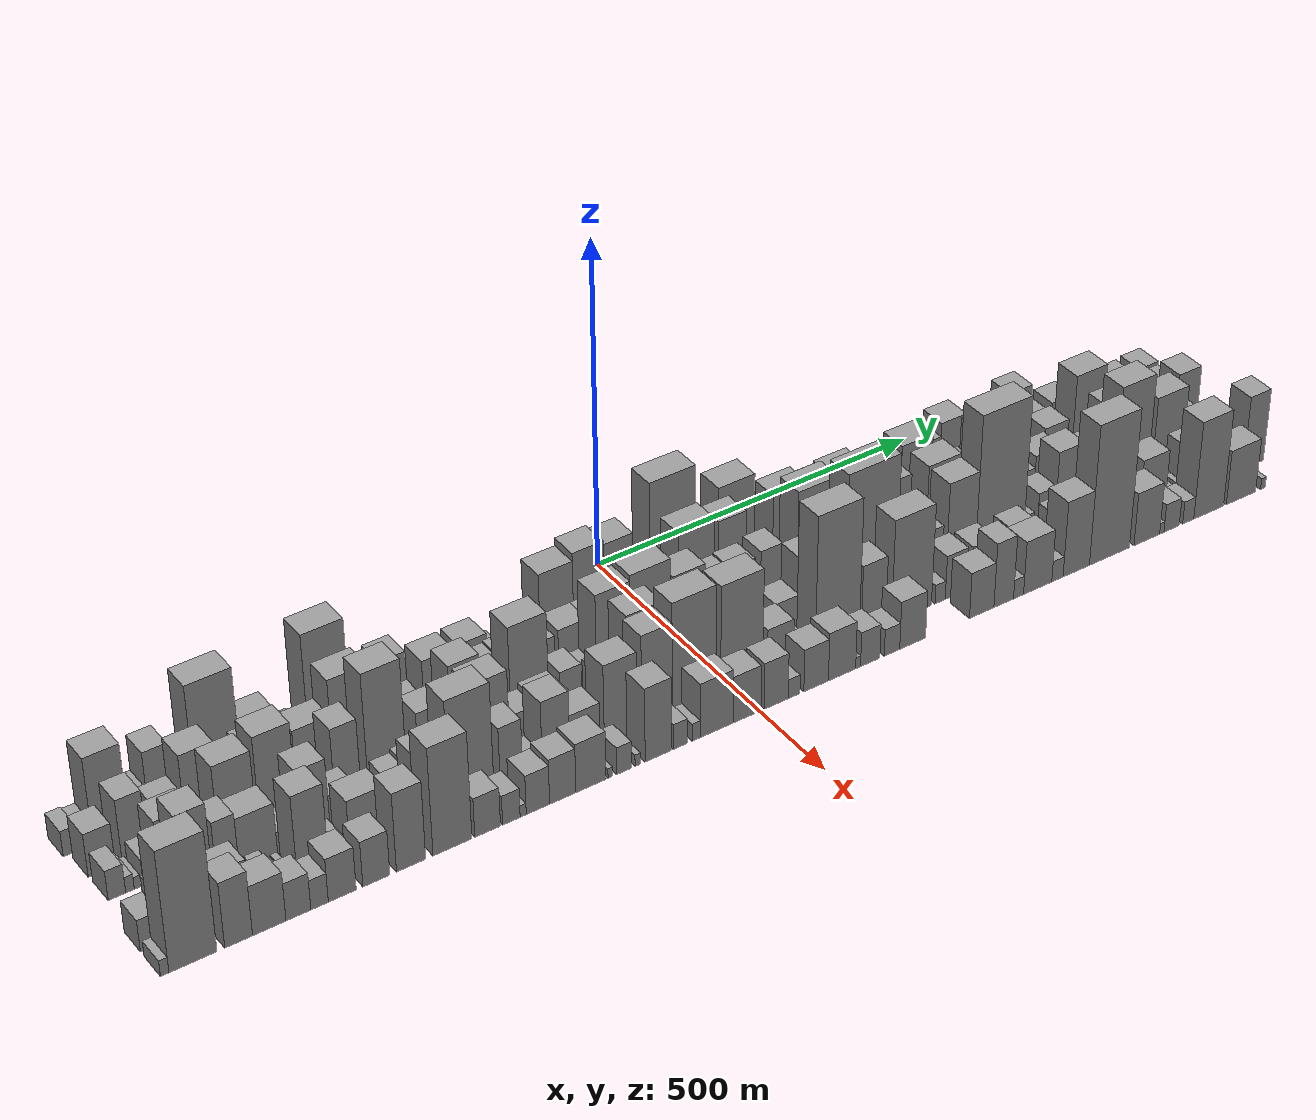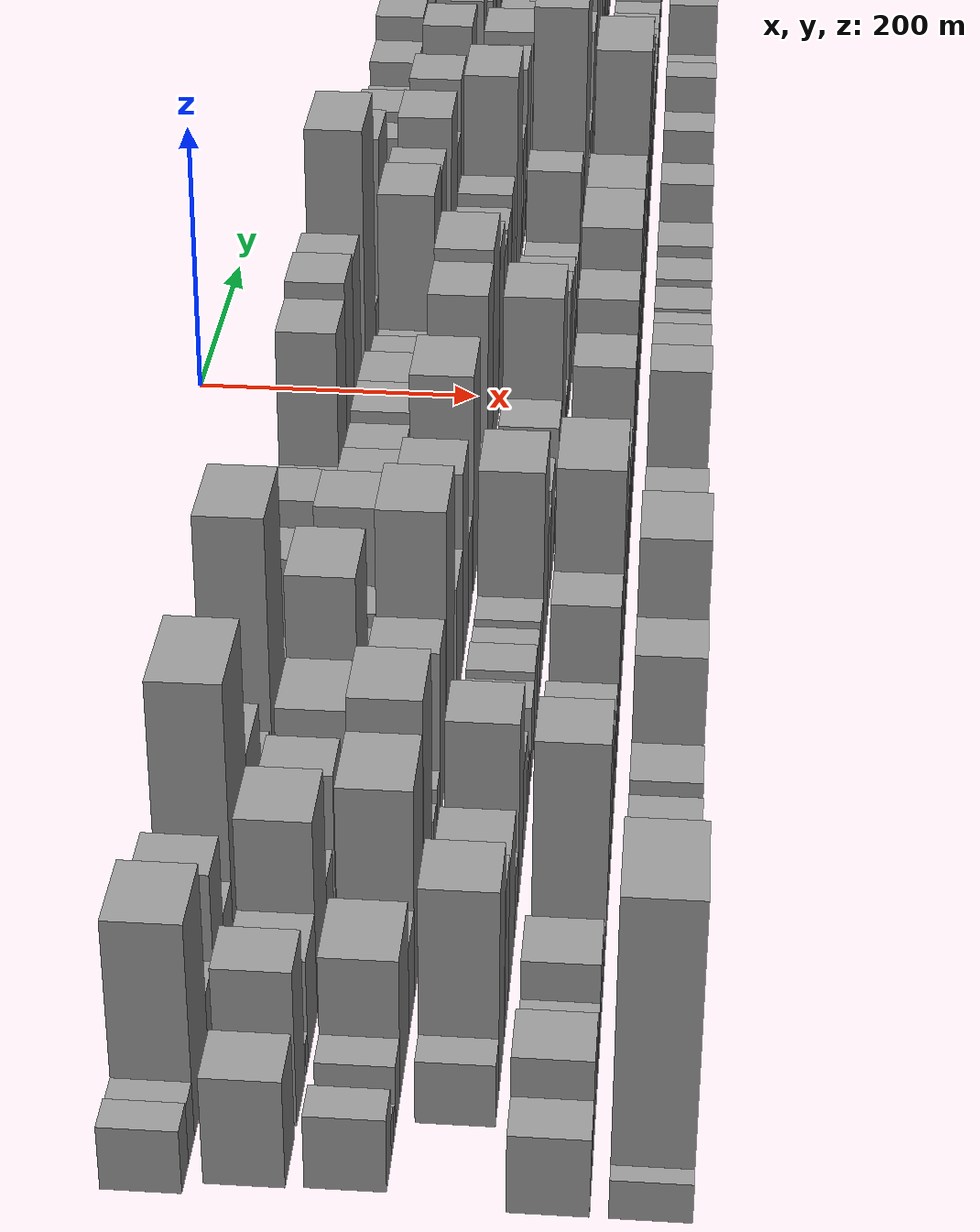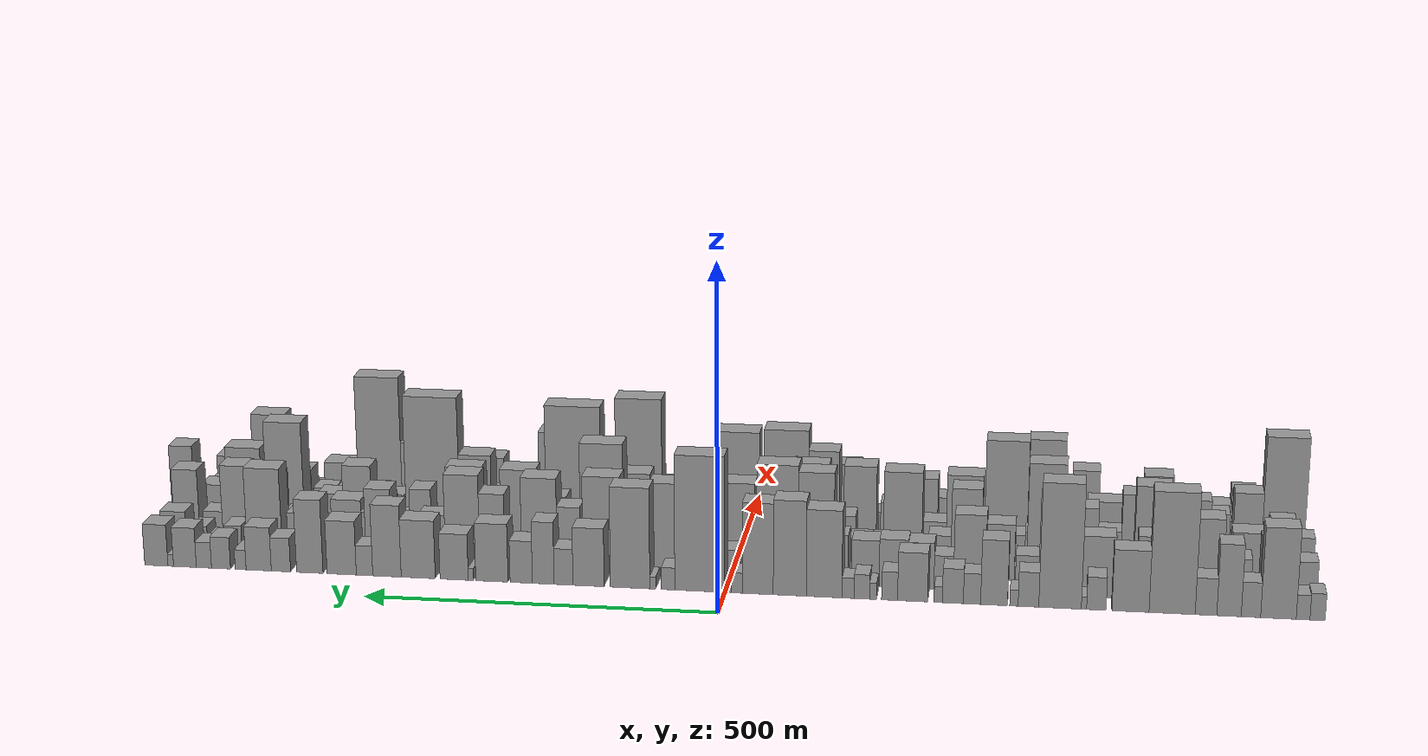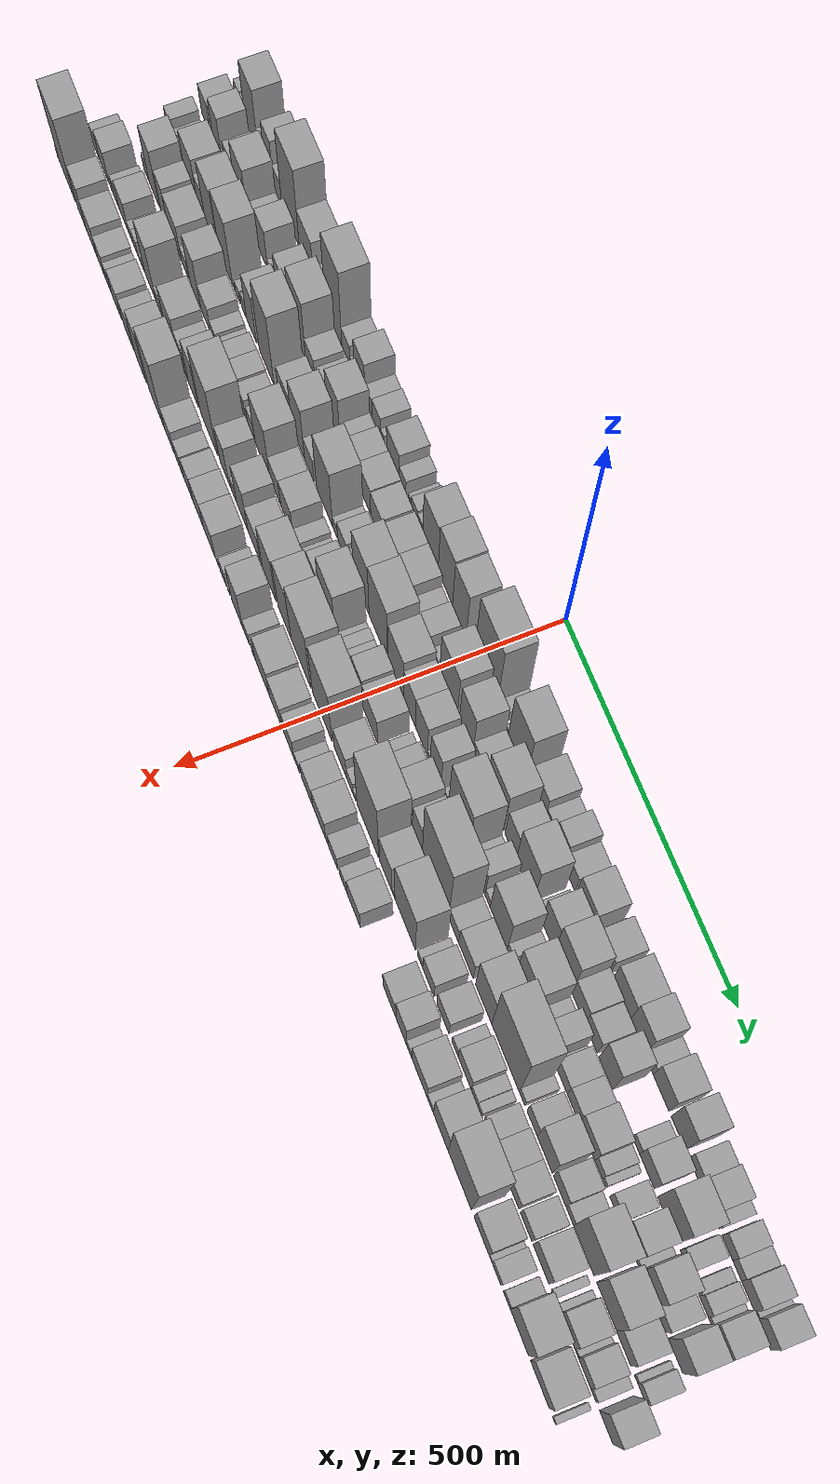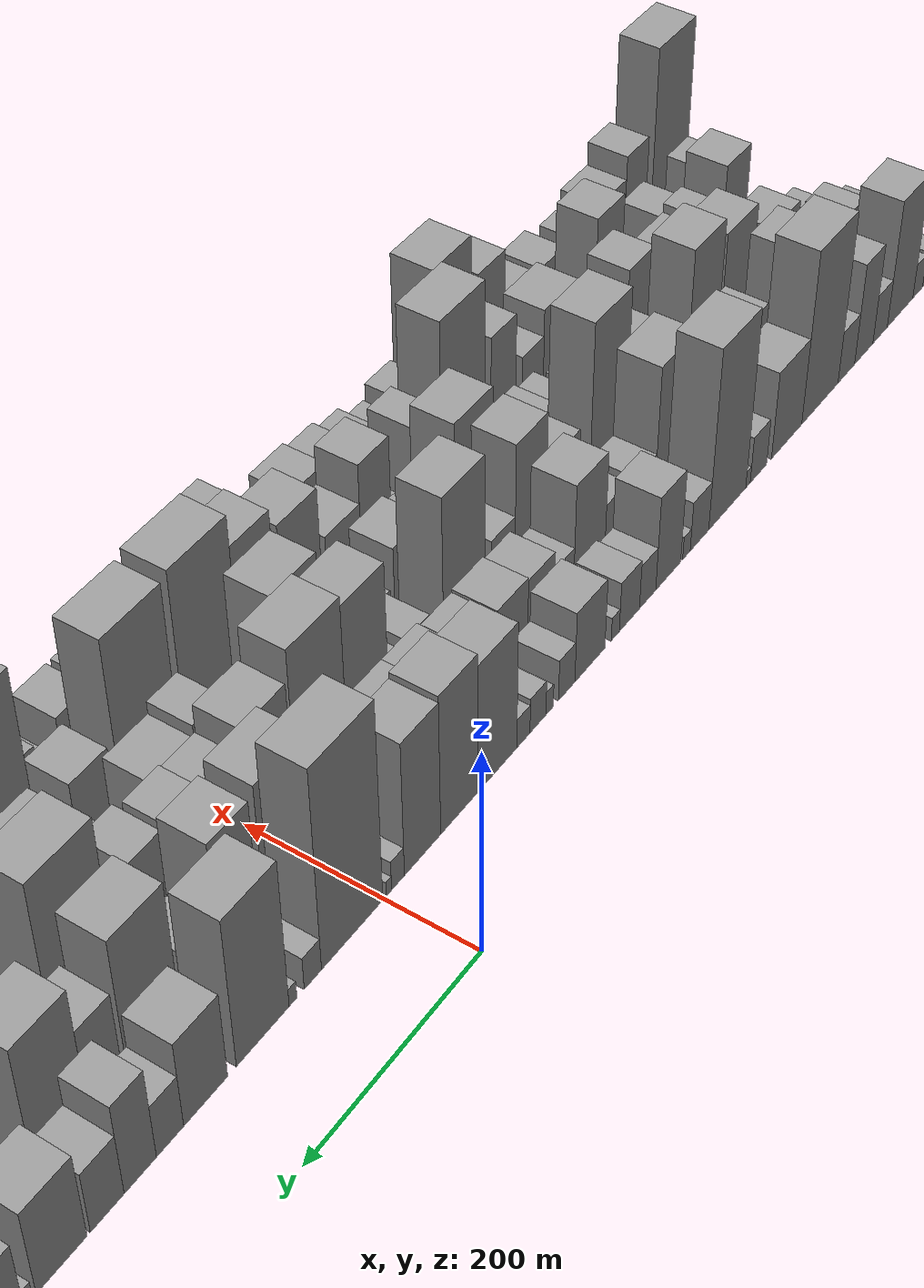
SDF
<sdf version="1.6">
 <world name="default">
  <scene>
   <sky><clouds><speed>12</speed></clouds></sky>
   <ambient>0.4 0.4 0.4 1</ambient>
   <background>0.7 0.7 0.7 1</background>
   <shadows>1</shadows>
  </scene>
  <gravity>0 0 -9.8066</gravity>
  <magnetic_field>6e-06 2.3e-05 -4.2e-05</magnetic_field>
  <physics default="0" name="default_physics" type="ode">
   <ode>
    <solver>
     <type>quick</type>
     <iters>10</iters>
     <sor>1.0</sor>
     <use_dynamic_moi_rescaling>0</use_dynamic_moi_rescaling>
    </solver>
    <constraints>
     <cfm>0</cfm>
     <erp>0.2</erp>
     <contact_max_correcting_vel>100</contact_max_correcting_vel>
     <contact_surface_layer>0.001</contact_surface_layer>
    </constraints>
   </ode>
   <max_step_size>0.004</max_step_size>
   <real_time_factor>1</real_time_factor>
   <real_time_update_rate>250</real_time_update_rate>
  </physics>
  <light name="sun" type="directional">
   <pose>0 0 10 0 0 0</pose>
   <diffuse>0.8 0.8 0.8 1</diffuse>
   <specular>0.2 0.2 0.2 1</specular>
   <attenuation>
    <range>1000</range>
    <constant>0.9</constant>
    <linear>0.01</linear>
    <quadratic>0.001</quadratic>
   </attenuation>
   <direction>-0.5 0.1 -0.9</direction>
  </light>
  <model name="building_1">
   <static>1</static>
   <pose>100.0000 -819.7387 0 0.000000 0.000000 0.000000</pose>
   <link name="link">
    <pose>0 0 19.50 0 0 0</pose>
    <collision name="collision"><geometry><box><size>40.0000 20.5226 39.0000</size></box></geometry></collision>
    <visual name="visual">
     <cast_shadows>0</cast_shadows>
     <geometry><box><size>40.0000 20.5226 39.0000</size></box></geometry>
     <material>
      <script>
       <uri>model://grey_wall/materials/scripts</uri>
       <uri>model://grey_wall/materials/textures</uri>
       <name>vrc/grey_wall</name>
      </script>
     </material>
    </visual>
   </link>
  </model>
  <model name="building_2">
   <static>1</static>
   <pose>100.0000 -800.1939 0 0.000000 0.000000 0.000000</pose>
   <link name="link">
    <pose>0 0 18.00 0 0 0</pose>
    <collision name="collision"><geometry><box><size>40.0000 18.5668 36.0000</size></box></geometry></collision>
    <visual name="visual">
     <cast_shadows>0</cast_shadows>
     <geometry><box><size>40.0000 18.5668 36.0000</size></box></geometry>
     <material>
      <script>
       <uri>model://grey_wall/materials/scripts</uri>
       <uri>model://grey_wall/materials/textures</uri>
       <name>vrc/grey_wall</name>
      </script>
     </material>
    </visual>
   </link>
  </model>
  <model name="building_3">
   <static>1</static>
   <pose>100.0000 -766.8831 0 0.000000 0.000000 0.000000</pose>
   <link name="link">
    <pose>0 0 66.00 0 0 0</pose>
    <collision name="collision"><geometry><box><size>40.0000 48.0549 132.0000</size></box></geometry></collision>
    <visual name="visual">
     <cast_shadows>0</cast_shadows>
     <geometry><box><size>40.0000 48.0549 132.0000</size></box></geometry>
     <material>
      <script>
       <uri>model://grey_wall/materials/scripts</uri>
       <uri>model://grey_wall/materials/textures</uri>
       <name>vrc/grey_wall</name>
      </script>
     </material>
    </visual>
   </link>
  </model>
  <model name="building_4">
   <static>1</static>
   <pose>100.0000 -729.6831 0 0.000000 0.000000 0.000000</pose>
   <link name="link">
    <pose>0 0 25.50 0 0 0</pose>
    <collision name="collision"><geometry><box><size>40.0000 26.3450 51.0000</size></box></geometry></collision>
    <visual name="visual">
     <cast_shadows>0</cast_shadows>
     <geometry><box><size>40.0000 26.3450 51.0000</size></box></geometry>
     <material>
      <script>
       <uri>model://grey_wall/materials/scripts</uri>
       <uri>model://grey_wall/materials/textures</uri>
       <name>vrc/grey_wall</name>
      </script>
     </material>
    </visual>
   </link>
  </model>
  <model name="building_5">
   <static>1</static>
   <pose>100.0000 -699.9539 0 0.000000 0.000000 0.000000</pose>
   <link name="link">
    <pose>0 0 52.50 0 0 0</pose>
    <collision name="collision"><geometry><box><size>40.0000 33.1135 105.0000</size></box></geometry></collision>
    <visual name="visual">
     <cast_shadows>0</cast_shadows>
     <geometry><box><size>40.0000 33.1135 105.0000</size></box></geometry>
     <material>
      <script>
       <uri>model://grey_wall/materials/scripts</uri>
       <uri>model://grey_wall/materials/textures</uri>
       <name>vrc/grey_wall</name>
      </script>
     </material>
    </visual>
   </link>
  </model>
  <model name="building_6">
   <static>1</static>
   <pose>100.0000 -668.6978 0 0.000000 0.000000 0.000000</pose>
   <link name="link">
    <pose>0 0 27.00 0 0 0</pose>
    <collision name="collision"><geometry><box><size>40.0000 29.3988 54.0000</size></box></geometry></collision>
    <visual name="visual">
     <cast_shadows>0</cast_shadows>
     <geometry><box><size>40.0000 29.3988 54.0000</size></box></geometry>
     <material>
      <script>
       <uri>model://grey_wall/materials/scripts</uri>
       <uri>model://grey_wall/materials/textures</uri>
       <name>vrc/grey_wall</name>
      </script>
     </material>
    </visual>
   </link>
  </model>
  <model name="building_7">
   <static>1</static>
   <pose>100.0000 -622.5215 0 0.000000 0.000000 0.000000</pose>
   <link name="link">
    <pose>0 0 88.50 0 0 0</pose>
    <collision name="collision"><geometry><box><size>40.0000 62.9537 177.0000</size></box></geometry></collision>
    <visual name="visual">
     <cast_shadows>0</cast_shadows>
     <geometry><box><size>40.0000 62.9537 177.0000</size></box></geometry>
     <material>
      <script>
       <uri>model://grey_wall/materials/scripts</uri>
       <uri>model://grey_wall/materials/textures</uri>
       <name>vrc/grey_wall</name>
      </script>
     </material>
    </visual>
   </link>
  </model>
  <model name="building_8">
   <static>1</static>
   <pose>100.0000 -565.6612 0 0.000000 0.000000 0.000000</pose>
   <link name="link">
    <pose>0 0 45.00 0 0 0</pose>
    <collision name="collision"><geometry><box><size>40.0000 50.7670 90.0000</size></box></geometry></collision>
    <visual name="visual">
     <cast_shadows>0</cast_shadows>
     <geometry><box><size>40.0000 50.7670 90.0000</size></box></geometry>
     <material>
      <script>
       <uri>model://grey_wall/materials/scripts</uri>
       <uri>model://grey_wall/materials/textures</uri>
       <name>vrc/grey_wall</name>
      </script>
     </material>
    </visual>
   </link>
  </model>
  <model name="building_9">
   <static>1</static>
   <pose>100.0000 -518.8695 0 0.000000 0.000000 0.000000</pose>
   <link name="link">
    <pose>0 0 24.00 0 0 0</pose>
    <collision name="collision"><geometry><box><size>40.0000 26.8164 48.0000</size></box></geometry></collision>
    <visual name="visual">
     <cast_shadows>0</cast_shadows>
     <geometry><box><size>40.0000 26.8164 48.0000</size></box></geometry>
     <material>
      <script>
       <uri>model://grey_wall/materials/scripts</uri>
       <uri>model://grey_wall/materials/textures</uri>
       <name>vrc/grey_wall</name>
      </script>
     </material>
    </visual>
   </link>
  </model>
  <model name="building_10">
   <static>1</static>
   <pose>100.0000 -501.8255 0 0.000000 0.000000 0.000000</pose>
   <link name="link">
    <pose>0 0 9.00 0 0 0</pose>
    <collision name="collision"><geometry><box><size>40.0000 7.2716 18.0000</size></box></geometry></collision>
    <visual name="visual">
     <cast_shadows>0</cast_shadows>
     <geometry><box><size>40.0000 7.2716 18.0000</size></box></geometry>
     <material>
      <script>
       <uri>model://grey_wall/materials/scripts</uri>
       <uri>model://grey_wall/materials/textures</uri>
       <name>vrc/grey_wall</name>
      </script>
     </material>
    </visual>
   </link>
  </model>
  <model name="building_11">
   <static>1</static>
   <pose>100.0000 -468.8463 0 0.000000 0.000000 0.000000</pose>
   <link name="link">
    <pose>0 0 91.50 0 0 0</pose>
    <collision name="collision"><geometry><box><size>40.0000 58.6867 183.0000</size></box></geometry></collision>
    <visual name="visual">
     <cast_shadows>0</cast_shadows>
     <geometry><box><size>40.0000 58.6867 183.0000</size></box></geometry>
     <material>
      <script>
       <uri>model://grey_wall/materials/scripts</uri>
       <uri>model://grey_wall/materials/textures</uri>
       <name>vrc/grey_wall</name>
      </script>
     </material>
    </visual>
   </link>
  </model>
  <model name="building_12">
   <static>1</static>
   <pose>100.0000 -425.2195 0 0.000000 0.000000 0.000000</pose>
   <link name="link">
    <pose>0 0 25.50 0 0 0</pose>
    <collision name="collision"><geometry><box><size>40.0000 28.5671 51.0000</size></box></geometry></collision>
    <visual name="visual">
     <cast_shadows>0</cast_shadows>
     <geometry><box><size>40.0000 28.5671 51.0000</size></box></geometry>
     <material>
      <script>
       <uri>model://grey_wall/materials/scripts</uri>
       <uri>model://grey_wall/materials/textures</uri>
       <name>vrc/grey_wall</name>
      </script>
     </material>
    </visual>
   </link>
  </model>
  <model name="building_13">
   <static>1</static>
   <pose>100.0000 -405.1255 0 0.000000 0.000000 0.000000</pose>
   <link name="link">
    <pose>0 0 12.00 0 0 0</pose>
    <collision name="collision"><geometry><box><size>40.0000 11.6210 24.0000</size></box></geometry></collision>
    <visual name="visual">
     <cast_shadows>0</cast_shadows>
     <geometry><box><size>40.0000 11.6210 24.0000</size></box></geometry>
     <material>
      <script>
       <uri>model://grey_wall/materials/scripts</uri>
       <uri>model://grey_wall/materials/textures</uri>
       <name>vrc/grey_wall</name>
      </script>
     </material>
    </visual>
   </link>
  </model>
  <model name="building_14">
   <static>1</static>
   <pose>100.0000 -377.6499 0 0.000000 0.000000 0.000000</pose>
   <link name="link">
    <pose>0 0 48.00 0 0 0</pose>
    <collision name="collision"><geometry><box><size>40.0000 37.3301 96.0000</size></box></geometry></collision>
    <visual name="visual">
     <cast_shadows>0</cast_shadows>
     <geometry><box><size>40.0000 37.3301 96.0000</size></box></geometry>
     <material>
      <script>
       <uri>model://grey_wall/materials/scripts</uri>
       <uri>model://grey_wall/materials/textures</uri>
       <name>vrc/grey_wall</name>
      </script>
     </material>
    </visual>
   </link>
  </model>
  <model name="building_15">
   <static>1</static>
   <pose>100.0000 -346.9842 0 0.000000 0.000000 0.000000</pose>
   <link name="link">
    <pose>0 0 22.50 0 0 0</pose>
    <collision name="collision"><geometry><box><size>40.0000 24.0015 45.0000</size></box></geometry></collision>
    <visual name="visual">
     <cast_shadows>0</cast_shadows>
     <geometry><box><size>40.0000 24.0015 45.0000</size></box></geometry>
     <material>
      <script>
       <uri>model://grey_wall/materials/scripts</uri>
       <uri>model://grey_wall/materials/textures</uri>
       <name>vrc/grey_wall</name>
      </script>
     </material>
    </visual>
   </link>
  </model>
  <model name="building_16">
   <static>1</static>
   <pose>100.0000 -320.3725 0 0.000000 0.000000 0.000000</pose>
   <link name="link">
    <pose>0 0 25.50 0 0 0</pose>
    <collision name="collision"><geometry><box><size>40.0000 29.2219 51.0000</size></box></geometry></collision>
    <visual name="visual">
     <cast_shadows>0</cast_shadows>
     <geometry><box><size>40.0000 29.2219 51.0000</size></box></geometry>
     <material>
      <script>
       <uri>model://grey_wall/materials/scripts</uri>
       <uri>model://grey_wall/materials/textures</uri>
       <name>vrc/grey_wall</name>
      </script>
     </material>
    </visual>
   </link>
  </model>
  <model name="building_17">
   <static>1</static>
   <pose>100.0000 -300.0065 0 0.000000 0.000000 0.000000</pose>
   <link name="link">
    <pose>0 0 12.00 0 0 0</pose>
    <collision name="collision"><geometry><box><size>40.0000 11.5102 24.0000</size></box></geometry></collision>
    <visual name="visual">
     <cast_shadows>0</cast_shadows>
     <geometry><box><size>40.0000 11.5102 24.0000</size></box></geometry>
     <material>
      <script>
       <uri>model://grey_wall/materials/scripts</uri>
       <uri>model://grey_wall/materials/textures</uri>
       <name>vrc/grey_wall</name>
      </script>
     </material>
    </visual>
   </link>
  </model>
  <model name="building_18">
   <static>1</static>
   <pose>100.0000 -264.2388 0 0.000000 0.000000 0.000000</pose>
   <link name="link">
    <pose>0 0 36.00 0 0 0</pose>
    <collision name="collision"><geometry><box><size>40.0000 42.0253 72.0000</size></box></geometry></collision>
    <visual name="visual">
     <cast_shadows>0</cast_shadows>
     <geometry><box><size>40.0000 42.0253 72.0000</size></box></geometry>
     <material>
      <script>
       <uri>model://grey_wall/materials/scripts</uri>
       <uri>model://grey_wall/materials/textures</uri>
       <name>vrc/grey_wall</name>
      </script>
     </material>
    </visual>
   </link>
  </model>
  <model name="building_19">
   <static>1</static>
   <pose>100.0000 -231.9857 0 0.000000 0.000000 0.000000</pose>
   <link name="link">
    <pose>0 0 21.00 0 0 0</pose>
    <collision name="collision"><geometry><box><size>40.0000 22.4809 42.0000</size></box></geometry></collision>
    <visual name="visual">
     <cast_shadows>0</cast_shadows>
     <geometry><box><size>40.0000 22.4809 42.0000</size></box></geometry>
     <material>
      <script>
       <uri>model://grey_wall/materials/scripts</uri>
       <uri>model://grey_wall/materials/textures</uri>
       <name>vrc/grey_wall</name>
      </script>
     </material>
    </visual>
   </link>
  </model>
  <model name="building_20">
   <static>1</static>
   <pose>100.0000 -208.7718 0 0.000000 0.000000 0.000000</pose>
   <link name="link">
    <pose>0 0 12.00 0 0 0</pose>
    <collision name="collision"><geometry><box><size>40.0000 9.9469 24.0000</size></box></geometry></collision>
    <visual name="visual">
     <cast_shadows>0</cast_shadows>
     <geometry><box><size>40.0000 9.9469 24.0000</size></box></geometry>
     <material>
      <script>
       <uri>model://grey_wall/materials/scripts</uri>
       <uri>model://grey_wall/materials/textures</uri>
       <name>vrc/grey_wall</name>
      </script>
     </material>
    </visual>
   </link>
  </model>
  <model name="building_21">
   <static>1</static>
   <pose>100.0000 -193.0717 0 0.000000 0.000000 0.000000</pose>
   <link name="link">
    <pose>0 0 18.00 0 0 0</pose>
    <collision name="collision"><geometry><box><size>40.0000 21.4533 36.0000</size></box></geometry></collision>
    <visual name="visual">
     <cast_shadows>0</cast_shadows>
     <geometry><box><size>40.0000 21.4533 36.0000</size></box></geometry>
     <material>
      <script>
       <uri>model://grey_wall/materials/scripts</uri>
       <uri>model://grey_wall/materials/textures</uri>
       <name>vrc/grey_wall</name>
      </script>
     </material>
    </visual>
   </link>
  </model>
  <model name="building_22">
   <static>1</static>
   <pose>100.0000 -173.7144 0 0.000000 0.000000 0.000000</pose>
   <link name="link">
    <pose>0 0 15.00 0 0 0</pose>
    <collision name="collision"><geometry><box><size>40.0000 17.2611 30.0000</size></box></geometry></collision>
    <visual name="visual">
     <cast_shadows>0</cast_shadows>
     <geometry><box><size>40.0000 17.2611 30.0000</size></box></geometry>
     <material>
      <script>
       <uri>model://grey_wall/materials/scripts</uri>
       <uri>model://grey_wall/materials/textures</uri>
       <name>vrc/grey_wall</name>
      </script>
     </material>
    </visual>
   </link>
  </model>
  <model name="building_23">
   <static>1</static>
   <pose>100.0000 -139.9668 0 0.000000 0.000000 0.000000</pose>
   <link name="link">
    <pose>0 0 64.50 0 0 0</pose>
    <collision name="collision"><geometry><box><size>40.0000 50.2341 129.0000</size></box></geometry></collision>
    <visual name="visual">
     <cast_shadows>0</cast_shadows>
     <geometry><box><size>40.0000 50.2341 129.0000</size></box></geometry>
     <material>
      <script>
       <uri>model://grey_wall/materials/scripts</uri>
       <uri>model://grey_wall/materials/textures</uri>
       <name>vrc/grey_wall</name>
      </script>
     </material>
    </visual>
   </link>
  </model>
  <model name="building_24">
   <static>1</static>
   <pose>100.0000 -91.5264 0 0.000000 0.000000 0.000000</pose>
   <link name="link">
    <pose>0 0 70.50 0 0 0</pose>
    <collision name="collision"><geometry><box><size>40.0000 46.6467 141.0000</size></box></geometry></collision>
    <visual name="visual">
     <cast_shadows>0</cast_shadows>
     <geometry><box><size>40.0000 46.6467 141.0000</size></box></geometry>
     <material>
      <script>
       <uri>model://grey_wall/materials/scripts</uri>
       <uri>model://grey_wall/materials/textures</uri>
       <name>vrc/grey_wall</name>
      </script>
     </material>
    </visual>
   </link>
  </model>
  <model name="building_25">
   <static>1</static>
   <pose>100.0000 -46.1873 0 0.000000 0.000000 0.000000</pose>
   <link name="link">
    <pose>0 0 67.50 0 0 0</pose>
    <collision name="collision"><geometry><box><size>40.0000 44.0315 135.0000</size></box></geometry></collision>
    <visual name="visual">
     <cast_shadows>0</cast_shadows>
     <geometry><box><size>40.0000 44.0315 135.0000</size></box></geometry>
     <material>
      <script>
       <uri>model://grey_wall/materials/scripts</uri>
       <uri>model://grey_wall/materials/textures</uri>
       <name>vrc/grey_wall</name>
      </script>
     </material>
    </visual>
   </link>
  </model>
  <model name="building_26">
   <static>1</static>
   <pose>100.0000 -16.5393 0 0.000000 0.000000 0.000000</pose>
   <link name="link">
    <pose>0 0 15.00 0 0 0</pose>
    <collision name="collision"><geometry><box><size>40.0000 15.2647 30.0000</size></box></geometry></collision>
    <visual name="visual">
     <cast_shadows>0</cast_shadows>
     <geometry><box><size>40.0000 15.2647 30.0000</size></box></geometry>
     <material>
      <script>
       <uri>model://grey_wall/materials/scripts</uri>
       <uri>model://grey_wall/materials/textures</uri>
       <name>vrc/grey_wall</name>
      </script>
     </material>
    </visual>
   </link>
  </model>
  <model name="building_27">
   <static>1</static>
   <pose>100.0000 -5.7224 0 0.000000 0.000000 0.000000</pose>
   <link name="link">
    <pose>0 0 7.50 0 0 0</pose>
    <collision name="collision"><geometry><box><size>40.0000 6.3690 15.0000</size></box></geometry></collision>
    <visual name="visual">
     <cast_shadows>0</cast_shadows>
     <geometry><box><size>40.0000 6.3690 15.0000</size></box></geometry>
     <material>
      <script>
       <uri>model://grey_wall/materials/scripts</uri>
       <uri>model://grey_wall/materials/textures</uri>
       <name>vrc/grey_wall</name>
      </script>
     </material>
    </visual>
   </link>
  </model>
  <model name="building_28">
   <static>1</static>
   <pose>100.0000 36.5928 0 0.000000 0.000000 0.000000</pose>
   <link name="link">
    <pose>0 0 100.50 0 0 0</pose>
    <collision name="collision"><geometry><box><size>40.0000 70.2614 201.0000</size></box></geometry></collision>
    <visual name="visual">
     <cast_shadows>0</cast_shadows>
     <geometry><box><size>40.0000 70.2614 201.0000</size></box></geometry>
     <material>
      <script>
       <uri>model://grey_wall/materials/scripts</uri>
       <uri>model://grey_wall/materials/textures</uri>
       <name>vrc/grey_wall</name>
      </script>
     </material>
    </visual>
   </link>
  </model>
  <model name="building_29">
   <static>1</static>
   <pose>100.0000 81.3332 0 0.000000 0.000000 0.000000</pose>
   <link name="link">
    <pose>0 0 16.50 0 0 0</pose>
    <collision name="collision"><geometry><box><size>40.0000 19.2194 33.0000</size></box></geometry></collision>
    <visual name="visual">
     <cast_shadows>0</cast_shadows>
     <geometry><box><size>40.0000 19.2194 33.0000</size></box></geometry>
     <material>
      <script>
       <uri>model://grey_wall/materials/scripts</uri>
       <uri>model://grey_wall/materials/textures</uri>
       <name>vrc/grey_wall</name>
      </script>
     </material>
    </visual>
   </link>
  </model>
  <model name="building_30">
   <static>1</static>
   <pose>100.0000 103.2187 0 0.000000 0.000000 0.000000</pose>
   <link name="link">
    <pose>0 0 9.00 0 0 0</pose>
    <collision name="collision"><geometry><box><size>40.0000 8.5515 18.0000</size></box></geometry></collision>
    <visual name="visual">
     <cast_shadows>0</cast_shadows>
     <geometry><box><size>40.0000 8.5515 18.0000</size></box></geometry>
     <material>
      <script>
       <uri>model://grey_wall/materials/scripts</uri>
       <uri>model://grey_wall/materials/textures</uri>
       <name>vrc/grey_wall</name>
      </script>
     </material>
    </visual>
   </link>
  </model>
  <model name="building_31">
   <static>1</static>
   <pose>100.0000 135.7217 0 0.000000 0.000000 0.000000</pose>
   <link name="link">
    <pose>0 0 75.00 0 0 0</pose>
    <collision name="collision"><geometry><box><size>40.0000 56.4544 150.0000</size></box></geometry></collision>
    <visual name="visual">
     <cast_shadows>0</cast_shadows>
     <geometry><box><size>40.0000 56.4544 150.0000</size></box></geometry>
     <material>
      <script>
       <uri>model://grey_wall/materials/scripts</uri>
       <uri>model://grey_wall/materials/textures</uri>
       <name>vrc/grey_wall</name>
      </script>
     </material>
    </visual>
   </link>
  </model>
  <model name="building_32">
   <static>1</static>
   <pose>100.0000 195.4311 0 0.000000 0.000000 0.000000</pose>
   <link name="link">
    <pose>0 0 43.50 0 0 0</pose>
    <collision name="collision"><geometry><box><size>40.0000 44.9646 87.0000</size></box></geometry></collision>
    <visual name="visual">
     <cast_shadows>0</cast_shadows>
     <geometry><box><size>40.0000 44.9646 87.0000</size></box></geometry>
     <material>
      <script>
       <uri>model://grey_wall/materials/scripts</uri>
       <uri>model://grey_wall/materials/textures</uri>
       <name>vrc/grey_wall</name>
      </script>
     </material>
    </visual>
   </link>
  </model>
  <model name="building_33">
   <static>1</static>
   <pose>100.0000 231.5103 0 0.000000 0.000000 0.000000</pose>
   <link name="link">
    <pose>0 0 27.00 0 0 0</pose>
    <collision name="collision"><geometry><box><size>40.0000 27.1937 54.0000</size></box></geometry></collision>
    <visual name="visual">
     <cast_shadows>0</cast_shadows>
     <geometry><box><size>40.0000 27.1937 54.0000</size></box></geometry>
     <material>
      <script>
       <uri>model://grey_wall/materials/scripts</uri>
       <uri>model://grey_wall/materials/textures</uri>
       <name>vrc/grey_wall</name>
      </script>
     </material>
    </visual>
   </link>
  </model>
  <model name="building_34">
   <static>1</static>
   <pose>100.0000 260.8159 0 0.000000 0.000000 0.000000</pose>
   <link name="link">
    <pose>0 0 46.50 0 0 0</pose>
    <collision name="collision"><geometry><box><size>40.0000 31.4175 93.0000</size></box></geometry></collision>
    <visual name="visual">
     <cast_shadows>0</cast_shadows>
     <geometry><box><size>40.0000 31.4175 93.0000</size></box></geometry>
     <material>
      <script>
       <uri>model://grey_wall/materials/scripts</uri>
       <uri>model://grey_wall/materials/textures</uri>
       <name>vrc/grey_wall</name>
      </script>
     </material>
    </visual>
   </link>
  </model>
  <model name="building_35">
   <static>1</static>
   <pose>100.0000 292.6859 0 0.000000 0.000000 0.000000</pose>
   <link name="link">
    <pose>0 0 31.50 0 0 0</pose>
    <collision name="collision"><geometry><box><size>40.0000 32.3226 63.0000</size></box></geometry></collision>
    <visual name="visual">
     <cast_shadows>0</cast_shadows>
     <geometry><box><size>40.0000 32.3226 63.0000</size></box></geometry>
     <material>
      <script>
       <uri>model://grey_wall/materials/scripts</uri>
       <uri>model://grey_wall/materials/textures</uri>
       <name>vrc/grey_wall</name>
      </script>
     </material>
    </visual>
   </link>
  </model>
  <model name="building_36">
   <static>1</static>
   <pose>100.0000 335.2974 0 0.000000 0.000000 0.000000</pose>
   <link name="link">
    <pose>0 0 43.50 0 0 0</pose>
    <collision name="collision"><geometry><box><size>40.0000 46.9004 87.0000</size></box></geometry></collision>
    <visual name="visual">
     <cast_shadows>0</cast_shadows>
     <geometry><box><size>40.0000 46.9004 87.0000</size></box></geometry>
     <material>
      <script>
       <uri>model://grey_wall/materials/scripts</uri>
       <uri>model://grey_wall/materials/textures</uri>
       <name>vrc/grey_wall</name>
      </script>
     </material>
    </visual>
   </link>
  </model>
  <model name="building_37">
   <static>1</static>
   <pose>100.0000 365.7102 0 0.000000 0.000000 0.000000</pose>
   <link name="link">
    <pose>0 0 9.00 0 0 0</pose>
    <collision name="collision"><geometry><box><size>40.0000 7.9251 18.0000</size></box></geometry></collision>
    <visual name="visual">
     <cast_shadows>0</cast_shadows>
     <geometry><box><size>40.0000 7.9251 18.0000</size></box></geometry>
     <material>
      <script>
       <uri>model://grey_wall/materials/scripts</uri>
       <uri>model://grey_wall/materials/textures</uri>
       <name>vrc/grey_wall</name>
      </script>
     </material>
    </visual>
   </link>
  </model>
  <model name="building_38">
   <static>1</static>
   <pose>100.0000 390.2673 0 0.000000 0.000000 0.000000</pose>
   <link name="link">
    <pose>0 0 34.50 0 0 0</pose>
    <collision name="collision"><geometry><box><size>40.0000 41.1891 69.0000</size></box></geometry></collision>
    <visual name="visual">
     <cast_shadows>0</cast_shadows>
     <geometry><box><size>40.0000 41.1891 69.0000</size></box></geometry>
     <material>
      <script>
       <uri>model://grey_wall/materials/scripts</uri>
       <uri>model://grey_wall/materials/textures</uri>
       <name>vrc/grey_wall</name>
      </script>
     </material>
    </visual>
   </link>
  </model>
  <model name="building_39">
   <static>1</static>
   <pose>100.0000 442.7852 0 0.000000 0.000000 0.000000</pose>
   <link name="link">
    <pose>0 0 43.50 0 0 0</pose>
    <collision name="collision"><geometry><box><size>40.0000 49.8468 87.0000</size></box></geometry></collision>
    <visual name="visual">
     <cast_shadows>0</cast_shadows>
     <geometry><box><size>40.0000 49.8468 87.0000</size></box></geometry>
     <material>
      <script>
       <uri>model://grey_wall/materials/scripts</uri>
       <uri>model://grey_wall/materials/textures</uri>
       <name>vrc/grey_wall</name>
      </script>
     </material>
    </visual>
   </link>
  </model>
  <model name="building_40">
   <static>1</static>
   <pose>100.0000 488.5951 0 0.000000 0.000000 0.000000</pose>
   <link name="link">
    <pose>0 0 54.00 0 0 0</pose>
    <collision name="collision"><geometry><box><size>40.0000 41.7729 108.0000</size></box></geometry></collision>
    <visual name="visual">
     <cast_shadows>0</cast_shadows>
     <geometry><box><size>40.0000 41.7729 108.0000</size></box></geometry>
     <material>
      <script>
       <uri>model://grey_wall/materials/scripts</uri>
       <uri>model://grey_wall/materials/textures</uri>
       <name>vrc/grey_wall</name>
      </script>
     </material>
    </visual>
   </link>
  </model>
  <model name="building_41">
   <static>1</static>
   <pose>100.0000 521.5661 0 0.000000 0.000000 0.000000</pose>
   <link name="link">
    <pose>0 0 22.50 0 0 0</pose>
    <collision name="collision"><geometry><box><size>40.0000 24.1690 45.0000</size></box></geometry></collision>
    <visual name="visual">
     <cast_shadows>0</cast_shadows>
     <geometry><box><size>40.0000 24.1690 45.0000</size></box></geometry>
     <material>
      <script>
       <uri>model://grey_wall/materials/scripts</uri>
       <uri>model://grey_wall/materials/textures</uri>
       <name>vrc/grey_wall</name>
      </script>
     </material>
    </visual>
   </link>
  </model>
  <model name="building_42">
   <static>1</static>
   <pose>100.0000 555.1647 0 0.000000 0.000000 0.000000</pose>
   <link name="link">
    <pose>0 0 40.50 0 0 0</pose>
    <collision name="collision"><geometry><box><size>40.0000 43.0284 81.0000</size></box></geometry></collision>
    <visual name="visual">
     <cast_shadows>0</cast_shadows>
     <geometry><box><size>40.0000 43.0284 81.0000</size></box></geometry>
     <material>
      <script>
       <uri>model://grey_wall/materials/scripts</uri>
       <uri>model://grey_wall/materials/textures</uri>
       <name>vrc/grey_wall</name>
      </script>
     </material>
    </visual>
   </link>
  </model>
  <model name="building_43">
   <static>1</static>
   <pose>100.0000 602.2209 0 0.000000 0.000000 0.000000</pose>
   <link name="link">
    <pose>0 0 55.50 0 0 0</pose>
    <collision name="collision"><geometry><box><size>40.0000 39.0840 111.0000</size></box></geometry></collision>
    <visual name="visual">
     <cast_shadows>0</cast_shadows>
     <geometry><box><size>40.0000 39.0840 111.0000</size></box></geometry>
     <material>
      <script>
       <uri>model://grey_wall/materials/scripts</uri>
       <uri>model://grey_wall/materials/textures</uri>
       <name>vrc/grey_wall</name>
      </script>
     </material>
    </visual>
   </link>
  </model>
  <model name="building_44">
   <static>1</static>
   <pose>100.0000 645.0443 0 0.000000 0.000000 0.000000</pose>
   <link name="link">
    <pose>0 0 25.50 0 0 0</pose>
    <collision name="collision"><geometry><box><size>40.0000 28.5628 51.0000</size></box></geometry></collision>
    <visual name="visual">
     <cast_shadows>0</cast_shadows>
     <geometry><box><size>40.0000 28.5628 51.0000</size></box></geometry>
     <material>
      <script>
       <uri>model://grey_wall/materials/scripts</uri>
       <uri>model://grey_wall/materials/textures</uri>
       <name>vrc/grey_wall</name>
      </script>
     </material>
    </visual>
   </link>
  </model>
  <model name="building_45">
   <static>1</static>
   <pose>100.0000 678.0807 0 0.000000 0.000000 0.000000</pose>
   <link name="link">
    <pose>0 0 33.00 0 0 0</pose>
    <collision name="collision"><geometry><box><size>40.0000 37.5100 66.0000</size></box></geometry></collision>
    <visual name="visual">
     <cast_shadows>0</cast_shadows>
     <geometry><box><size>40.0000 37.5100 66.0000</size></box></geometry>
     <material>
      <script>
       <uri>model://grey_wall/materials/scripts</uri>
       <uri>model://grey_wall/materials/textures</uri>
       <name>vrc/grey_wall</name>
      </script>
     </material>
    </visual>
   </link>
  </model>
  <model name="building_46">
   <static>1</static>
   <pose>100.0000 704.9046 0 0.000000 0.000000 0.000000</pose>
   <link name="link">
    <pose>0 0 15.00 0 0 0</pose>
    <collision name="collision"><geometry><box><size>40.0000 16.1377 30.0000</size></box></geometry></collision>
    <visual name="visual">
     <cast_shadows>0</cast_shadows>
     <geometry><box><size>40.0000 16.1377 30.0000</size></box></geometry>
     <material>
      <script>
       <uri>model://grey_wall/materials/scripts</uri>
       <uri>model://grey_wall/materials/textures</uri>
       <name>vrc/grey_wall</name>
      </script>
     </material>
    </visual>
   </link>
  </model>
  <model name="building_47">
   <static>1</static>
   <pose>100.0000 734.1687 0 0.000000 0.000000 0.000000</pose>
   <link name="link">
    <pose>0 0 24.00 0 0 0</pose>
    <collision name="collision"><geometry><box><size>40.0000 28.3905 48.0000</size></box></geometry></collision>
    <visual name="visual">
     <cast_shadows>0</cast_shadows>
     <geometry><box><size>40.0000 28.3905 48.0000</size></box></geometry>
     <material>
      <script>
       <uri>model://grey_wall/materials/scripts</uri>
       <uri>model://grey_wall/materials/textures</uri>
       <name>vrc/grey_wall</name>
      </script>
     </material>
    </visual>
   </link>
  </model>
  <model name="building_48">
   <static>1</static>
   <pose>100.0000 759.6690 0 0.000000 0.000000 0.000000</pose>
   <link name="link">
    <pose>0 0 19.50 0 0 0</pose>
    <collision name="collision"><geometry><box><size>40.0000 22.6100 39.0000</size></box></geometry></collision>
    <visual name="visual">
     <cast_shadows>0</cast_shadows>
     <geometry><box><size>40.0000 22.6100 39.0000</size></box></geometry>
     <material>
      <script>
       <uri>model://grey_wall/materials/scripts</uri>
       <uri>model://grey_wall/materials/textures</uri>
       <name>vrc/grey_wall</name>
      </script>
     </material>
    </visual>
   </link>
  </model>
  <model name="building_49">
   <static>1</static>
   <pose>100.0000 788.0264 0 0.000000 0.000000 0.000000</pose>
   <link name="link">
    <pose>0 0 30.00 0 0 0</pose>
    <collision name="collision"><geometry><box><size>40.0000 34.1048 60.0000</size></box></geometry></collision>
    <visual name="visual">
     <cast_shadows>0</cast_shadows>
     <geometry><box><size>40.0000 34.1048 60.0000</size></box></geometry>
     <material>
      <script>
       <uri>model://grey_wall/materials/scripts</uri>
       <uri>model://grey_wall/materials/textures</uri>
       <name>vrc/grey_wall</name>
      </script>
     </material>
    </visual>
   </link>
  </model>
  <model name="building_50">
   <static>1</static>
   <pose>100.0000 809.2436 0 0.000000 0.000000 0.000000</pose>
   <link name="link">
    <pose>0 0 9.00 0 0 0</pose>
    <collision name="collision"><geometry><box><size>40.0000 8.3298 18.0000</size></box></geometry></collision>
    <visual name="visual">
     <cast_shadows>0</cast_shadows>
     <geometry><box><size>40.0000 8.3298 18.0000</size></box></geometry>
     <material>
      <script>
       <uri>model://grey_wall/materials/scripts</uri>
       <uri>model://grey_wall/materials/textures</uri>
       <name>vrc/grey_wall</name>
      </script>
     </material>
    </visual>
   </link>
  </model>
  <model name="building_51">
   <static>1</static>
   <pose>100.0000 830.7961 0 0.000000 0.000000 0.000000</pose>
   <link name="link">
    <pose>0 0 31.50 0 0 0</pose>
    <collision name="collision"><geometry><box><size>40.0000 34.7751 63.0000</size></box></geometry></collision>
    <visual name="visual">
     <cast_shadows>0</cast_shadows>
     <geometry><box><size>40.0000 34.7751 63.0000</size></box></geometry>
     <material>
      <script>
       <uri>model://grey_wall/materials/scripts</uri>
       <uri>model://grey_wall/materials/textures</uri>
       <name>vrc/grey_wall</name>
      </script>
     </material>
    </visual>
   </link>
  </model>
  <model name="building_52">
   <static>1</static>
   <pose>149.0000 -804.3664 0 0.000000 0.000000 0.000000</pose>
   <link name="link">
    <pose>0 0 33.00 0 0 0</pose>
    <collision name="collision"><geometry><box><size>40.0000 35.2672 66.0000</size></box></geometry></collision>
    <visual name="visual">
     <cast_shadows>0</cast_shadows>
     <geometry><box><size>40.0000 35.2672 66.0000</size></box></geometry>
     <material>
      <script>
       <uri>model://grey_wall/materials/scripts</uri>
       <uri>model://grey_wall/materials/textures</uri>
       <name>vrc/grey_wall</name>
      </script>
     </material>
    </visual>
   </link>
  </model>
  <model name="building_53">
   <static>1</static>
   <pose>149.0000 -760.9721 0 0.000000 0.000000 0.000000</pose>
   <link name="link">
    <pose>0 0 48.00 0 0 0</pose>
    <collision name="collision"><geometry><box><size>40.0000 33.5213 96.0000</size></box></geometry></collision>
    <visual name="visual">
     <cast_shadows>0</cast_shadows>
     <geometry><box><size>40.0000 33.5213 96.0000</size></box></geometry>
     <material>
      <script>
       <uri>model://grey_wall/materials/scripts</uri>
       <uri>model://grey_wall/materials/textures</uri>
       <name>vrc/grey_wall</name>
      </script>
     </material>
    </visual>
   </link>
  </model>
  <model name="building_54">
   <static>1</static>
   <pose>149.0000 -735.8076 0 0.000000 0.000000 0.000000</pose>
   <link name="link">
    <pose>0 0 10.50 0 0 0</pose>
    <collision name="collision"><geometry><box><size>40.0000 8.8076 21.0000</size></box></geometry></collision>
    <visual name="visual">
     <cast_shadows>0</cast_shadows>
     <geometry><box><size>40.0000 8.8076 21.0000</size></box></geometry>
     <material>
      <script>
       <uri>model://grey_wall/materials/scripts</uri>
       <uri>model://grey_wall/materials/textures</uri>
       <name>vrc/grey_wall</name>
      </script>
     </material>
    </visual>
   </link>
  </model>
  <model name="building_55">
   <static>1</static>
   <pose>149.0000 -712.1371 0 0.000000 0.000000 0.000000</pose>
   <link name="link">
    <pose>0 0 33.00 0 0 0</pose>
    <collision name="collision"><geometry><box><size>40.0000 38.5335 66.0000</size></box></geometry></collision>
    <visual name="visual">
     <cast_shadows>0</cast_shadows>
     <geometry><box><size>40.0000 38.5335 66.0000</size></box></geometry>
     <material>
      <script>
       <uri>model://grey_wall/materials/scripts</uri>
       <uri>model://grey_wall/materials/textures</uri>
       <name>vrc/grey_wall</name>
      </script>
     </material>
    </visual>
   </link>
  </model>
  <model name="building_56">
   <static>1</static>
   <pose>149.0000 -669.6085 0 0.000000 0.000000 0.000000</pose>
   <link name="link">
    <pose>0 0 61.50 0 0 0</pose>
    <collision name="collision"><geometry><box><size>40.0000 46.5236 123.0000</size></box></geometry></collision>
    <visual name="visual">
     <cast_shadows>0</cast_shadows>
     <geometry><box><size>40.0000 46.5236 123.0000</size></box></geometry>
     <material>
      <script>
       <uri>model://grey_wall/materials/scripts</uri>
       <uri>model://grey_wall/materials/textures</uri>
       <name>vrc/grey_wall</name>
      </script>
     </material>
    </visual>
   </link>
  </model>
  <model name="building_57">
   <static>1</static>
   <pose>149.0000 -632.0075 0 0.000000 0.000000 0.000000</pose>
   <link name="link">
    <pose>0 0 25.50 0 0 0</pose>
    <collision name="collision"><geometry><box><size>40.0000 28.6784 51.0000</size></box></geometry></collision>
    <visual name="visual">
     <cast_shadows>0</cast_shadows>
     <geometry><box><size>40.0000 28.6784 51.0000</size></box></geometry>
     <material>
      <script>
       <uri>model://grey_wall/materials/scripts</uri>
       <uri>model://grey_wall/materials/textures</uri>
       <name>vrc/grey_wall</name>
      </script>
     </material>
    </visual>
   </link>
  </model>
  <model name="building_58">
   <static>1</static>
   <pose>149.0000 -591.9641 0 0.000000 0.000000 0.000000</pose>
   <link name="link">
    <pose>0 0 46.50 0 0 0</pose>
    <collision name="collision"><geometry><box><size>40.0000 35.4084 93.0000</size></box></geometry></collision>
    <visual name="visual">
     <cast_shadows>0</cast_shadows>
     <geometry><box><size>40.0000 35.4084 93.0000</size></box></geometry>
     <material>
      <script>
       <uri>model://grey_wall/materials/scripts</uri>
       <uri>model://grey_wall/materials/textures</uri>
       <name>vrc/grey_wall</name>
      </script>
     </material>
    </visual>
   </link>
  </model>
  <model name="building_59">
   <static>1</static>
   <pose>149.0000 -568.5882 0 0.000000 0.000000 0.000000</pose>
   <link name="link">
    <pose>0 0 13.50 0 0 0</pose>
    <collision name="collision"><geometry><box><size>40.0000 11.3434 27.0000</size></box></geometry></collision>
    <visual name="visual">
     <cast_shadows>0</cast_shadows>
     <geometry><box><size>40.0000 11.3434 27.0000</size></box></geometry>
     <material>
      <script>
       <uri>model://grey_wall/materials/scripts</uri>
       <uri>model://grey_wall/materials/textures</uri>
       <name>vrc/grey_wall</name>
      </script>
     </material>
    </visual>
   </link>
  </model>
  <model name="building_60">
   <static>1</static>
   <pose>149.0000 -556.9815 0 0.000000 0.000000 0.000000</pose>
   <link name="link">
    <pose>0 0 12.00 0 0 0</pose>
    <collision name="collision"><geometry><box><size>40.0000 11.8700 24.0000</size></box></geometry></collision>
    <visual name="visual">
     <cast_shadows>0</cast_shadows>
     <geometry><box><size>40.0000 11.8700 24.0000</size></box></geometry>
     <material>
      <script>
       <uri>model://grey_wall/materials/scripts</uri>
       <uri>model://grey_wall/materials/textures</uri>
       <name>vrc/grey_wall</name>
      </script>
     </material>
    </visual>
   </link>
  </model>
  <model name="building_61">
   <static>1</static>
   <pose>149.0000 -518.2581 0 0.000000 0.000000 0.000000</pose>
   <link name="link">
    <pose>0 0 45.00 0 0 0</pose>
    <collision name="collision"><geometry><box><size>40.0000 51.5768 90.0000</size></box></geometry></collision>
    <visual name="visual">
     <cast_shadows>0</cast_shadows>
     <geometry><box><size>40.0000 51.5768 90.0000</size></box></geometry>
     <material>
      <script>
       <uri>model://grey_wall/materials/scripts</uri>
       <uri>model://grey_wall/materials/textures</uri>
       <name>vrc/grey_wall</name>
      </script>
     </material>
    </visual>
   </link>
  </model>
  <model name="building_62">
   <static>1</static>
   <pose>149.0000 -465.1598 0 0.000000 0.000000 0.000000</pose>
   <link name="link">
    <pose>0 0 72.00 0 0 0</pose>
    <collision name="collision"><geometry><box><size>40.0000 54.6198 144.0000</size></box></geometry></collision>
    <visual name="visual">
     <cast_shadows>0</cast_shadows>
     <geometry><box><size>40.0000 54.6198 144.0000</size></box></geometry>
     <material>
      <script>
       <uri>model://grey_wall/materials/scripts</uri>
       <uri>model://grey_wall/materials/textures</uri>
       <name>vrc/grey_wall</name>
      </script>
     </material>
    </visual>
   </link>
  </model>
  <model name="building_63">
   <static>1</static>
   <pose>149.0000 -421.5422 0 0.000000 0.000000 0.000000</pose>
   <link name="link">
    <pose>0 0 28.50 0 0 0</pose>
    <collision name="collision"><geometry><box><size>40.0000 32.6156 57.0000</size></box></geometry></collision>
    <visual name="visual">
     <cast_shadows>0</cast_shadows>
     <geometry><box><size>40.0000 32.6156 57.0000</size></box></geometry>
     <material>
      <script>
       <uri>model://grey_wall/materials/scripts</uri>
       <uri>model://grey_wall/materials/textures</uri>
       <name>vrc/grey_wall</name>
      </script>
     </material>
    </visual>
   </link>
  </model>
  <model name="building_64">
   <static>1</static>
   <pose>149.0000 -379.3378 0 0.000000 0.000000 0.000000</pose>
   <link name="link">
    <pose>0 0 30.00 0 0 0</pose>
    <collision name="collision"><geometry><box><size>40.0000 31.7932 60.0000</size></box></geometry></collision>
    <visual name="visual">
     <cast_shadows>0</cast_shadows>
     <geometry><box><size>40.0000 31.7932 60.0000</size></box></geometry>
     <material>
      <script>
       <uri>model://grey_wall/materials/scripts</uri>
       <uri>model://grey_wall/materials/textures</uri>
       <name>vrc/grey_wall</name>
      </script>
     </material>
    </visual>
   </link>
  </model>
  <model name="building_65">
   <static>1</static>
   <pose>149.0000 -341.0278 0 0.000000 0.000000 0.000000</pose>
   <link name="link">
    <pose>0 0 57.00 0 0 0</pose>
    <collision name="collision"><geometry><box><size>40.0000 44.8268 114.0000</size></box></geometry></collision>
    <visual name="visual">
     <cast_shadows>0</cast_shadows>
     <geometry><box><size>40.0000 44.8268 114.0000</size></box></geometry>
     <material>
      <script>
       <uri>model://grey_wall/materials/scripts</uri>
       <uri>model://grey_wall/materials/textures</uri>
       <name>vrc/grey_wall</name>
      </script>
     </material>
    </visual>
   </link>
  </model>
  <model name="building_66">
   <static>1</static>
   <pose>149.0000 -304.8907 0 0.000000 0.000000 0.000000</pose>
   <link name="link">
    <pose>0 0 25.50 0 0 0</pose>
    <collision name="collision"><geometry><box><size>40.0000 27.4474 51.0000</size></box></geometry></collision>
    <visual name="visual">
     <cast_shadows>0</cast_shadows>
     <geometry><box><size>40.0000 27.4474 51.0000</size></box></geometry>
     <material>
      <script>
       <uri>model://grey_wall/materials/scripts</uri>
       <uri>model://grey_wall/materials/textures</uri>
       <name>vrc/grey_wall</name>
      </script>
     </material>
    </visual>
   </link>
  </model>
  <model name="building_67">
   <static>1</static>
   <pose>149.0000 -272.8662 0 0.000000 0.000000 0.000000</pose>
   <link name="link">
    <pose>0 0 34.50 0 0 0</pose>
    <collision name="collision"><geometry><box><size>40.0000 36.6015 69.0000</size></box></geometry></collision>
    <visual name="visual">
     <cast_shadows>0</cast_shadows>
     <geometry><box><size>40.0000 36.6015 69.0000</size></box></geometry>
     <material>
      <script>
       <uri>model://grey_wall/materials/scripts</uri>
       <uri>model://grey_wall/materials/textures</uri>
       <name>vrc/grey_wall</name>
      </script>
     </material>
    </visual>
   </link>
  </model>
  <model name="building_68">
   <static>1</static>
   <pose>149.0000 -234.0874 0 0.000000 0.000000 0.000000</pose>
   <link name="link">
    <pose>0 0 36.00 0 0 0</pose>
    <collision name="collision"><geometry><box><size>40.0000 40.9562 72.0000</size></box></geometry></collision>
    <visual name="visual">
     <cast_shadows>0</cast_shadows>
     <geometry><box><size>40.0000 40.9562 72.0000</size></box></geometry>
     <material>
      <script>
       <uri>model://grey_wall/materials/scripts</uri>
       <uri>model://grey_wall/materials/textures</uri>
       <name>vrc/grey_wall</name>
      </script>
     </material>
    </visual>
   </link>
  </model>
  <model name="building_69">
   <static>1</static>
   <pose>149.0000 -193.8762 0 0.000000 0.000000 0.000000</pose>
   <link name="link">
    <pose>0 0 34.50 0 0 0</pose>
    <collision name="collision"><geometry><box><size>40.0000 39.4663 69.0000</size></box></geometry></collision>
    <visual name="visual">
     <cast_shadows>0</cast_shadows>
     <geometry><box><size>40.0000 39.4663 69.0000</size></box></geometry>
     <material>
      <script>
       <uri>model://grey_wall/materials/scripts</uri>
       <uri>model://grey_wall/materials/textures</uri>
       <name>vrc/grey_wall</name>
      </script>
     </material>
    </visual>
   </link>
  </model>
  <model name="building_70">
   <static>1</static>
   <pose>149.0000 -147.4751 0 0.000000 0.000000 0.000000</pose>
   <link name="link">
    <pose>0 0 37.50 0 0 0</pose>
    <collision name="collision"><geometry><box><size>40.0000 43.3359 75.0000</size></box></geometry></collision>
    <visual name="visual">
     <cast_shadows>0</cast_shadows>
     <geometry><box><size>40.0000 43.3359 75.0000</size></box></geometry>
     <material>
      <script>
       <uri>model://grey_wall/materials/scripts</uri>
       <uri>model://grey_wall/materials/textures</uri>
       <name>vrc/grey_wall</name>
      </script>
     </material>
    </visual>
   </link>
  </model>
  <model name="building_71">
   <static>1</static>
   <pose>149.0000 -103.8714 0 0.000000 0.000000 0.000000</pose>
   <link name="link">
    <pose>0 0 37.50 0 0 0</pose>
    <collision name="collision"><geometry><box><size>40.0000 43.8713 75.0000</size></box></geometry></collision>
    <visual name="visual">
     <cast_shadows>0</cast_shadows>
     <geometry><box><size>40.0000 43.8713 75.0000</size></box></geometry>
     <material>
      <script>
       <uri>model://grey_wall/materials/scripts</uri>
       <uri>model://grey_wall/materials/textures</uri>
       <name>vrc/grey_wall</name>
      </script>
     </material>
    </visual>
   </link>
  </model>
  <model name="building_72">
   <static>1</static>
   <pose>149.0000 -70.8839 0 0.000000 0.000000 0.000000</pose>
   <link name="link">
    <pose>0 0 19.50 0 0 0</pose>
    <collision name="collision"><geometry><box><size>40.0000 22.1037 39.0000</size></box></geometry></collision>
    <visual name="visual">
     <cast_shadows>0</cast_shadows>
     <geometry><box><size>40.0000 22.1037 39.0000</size></box></geometry>
     <material>
      <script>
       <uri>model://grey_wall/materials/scripts</uri>
       <uri>model://grey_wall/materials/textures</uri>
       <name>vrc/grey_wall</name>
      </script>
     </material>
    </visual>
   </link>
  </model>
  <model name="building_73">
   <static>1</static>
   <pose>149.0000 -38.4208 0 0.000000 0.000000 0.000000</pose>
   <link name="link">
    <pose>0 0 28.50 0 0 0</pose>
    <collision name="collision"><geometry><box><size>40.0000 32.8227 57.0000</size></box></geometry></collision>
    <visual name="visual">
     <cast_shadows>0</cast_shadows>
     <geometry><box><size>40.0000 32.8227 57.0000</size></box></geometry>
     <material>
      <script>
       <uri>model://grey_wall/materials/scripts</uri>
       <uri>model://grey_wall/materials/textures</uri>
       <name>vrc/grey_wall</name>
      </script>
     </material>
    </visual>
   </link>
  </model>
  <model name="building_74">
   <static>1</static>
   <pose>149.0000 -0.8128 0 0.000000 0.000000 0.000000</pose>
   <link name="link">
    <pose>0 0 22.50 0 0 0</pose>
    <collision name="collision"><geometry><box><size>40.0000 24.3933 45.0000</size></box></geometry></collision>
    <visual name="visual">
     <cast_shadows>0</cast_shadows>
     <geometry><box><size>40.0000 24.3933 45.0000</size></box></geometry>
     <material>
      <script>
       <uri>model://grey_wall/materials/scripts</uri>
       <uri>model://grey_wall/materials/textures</uri>
       <name>vrc/grey_wall</name>
      </script>
     </material>
    </visual>
   </link>
  </model>
  <model name="building_75">
   <static>1</static>
   <pose>149.0000 39.4271 0 0.000000 0.000000 0.000000</pose>
   <link name="link">
    <pose>0 0 75.00 0 0 0</pose>
    <collision name="collision"><geometry><box><size>40.0000 56.0865 150.0000</size></box></geometry></collision>
    <visual name="visual">
     <cast_shadows>0</cast_shadows>
     <geometry><box><size>40.0000 56.0865 150.0000</size></box></geometry>
     <material>
      <script>
       <uri>model://grey_wall/materials/scripts</uri>
       <uri>model://grey_wall/materials/textures</uri>
       <name>vrc/grey_wall</name>
      </script>
     </material>
    </visual>
   </link>
  </model>
  <model name="building_76">
   <static>1</static>
   <pose>149.0000 94.7992 0 0.000000 0.000000 0.000000</pose>
   <link name="link">
    <pose>0 0 70.50 0 0 0</pose>
    <collision name="collision"><geometry><box><size>40.0000 42.6575 141.0000</size></box></geometry></collision>
    <visual name="visual">
     <cast_shadows>0</cast_shadows>
     <geometry><box><size>40.0000 42.6575 141.0000</size></box></geometry>
     <material>
      <script>
       <uri>model://grey_wall/materials/scripts</uri>
       <uri>model://grey_wall/materials/textures</uri>
       <name>vrc/grey_wall</name>
      </script>
     </material>
    </visual>
   </link>
  </model>
  <model name="building_77">
   <static>1</static>
   <pose>149.0000 132.2302 0 0.000000 0.000000 0.000000</pose>
   <link name="link">
    <pose>0 0 31.50 0 0 0</pose>
    <collision name="collision"><geometry><box><size>40.0000 32.2046 63.0000</size></box></geometry></collision>
    <visual name="visual">
     <cast_shadows>0</cast_shadows>
     <geometry><box><size>40.0000 32.2046 63.0000</size></box></geometry>
     <material>
      <script>
       <uri>model://grey_wall/materials/scripts</uri>
       <uri>model://grey_wall/materials/textures</uri>
       <name>vrc/grey_wall</name>
      </script>
     </material>
    </visual>
   </link>
  </model>
  <model name="building_78">
   <static>1</static>
   <pose>149.0000 153.1834 0 0.000000 0.000000 0.000000</pose>
   <link name="link">
    <pose>0 0 10.50 0 0 0</pose>
    <collision name="collision"><geometry><box><size>40.0000 9.7017 21.0000</size></box></geometry></collision>
    <visual name="visual">
     <cast_shadows>0</cast_shadows>
     <geometry><box><size>40.0000 9.7017 21.0000</size></box></geometry>
     <material>
      <script>
       <uri>model://grey_wall/materials/scripts</uri>
       <uri>model://grey_wall/materials/textures</uri>
       <name>vrc/grey_wall</name>
      </script>
     </material>
    </visual>
   </link>
  </model>
  <model name="building_79">
   <static>1</static>
   <pose>149.0000 185.0868 0 0.000000 0.000000 0.000000</pose>
   <link name="link">
    <pose>0 0 73.50 0 0 0</pose>
    <collision name="collision"><geometry><box><size>40.0000 54.1052 147.0000</size></box></geometry></collision>
    <visual name="visual">
     <cast_shadows>0</cast_shadows>
     <geometry><box><size>40.0000 54.1052 147.0000</size></box></geometry>
     <material>
      <script>
       <uri>model://grey_wall/materials/scripts</uri>
       <uri>model://grey_wall/materials/textures</uri>
       <name>vrc/grey_wall</name>
      </script>
     </material>
    </visual>
   </link>
  </model>
  <model name="building_80">
   <static>1</static>
   <pose>149.0000 232.9649 0 0.000000 0.000000 0.000000</pose>
   <link name="link">
    <pose>0 0 49.50 0 0 0</pose>
    <collision name="collision"><geometry><box><size>40.0000 33.6509 99.0000</size></box></geometry></collision>
    <visual name="visual">
     <cast_shadows>0</cast_shadows>
     <geometry><box><size>40.0000 33.6509 99.0000</size></box></geometry>
     <material>
      <script>
       <uri>model://grey_wall/materials/scripts</uri>
       <uri>model://grey_wall/materials/textures</uri>
       <name>vrc/grey_wall</name>
      </script>
     </material>
    </visual>
   </link>
  </model>
  <model name="building_81">
   <static>1</static>
   <pose>149.0000 275.7287 0 0.000000 0.000000 0.000000</pose>
   <link name="link">
    <pose>0 0 70.50 0 0 0</pose>
    <collision name="collision"><geometry><box><size>40.0000 51.8768 141.0000</size></box></geometry></collision>
    <visual name="visual">
     <cast_shadows>0</cast_shadows>
     <geometry><box><size>40.0000 51.8768 141.0000</size></box></geometry>
     <material>
      <script>
       <uri>model://grey_wall/materials/scripts</uri>
       <uri>model://grey_wall/materials/textures</uri>
       <name>vrc/grey_wall</name>
      </script>
     </material>
    </visual>
   </link>
  </model>
  <model name="building_82">
   <static>1</static>
   <pose>149.0000 317.8716 0 0.000000 0.000000 0.000000</pose>
   <link name="link">
    <pose>0 0 15.00 0 0 0</pose>
    <collision name="collision"><geometry><box><size>40.0000 16.4090 30.0000</size></box></geometry></collision>
    <visual name="visual">
     <cast_shadows>0</cast_shadows>
     <geometry><box><size>40.0000 16.4090 30.0000</size></box></geometry>
     <material>
      <script>
       <uri>model://grey_wall/materials/scripts</uri>
       <uri>model://grey_wall/materials/textures</uri>
       <name>vrc/grey_wall</name>
      </script>
     </material>
    </visual>
   </link>
  </model>
  <model name="building_83">
   <static>1</static>
   <pose>149.0000 344.7126 0 0.000000 0.000000 0.000000</pose>
   <link name="link">
    <pose>0 0 57.00 0 0 0</pose>
    <collision name="collision"><geometry><box><size>40.0000 37.2731 114.0000</size></box></geometry></collision>
    <visual name="visual">
     <cast_shadows>0</cast_shadows>
     <geometry><box><size>40.0000 37.2731 114.0000</size></box></geometry>
     <material>
      <script>
       <uri>model://grey_wall/materials/scripts</uri>
       <uri>model://grey_wall/materials/textures</uri>
       <name>vrc/grey_wall</name>
      </script>
     </material>
    </visual>
   </link>
  </model>
  <model name="building_84">
   <static>1</static>
   <pose>149.0000 388.6370 0 0.000000 0.000000 0.000000</pose>
   <link name="link">
    <pose>0 0 70.50 0 0 0</pose>
    <collision name="collision"><geometry><box><size>40.0000 50.5756 141.0000</size></box></geometry></collision>
    <visual name="visual">
     <cast_shadows>0</cast_shadows>
     <geometry><box><size>40.0000 50.5756 141.0000</size></box></geometry>
     <material>
      <script>
       <uri>model://grey_wall/materials/scripts</uri>
       <uri>model://grey_wall/materials/textures</uri>
       <name>vrc/grey_wall</name>
      </script>
     </material>
    </visual>
   </link>
  </model>
  <model name="building_85">
   <static>1</static>
   <pose>149.0000 433.4695 0 0.000000 0.000000 0.000000</pose>
   <link name="link">
    <pose>0 0 39.00 0 0 0</pose>
    <collision name="collision"><geometry><box><size>40.0000 39.0894 78.0000</size></box></geometry></collision>
    <visual name="visual">
     <cast_shadows>0</cast_shadows>
     <geometry><box><size>40.0000 39.0894 78.0000</size></box></geometry>
     <material>
      <script>
       <uri>model://grey_wall/materials/scripts</uri>
       <uri>model://grey_wall/materials/textures</uri>
       <name>vrc/grey_wall</name>
      </script>
     </material>
    </visual>
   </link>
  </model>
  <model name="building_86">
   <static>1</static>
   <pose>149.0000 470.6335 0 0.000000 0.000000 0.000000</pose>
   <link name="link">
    <pose>0 0 34.50 0 0 0</pose>
    <collision name="collision"><geometry><box><size>40.0000 35.2386 69.0000</size></box></geometry></collision>
    <visual name="visual">
     <cast_shadows>0</cast_shadows>
     <geometry><box><size>40.0000 35.2386 69.0000</size></box></geometry>
     <material>
      <script>
       <uri>model://grey_wall/materials/scripts</uri>
       <uri>model://grey_wall/materials/textures</uri>
       <name>vrc/grey_wall</name>
      </script>
     </material>
    </visual>
   </link>
  </model>
  <model name="building_87">
   <static>1</static>
   <pose>149.0000 512.4577 0 0.000000 0.000000 0.000000</pose>
   <link name="link">
    <pose>0 0 57.00 0 0 0</pose>
    <collision name="collision"><geometry><box><size>40.0000 38.4098 114.0000</size></box></geometry></collision>
    <visual name="visual">
     <cast_shadows>0</cast_shadows>
     <geometry><box><size>40.0000 38.4098 114.0000</size></box></geometry>
     <material>
      <script>
       <uri>model://grey_wall/materials/scripts</uri>
       <uri>model://grey_wall/materials/textures</uri>
       <name>vrc/grey_wall</name>
      </script>
     </material>
    </visual>
   </link>
  </model>
  <model name="building_88">
   <static>1</static>
   <pose>149.0000 597.3273 0 0.000000 0.000000 0.000000</pose>
   <link name="link">
    <pose>0 0 18.00 0 0 0</pose>
    <collision name="collision"><geometry><box><size>40.0000 20.4431 36.0000</size></box></geometry></collision>
    <visual name="visual">
     <cast_shadows>0</cast_shadows>
     <geometry><box><size>40.0000 20.4431 36.0000</size></box></geometry>
     <material>
      <script>
       <uri>model://grey_wall/materials/scripts</uri>
       <uri>model://grey_wall/materials/textures</uri>
       <name>vrc/grey_wall</name>
      </script>
     </material>
    </visual>
   </link>
  </model>
  <model name="building_89">
   <static>1</static>
   <pose>149.0000 627.6683 0 0.000000 0.000000 0.000000</pose>
   <link name="link">
    <pose>0 0 36.00 0 0 0</pose>
    <collision name="collision"><geometry><box><size>40.0000 40.2389 72.0000</size></box></geometry></collision>
    <visual name="visual">
     <cast_shadows>0</cast_shadows>
     <geometry><box><size>40.0000 40.2389 72.0000</size></box></geometry>
     <material>
      <script>
       <uri>model://grey_wall/materials/scripts</uri>
       <uri>model://grey_wall/materials/textures</uri>
       <name>vrc/grey_wall</name>
      </script>
     </material>
    </visual>
   </link>
  </model>
  <model name="building_90">
   <static>1</static>
   <pose>149.0000 683.1310 0 0.000000 0.000000 0.000000</pose>
   <link name="link">
    <pose>0 0 69.00 0 0 0</pose>
    <collision name="collision"><geometry><box><size>40.0000 52.6865 138.0000</size></box></geometry></collision>
    <visual name="visual">
     <cast_shadows>0</cast_shadows>
     <geometry><box><size>40.0000 52.6865 138.0000</size></box></geometry>
     <material>
      <script>
       <uri>model://grey_wall/materials/scripts</uri>
       <uri>model://grey_wall/materials/textures</uri>
       <name>vrc/grey_wall</name>
      </script>
     </material>
    </visual>
   </link>
  </model>
  <model name="building_91">
   <static>1</static>
   <pose>149.0000 730.1285 0 0.000000 0.000000 0.000000</pose>
   <link name="link">
    <pose>0 0 24.00 0 0 0</pose>
    <collision name="collision"><geometry><box><size>40.0000 25.3084 48.0000</size></box></geometry></collision>
    <visual name="visual">
     <cast_shadows>0</cast_shadows>
     <geometry><box><size>40.0000 25.3084 48.0000</size></box></geometry>
     <material>
      <script>
       <uri>model://grey_wall/materials/scripts</uri>
       <uri>model://grey_wall/materials/textures</uri>
       <name>vrc/grey_wall</name>
      </script>
     </material>
    </visual>
   </link>
  </model>
  <model name="building_92">
   <static>1</static>
   <pose>149.0000 760.8569 0 0.000000 0.000000 0.000000</pose>
   <link name="link">
    <pose>0 0 15.00 0 0 0</pose>
    <collision name="collision"><geometry><box><size>40.0000 16.1484 30.0000</size></box></geometry></collision>
    <visual name="visual">
     <cast_shadows>0</cast_shadows>
     <geometry><box><size>40.0000 16.1484 30.0000</size></box></geometry>
     <material>
      <script>
       <uri>model://grey_wall/materials/scripts</uri>
       <uri>model://grey_wall/materials/textures</uri>
       <name>vrc/grey_wall</name>
      </script>
     </material>
    </visual>
   </link>
  </model>
  <model name="building_93">
   <static>1</static>
   <pose>149.0000 780.4100 0 0.000000 0.000000 0.000000</pose>
   <link name="link">
    <pose>0 0 22.50 0 0 0</pose>
    <collision name="collision"><geometry><box><size>40.0000 22.9578 45.0000</size></box></geometry></collision>
    <visual name="visual">
     <cast_shadows>0</cast_shadows>
     <geometry><box><size>40.0000 22.9578 45.0000</size></box></geometry>
     <material>
      <script>
       <uri>model://grey_wall/materials/scripts</uri>
       <uri>model://grey_wall/materials/textures</uri>
       <name>vrc/grey_wall</name>
      </script>
     </material>
    </visual>
   </link>
  </model>
  <model name="building_94">
   <static>1</static>
   <pose>149.0000 796.4167 0 0.000000 0.000000 0.000000</pose>
   <link name="link">
    <pose>0 0 10.50 0 0 0</pose>
    <collision name="collision"><geometry><box><size>40.0000 9.0556 21.0000</size></box></geometry></collision>
    <visual name="visual">
     <cast_shadows>0</cast_shadows>
     <geometry><box><size>40.0000 9.0556 21.0000</size></box></geometry>
     <material>
      <script>
       <uri>model://grey_wall/materials/scripts</uri>
       <uri>model://grey_wall/materials/textures</uri>
       <name>vrc/grey_wall</name>
      </script>
     </material>
    </visual>
   </link>
  </model>
  <model name="building_95">
   <static>1</static>
   <pose>149.0000 819.9906 0 0.000000 0.000000 0.000000</pose>
   <link name="link">
    <pose>0 0 33.00 0 0 0</pose>
    <collision name="collision"><geometry><box><size>40.0000 38.0922 66.0000</size></box></geometry></collision>
    <visual name="visual">
     <cast_shadows>0</cast_shadows>
     <geometry><box><size>40.0000 38.0922 66.0000</size></box></geometry>
     <material>
      <script>
       <uri>model://grey_wall/materials/scripts</uri>
       <uri>model://grey_wall/materials/textures</uri>
       <name>vrc/grey_wall</name>
      </script>
     </material>
    </visual>
   </link>
  </model>
  <model name="building_96">
   <static>1</static>
   <pose>198.0000 -809.6938 0 0.000000 0.000000 0.000000</pose>
   <link name="link">
    <pose>0 0 22.50 0 0 0</pose>
    <collision name="collision"><geometry><box><size>40.0000 22.6123 45.0000</size></box></geometry></collision>
    <visual name="visual">
     <cast_shadows>0</cast_shadows>
     <geometry><box><size>40.0000 22.6123 45.0000</size></box></geometry>
     <material>
      <script>
       <uri>model://grey_wall/materials/scripts</uri>
       <uri>model://grey_wall/materials/textures</uri>
       <name>vrc/grey_wall</name>
      </script>
     </material>
    </visual>
   </link>
  </model>
  <model name="building_97">
   <static>1</static>
   <pose>198.0000 -792.8530 0 0.000000 0.000000 0.000000</pose>
   <link name="link">
    <pose>0 0 12.00 0 0 0</pose>
    <collision name="collision"><geometry><box><size>40.0000 11.0694 24.0000</size></box></geometry></collision>
    <visual name="visual">
     <cast_shadows>0</cast_shadows>
     <geometry><box><size>40.0000 11.0694 24.0000</size></box></geometry>
     <material>
      <script>
       <uri>model://grey_wall/materials/scripts</uri>
       <uri>model://grey_wall/materials/textures</uri>
       <name>vrc/grey_wall</name>
      </script>
     </material>
    </visual>
   </link>
  </model>
  <model name="building_98">
   <static>1</static>
   <pose>198.0000 -782.8766 0 0.000000 0.000000 0.000000</pose>
   <link name="link">
    <pose>0 0 9.00 0 0 0</pose>
    <collision name="collision"><geometry><box><size>40.0000 8.8832 18.0000</size></box></geometry></collision>
    <visual name="visual">
     <cast_shadows>0</cast_shadows>
     <geometry><box><size>40.0000 8.8832 18.0000</size></box></geometry>
     <material>
      <script>
       <uri>model://grey_wall/materials/scripts</uri>
       <uri>model://grey_wall/materials/textures</uri>
       <name>vrc/grey_wall</name>
      </script>
     </material>
    </visual>
   </link>
  </model>
  <model name="building_99">
   <static>1</static>
   <pose>198.0000 -764.6208 0 0.000000 0.000000 0.000000</pose>
   <link name="link">
    <pose>0 0 19.50 0 0 0</pose>
    <collision name="collision"><geometry><box><size>40.0000 21.6284 39.0000</size></box></geometry></collision>
    <visual name="visual">
     <cast_shadows>0</cast_shadows>
     <geometry><box><size>40.0000 21.6284 39.0000</size></box></geometry>
     <material>
      <script>
       <uri>model://grey_wall/materials/scripts</uri>
       <uri>model://grey_wall/materials/textures</uri>
       <name>vrc/grey_wall</name>
      </script>
     </material>
    </visual>
   </link>
  </model>
  <model name="building_100">
   <static>1</static>
   <pose>198.0000 -729.8964 0 0.000000 0.000000 0.000000</pose>
   <link name="link">
    <pose>0 0 43.50 0 0 0</pose>
    <collision name="collision"><geometry><box><size>40.0000 47.8205 87.0000</size></box></geometry></collision>
    <visual name="visual">
     <cast_shadows>0</cast_shadows>
     <geometry><box><size>40.0000 47.8205 87.0000</size></box></geometry>
     <material>
      <script>
       <uri>model://grey_wall/materials/scripts</uri>
       <uri>model://grey_wall/materials/textures</uri>
       <name>vrc/grey_wall</name>
      </script>
     </material>
    </visual>
   </link>
  </model>
  <model name="building_101">
   <static>1</static>
   <pose>198.0000 -690.4133 0 0.000000 0.000000 0.000000</pose>
   <link name="link">
    <pose>0 0 28.50 0 0 0</pose>
    <collision name="collision"><geometry><box><size>40.0000 31.1456 57.0000</size></box></geometry></collision>
    <visual name="visual">
     <cast_shadows>0</cast_shadows>
     <geometry><box><size>40.0000 31.1456 57.0000</size></box></geometry>
     <material>
      <script>
       <uri>model://grey_wall/materials/scripts</uri>
       <uri>model://grey_wall/materials/textures</uri>
       <name>vrc/grey_wall</name>
      </script>
     </material>
    </visual>
   </link>
  </model>
  <model name="building_102">
   <static>1</static>
   <pose>198.0000 -649.4238 0 0.000000 0.000000 0.000000</pose>
   <link name="link">
    <pose>0 0 66.00 0 0 0</pose>
    <collision name="collision"><geometry><box><size>40.0000 50.8333 132.0000</size></box></geometry></collision>
    <visual name="visual">
     <cast_shadows>0</cast_shadows>
     <geometry><box><size>40.0000 50.8333 132.0000</size></box></geometry>
     <material>
      <script>
       <uri>model://grey_wall/materials/scripts</uri>
       <uri>model://grey_wall/materials/textures</uri>
       <name>vrc/grey_wall</name>
      </script>
     </material>
    </visual>
   </link>
  </model>
  <model name="building_103">
   <static>1</static>
   <pose>198.0000 -595.1270 0 0.000000 0.000000 0.000000</pose>
   <link name="link">
    <pose>0 0 75.00 0 0 0</pose>
    <collision name="collision"><geometry><box><size>40.0000 49.7602 150.0000</size></box></geometry></collision>
    <visual name="visual">
     <cast_shadows>0</cast_shadows>
     <geometry><box><size>40.0000 49.7602 150.0000</size></box></geometry>
     <material>
      <script>
       <uri>model://grey_wall/materials/scripts</uri>
       <uri>model://grey_wall/materials/textures</uri>
       <name>vrc/grey_wall</name>
      </script>
     </material>
    </visual>
   </link>
  </model>
  <model name="building_104">
   <static>1</static>
   <pose>198.0000 -563.1306 0 0.000000 0.000000 0.000000</pose>
   <link name="link">
    <pose>0 0 7.50 0 0 0</pose>
    <collision name="collision"><geometry><box><size>40.0000 6.2326 15.0000</size></box></geometry></collision>
    <visual name="visual">
     <cast_shadows>0</cast_shadows>
     <geometry><box><size>40.0000 6.2326 15.0000</size></box></geometry>
     <material>
      <script>
       <uri>model://grey_wall/materials/scripts</uri>
       <uri>model://grey_wall/materials/textures</uri>
       <name>vrc/grey_wall</name>
      </script>
     </material>
    </visual>
   </link>
  </model>
  <model name="building_105">
   <static>1</static>
   <pose>198.0000 -551.3406 0 0.000000 0.000000 0.000000</pose>
   <link name="link">
    <pose>0 0 15.00 0 0 0</pose>
    <collision name="collision"><geometry><box><size>40.0000 17.3473 30.0000</size></box></geometry></collision>
    <visual name="visual">
     <cast_shadows>0</cast_shadows>
     <geometry><box><size>40.0000 17.3473 30.0000</size></box></geometry>
     <material>
      <script>
       <uri>model://grey_wall/materials/scripts</uri>
       <uri>model://grey_wall/materials/textures</uri>
       <name>vrc/grey_wall</name>
      </script>
     </material>
    </visual>
   </link>
  </model>
  <model name="building_106">
   <static>1</static>
   <pose>198.0000 -528.3417 0 0.000000 0.000000 0.000000</pose>
   <link name="link">
    <pose>0 0 18.00 0 0 0</pose>
    <collision name="collision"><geometry><box><size>40.0000 18.6507 36.0000</size></box></geometry></collision>
    <visual name="visual">
     <cast_shadows>0</cast_shadows>
     <geometry><box><size>40.0000 18.6507 36.0000</size></box></geometry>
     <material>
      <script>
       <uri>model://grey_wall/materials/scripts</uri>
       <uri>model://grey_wall/materials/textures</uri>
       <name>vrc/grey_wall</name>
      </script>
     </material>
    </visual>
   </link>
  </model>
  <model name="building_107">
   <static>1</static>
   <pose>198.0000 -501.0726 0 0.000000 0.000000 0.000000</pose>
   <link name="link">
    <pose>0 0 57.00 0 0 0</pose>
    <collision name="collision"><geometry><box><size>40.0000 35.8875 114.0000</size></box></geometry></collision>
    <visual name="visual">
     <cast_shadows>0</cast_shadows>
     <geometry><box><size>40.0000 35.8875 114.0000</size></box></geometry>
     <material>
      <script>
       <uri>model://grey_wall/materials/scripts</uri>
       <uri>model://grey_wall/materials/textures</uri>
       <name>vrc/grey_wall</name>
      </script>
     </material>
    </visual>
   </link>
  </model>
  <model name="building_108">
   <static>1</static>
   <pose>198.0000 -446.3652 0 0.000000 0.000000 0.000000</pose>
   <link name="link">
    <pose>0 0 88.50 0 0 0</pose>
    <collision name="collision"><geometry><box><size>40.0000 53.5273 177.0000</size></box></geometry></collision>
    <visual name="visual">
     <cast_shadows>0</cast_shadows>
     <geometry><box><size>40.0000 53.5273 177.0000</size></box></geometry>
     <material>
      <script>
       <uri>model://grey_wall/materials/scripts</uri>
       <uri>model://grey_wall/materials/textures</uri>
       <name>vrc/grey_wall</name>
      </script>
     </material>
    </visual>
   </link>
  </model>
  <model name="building_109">
   <static>1</static>
   <pose>198.0000 -407.2292 0 0.000000 0.000000 0.000000</pose>
   <link name="link">
    <pose>0 0 10.50 0 0 0</pose>
    <collision name="collision"><geometry><box><size>40.0000 8.7447 21.0000</size></box></geometry></collision>
    <visual name="visual">
     <cast_shadows>0</cast_shadows>
     <geometry><box><size>40.0000 8.7447 21.0000</size></box></geometry>
     <material>
      <script>
       <uri>model://grey_wall/materials/scripts</uri>
       <uri>model://grey_wall/materials/textures</uri>
       <name>vrc/grey_wall</name>
      </script>
     </material>
    </visual>
   </link>
  </model>
  <model name="building_110">
   <static>1</static>
   <pose>198.0000 -379.2170 0 0.000000 0.000000 0.000000</pose>
   <link name="link">
    <pose>0 0 42.00 0 0 0</pose>
    <collision name="collision"><geometry><box><size>40.0000 47.2797 84.0000</size></box></geometry></collision>
    <visual name="visual">
     <cast_shadows>0</cast_shadows>
     <geometry><box><size>40.0000 47.2797 84.0000</size></box></geometry>
     <material>
      <script>
       <uri>model://grey_wall/materials/scripts</uri>
       <uri>model://grey_wall/materials/textures</uri>
       <name>vrc/grey_wall</name>
      </script>
     </material>
    </visual>
   </link>
  </model>
  <model name="building_111">
   <static>1</static>
   <pose>198.0000 -333.7840 0 0.000000 0.000000 0.000000</pose>
   <link name="link">
    <pose>0 0 67.50 0 0 0</pose>
    <collision name="collision"><geometry><box><size>40.0000 43.5863 135.0000</size></box></geometry></collision>
    <visual name="visual">
     <cast_shadows>0</cast_shadows>
     <geometry><box><size>40.0000 43.5863 135.0000</size></box></geometry>
     <material>
      <script>
       <uri>model://grey_wall/materials/scripts</uri>
       <uri>model://grey_wall/materials/textures</uri>
       <name>vrc/grey_wall</name>
      </script>
     </material>
    </visual>
   </link>
  </model>
  <model name="building_112">
   <static>1</static>
   <pose>198.0000 -295.6732 0 0.000000 0.000000 0.000000</pose>
   <link name="link">
    <pose>0 0 31.50 0 0 0</pose>
    <collision name="collision"><geometry><box><size>40.0000 32.6353 63.0000</size></box></geometry></collision>
    <visual name="visual">
     <cast_shadows>0</cast_shadows>
     <geometry><box><size>40.0000 32.6353 63.0000</size></box></geometry>
     <material>
      <script>
       <uri>model://grey_wall/materials/scripts</uri>
       <uri>model://grey_wall/materials/textures</uri>
       <name>vrc/grey_wall</name>
      </script>
     </material>
    </visual>
   </link>
  </model>
  <model name="building_113">
   <static>1</static>
   <pose>198.0000 -242.8167 0 0.000000 0.000000 0.000000</pose>
   <link name="link">
    <pose>0 0 78.00 0 0 0</pose>
    <collision name="collision"><geometry><box><size>40.0000 55.0778 156.0000</size></box></geometry></collision>
    <visual name="visual">
     <cast_shadows>0</cast_shadows>
     <geometry><box><size>40.0000 55.0778 156.0000</size></box></geometry>
     <material>
      <script>
       <uri>model://grey_wall/materials/scripts</uri>
       <uri>model://grey_wall/materials/textures</uri>
       <name>vrc/grey_wall</name>
      </script>
     </material>
    </visual>
   </link>
  </model>
  <model name="building_114">
   <static>1</static>
   <pose>198.0000 -206.8111 0 0.000000 0.000000 0.000000</pose>
   <link name="link">
    <pose>0 0 16.50 0 0 0</pose>
    <collision name="collision"><geometry><box><size>40.0000 16.9333 33.0000</size></box></geometry></collision>
    <visual name="visual">
     <cast_shadows>0</cast_shadows>
     <geometry><box><size>40.0000 16.9333 33.0000</size></box></geometry>
     <material>
      <script>
       <uri>model://grey_wall/materials/scripts</uri>
       <uri>model://grey_wall/materials/textures</uri>
       <name>vrc/grey_wall</name>
      </script>
     </material>
    </visual>
   </link>
  </model>
  <model name="building_115">
   <static>1</static>
   <pose>198.0000 -182.6669 0 0.000000 0.000000 0.000000</pose>
   <link name="link">
    <pose>0 0 27.00 0 0 0</pose>
    <collision name="collision"><geometry><box><size>40.0000 31.3551 54.0000</size></box></geometry></collision>
    <visual name="visual">
     <cast_shadows>0</cast_shadows>
     <geometry><box><size>40.0000 31.3551 54.0000</size></box></geometry>
     <material>
      <script>
       <uri>model://grey_wall/materials/scripts</uri>
       <uri>model://grey_wall/materials/textures</uri>
       <name>vrc/grey_wall</name>
      </script>
     </material>
    </visual>
   </link>
  </model>
  <model name="building_116">
   <static>1</static>
   <pose>198.0000 -155.8377 0 0.000000 0.000000 0.000000</pose>
   <link name="link">
    <pose>0 0 21.00 0 0 0</pose>
    <collision name="collision"><geometry><box><size>40.0000 22.3034 42.0000</size></box></geometry></collision>
    <visual name="visual">
     <cast_shadows>0</cast_shadows>
     <geometry><box><size>40.0000 22.3034 42.0000</size></box></geometry>
     <material>
      <script>
       <uri>model://grey_wall/materials/scripts</uri>
       <uri>model://grey_wall/materials/textures</uri>
       <name>vrc/grey_wall</name>
      </script>
     </material>
    </visual>
   </link>
  </model>
  <model name="building_117">
   <static>1</static>
   <pose>198.0000 -119.0291 0 0.000000 0.000000 0.000000</pose>
   <link name="link">
    <pose>0 0 75.00 0 0 0</pose>
    <collision name="collision"><geometry><box><size>40.0000 51.3139 150.0000</size></box></geometry></collision>
    <visual name="visual">
     <cast_shadows>0</cast_shadows>
     <geometry><box><size>40.0000 51.3139 150.0000</size></box></geometry>
     <material>
      <script>
       <uri>model://grey_wall/materials/scripts</uri>
       <uri>model://grey_wall/materials/textures</uri>
       <name>vrc/grey_wall</name>
      </script>
     </material>
    </visual>
   </link>
  </model>
  <model name="building_118">
   <static>1</static>
   <pose>198.0000 -63.1386 0 0.000000 0.000000 0.000000</pose>
   <link name="link">
    <pose>0 0 79.50 0 0 0</pose>
    <collision name="collision"><geometry><box><size>40.0000 60.4671 159.0000</size></box></geometry></collision>
    <visual name="visual">
     <cast_shadows>0</cast_shadows>
     <geometry><box><size>40.0000 60.4671 159.0000</size></box></geometry>
     <material>
      <script>
       <uri>model://grey_wall/materials/scripts</uri>
       <uri>model://grey_wall/materials/textures</uri>
       <name>vrc/grey_wall</name>
      </script>
     </material>
    </visual>
   </link>
  </model>
  <model name="building_119">
   <static>1</static>
   <pose>198.0000 -5.2504 0 0.000000 0.000000 0.000000</pose>
   <link name="link">
    <pose>0 0 64.50 0 0 0</pose>
    <collision name="collision"><geometry><box><size>40.0000 49.3095 129.0000</size></box></geometry></collision>
    <visual name="visual">
     <cast_shadows>0</cast_shadows>
     <geometry><box><size>40.0000 49.3095 129.0000</size></box></geometry>
     <material>
      <script>
       <uri>model://grey_wall/materials/scripts</uri>
       <uri>model://grey_wall/materials/textures</uri>
       <name>vrc/grey_wall</name>
      </script>
     </material>
    </visual>
   </link>
  </model>
  <model name="building_120">
   <static>1</static>
   <pose>198.0000 38.4771 0 0.000000 0.000000 0.000000</pose>
   <link name="link">
    <pose>0 0 51.00 0 0 0</pose>
    <collision name="collision"><geometry><box><size>40.0000 38.1455 102.0000</size></box></geometry></collision>
    <visual name="visual">
     <cast_shadows>0</cast_shadows>
     <geometry><box><size>40.0000 38.1455 102.0000</size></box></geometry>
     <material>
      <script>
       <uri>model://grey_wall/materials/scripts</uri>
       <uri>model://grey_wall/materials/textures</uri>
       <name>vrc/grey_wall</name>
      </script>
     </material>
    </visual>
   </link>
  </model>
  <model name="building_121">
   <static>1</static>
   <pose>198.0000 76.6604 0 0.000000 0.000000 0.000000</pose>
   <link name="link">
    <pose>0 0 52.50 0 0 0</pose>
    <collision name="collision"><geometry><box><size>40.0000 38.2211 105.0000</size></box></geometry></collision>
    <visual name="visual">
     <cast_shadows>0</cast_shadows>
     <geometry><box><size>40.0000 38.2211 105.0000</size></box></geometry>
     <material>
      <script>
       <uri>model://grey_wall/materials/scripts</uri>
       <uri>model://grey_wall/materials/textures</uri>
       <name>vrc/grey_wall</name>
      </script>
     </material>
    </visual>
   </link>
  </model>
  <model name="building_122">
   <static>1</static>
   <pose>198.0000 100.1140 0 0.000000 0.000000 0.000000</pose>
   <link name="link">
    <pose>0 0 10.50 0 0 0</pose>
    <collision name="collision"><geometry><box><size>40.0000 8.6861 21.0000</size></box></geometry></collision>
    <visual name="visual">
     <cast_shadows>0</cast_shadows>
     <geometry><box><size>40.0000 8.6861 21.0000</size></box></geometry>
     <material>
      <script>
       <uri>model://grey_wall/materials/scripts</uri>
       <uri>model://grey_wall/materials/textures</uri>
       <name>vrc/grey_wall</name>
      </script>
     </material>
    </visual>
   </link>
  </model>
  <model name="building_123">
   <static>1</static>
   <pose>198.0000 121.4456 0 0.000000 0.000000 0.000000</pose>
   <link name="link">
    <pose>0 0 55.50 0 0 0</pose>
    <collision name="collision"><geometry><box><size>40.0000 33.9771 111.0000</size></box></geometry></collision>
    <visual name="visual">
     <cast_shadows>0</cast_shadows>
     <geometry><box><size>40.0000 33.9771 111.0000</size></box></geometry>
     <material>
      <script>
       <uri>model://grey_wall/materials/scripts</uri>
       <uri>model://grey_wall/materials/textures</uri>
       <name>vrc/grey_wall</name>
      </script>
     </material>
    </visual>
   </link>
  </model>
  <model name="building_124">
   <static>1</static>
   <pose>198.0000 151.0442 0 0.000000 0.000000 0.000000</pose>
   <link name="link">
    <pose>0 0 13.50 0 0 0</pose>
    <collision name="collision"><geometry><box><size>40.0000 11.2201 27.0000</size></box></geometry></collision>
    <visual name="visual">
     <cast_shadows>0</cast_shadows>
     <geometry><box><size>40.0000 11.2201 27.0000</size></box></geometry>
     <material>
      <script>
       <uri>model://grey_wall/materials/scripts</uri>
       <uri>model://grey_wall/materials/textures</uri>
       <name>vrc/grey_wall</name>
      </script>
     </material>
    </visual>
   </link>
  </model>
  <model name="building_125">
   <static>1</static>
   <pose>198.0000 193.1384 0 0.000000 0.000000 0.000000</pose>
   <link name="link">
    <pose>0 0 90.00 0 0 0</pose>
    <collision name="collision"><geometry><box><size>40.0000 62.9683 180.0000</size></box></geometry></collision>
    <visual name="visual">
     <cast_shadows>0</cast_shadows>
     <geometry><box><size>40.0000 62.9683 180.0000</size></box></geometry>
     <material>
      <script>
       <uri>model://grey_wall/materials/scripts</uri>
       <uri>model://grey_wall/materials/textures</uri>
       <name>vrc/grey_wall</name>
      </script>
     </material>
    </visual>
   </link>
  </model>
  <model name="building_126">
   <static>1</static>
   <pose>198.0000 234.9714 0 0.000000 0.000000 0.000000</pose>
   <link name="link">
    <pose>0 0 19.50 0 0 0</pose>
    <collision name="collision"><geometry><box><size>40.0000 20.6977 39.0000</size></box></geometry></collision>
    <visual name="visual">
     <cast_shadows>0</cast_shadows>
     <geometry><box><size>40.0000 20.6977 39.0000</size></box></geometry>
     <material>
      <script>
       <uri>model://grey_wall/materials/scripts</uri>
       <uri>model://grey_wall/materials/textures</uri>
       <name>vrc/grey_wall</name>
      </script>
     </material>
    </visual>
   </link>
  </model>
  <model name="building_127">
   <static>1</static>
   <pose>198.0000 259.9222 0 0.000000 0.000000 0.000000</pose>
   <link name="link">
    <pose>0 0 48.00 0 0 0</pose>
    <collision name="collision"><geometry><box><size>40.0000 29.2037 96.0000</size></box></geometry></collision>
    <visual name="visual">
     <cast_shadows>0</cast_shadows>
     <geometry><box><size>40.0000 29.2037 96.0000</size></box></geometry>
     <material>
      <script>
       <uri>model://grey_wall/materials/scripts</uri>
       <uri>model://grey_wall/materials/textures</uri>
       <name>vrc/grey_wall</name>
      </script>
     </material>
    </visual>
   </link>
  </model>
  <model name="building_128">
   <static>1</static>
   <pose>198.0000 282.4405 0 0.000000 0.000000 0.000000</pose>
   <link name="link">
    <pose>0 0 15.00 0 0 0</pose>
    <collision name="collision"><geometry><box><size>40.0000 15.8329 30.0000</size></box></geometry></collision>
    <visual name="visual">
     <cast_shadows>0</cast_shadows>
     <geometry><box><size>40.0000 15.8329 30.0000</size></box></geometry>
     <material>
      <script>
       <uri>model://grey_wall/materials/scripts</uri>
       <uri>model://grey_wall/materials/textures</uri>
       <name>vrc/grey_wall</name>
      </script>
     </material>
    </visual>
   </link>
  </model>
  <model name="building_129">
   <static>1</static>
   <pose>198.0000 316.2164 0 0.000000 0.000000 0.000000</pose>
   <link name="link">
    <pose>0 0 67.50 0 0 0</pose>
    <collision name="collision"><geometry><box><size>40.0000 51.7189 135.0000</size></box></geometry></collision>
    <visual name="visual">
     <cast_shadows>0</cast_shadows>
     <geometry><box><size>40.0000 51.7189 135.0000</size></box></geometry>
     <material>
      <script>
       <uri>model://grey_wall/materials/scripts</uri>
       <uri>model://grey_wall/materials/textures</uri>
       <name>vrc/grey_wall</name>
      </script>
     </material>
    </visual>
   </link>
  </model>
  <model name="building_130">
   <static>1</static>
   <pose>198.0000 351.0483 0 0.000000 0.000000 0.000000</pose>
   <link name="link">
    <pose>0 0 16.50 0 0 0</pose>
    <collision name="collision"><geometry><box><size>40.0000 17.9449 33.0000</size></box></geometry></collision>
    <visual name="visual">
     <cast_shadows>0</cast_shadows>
     <geometry><box><size>40.0000 17.9449 33.0000</size></box></geometry>
     <material>
      <script>
       <uri>model://grey_wall/materials/scripts</uri>
       <uri>model://grey_wall/materials/textures</uri>
       <name>vrc/grey_wall</name>
      </script>
     </material>
    </visual>
   </link>
  </model>
  <model name="building_131">
   <static>1</static>
   <pose>198.0000 396.7168 0 0.000000 0.000000 0.000000</pose>
   <link name="link">
    <pose>0 0 67.50 0 0 0</pose>
    <collision name="collision"><geometry><box><size>40.0000 53.3920 135.0000</size></box></geometry></collision>
    <visual name="visual">
     <cast_shadows>0</cast_shadows>
     <geometry><box><size>40.0000 53.3920 135.0000</size></box></geometry>
     <material>
      <script>
       <uri>model://grey_wall/materials/scripts</uri>
       <uri>model://grey_wall/materials/textures</uri>
       <name>vrc/grey_wall</name>
      </script>
     </material>
    </visual>
   </link>
  </model>
  <model name="building_132">
   <static>1</static>
   <pose>198.0000 434.5414 0 0.000000 0.000000 0.000000</pose>
   <link name="link">
    <pose>0 0 21.00 0 0 0</pose>
    <collision name="collision"><geometry><box><size>40.0000 22.2572 42.0000</size></box></geometry></collision>
    <visual name="visual">
     <cast_shadows>0</cast_shadows>
     <geometry><box><size>40.0000 22.2572 42.0000</size></box></geometry>
     <material>
      <script>
       <uri>model://grey_wall/materials/scripts</uri>
       <uri>model://grey_wall/materials/textures</uri>
       <name>vrc/grey_wall</name>
      </script>
     </material>
    </visual>
   </link>
  </model>
  <model name="building_133">
   <static>1</static>
   <pose>198.0000 461.5488 0 0.000000 0.000000 0.000000</pose>
   <link name="link">
    <pose>0 0 49.50 0 0 0</pose>
    <collision name="collision"><geometry><box><size>40.0000 31.7575 99.0000</size></box></geometry></collision>
    <visual name="visual">
     <cast_shadows>0</cast_shadows>
     <geometry><box><size>40.0000 31.7575 99.0000</size></box></geometry>
     <material>
      <script>
       <uri>model://grey_wall/materials/scripts</uri>
       <uri>model://grey_wall/materials/textures</uri>
       <name>vrc/grey_wall</name>
      </script>
     </material>
    </visual>
   </link>
  </model>
  <model name="building_134">
   <static>1</static>
   <pose>198.0000 480.5862 0 0.000000 0.000000 0.000000</pose>
   <link name="link">
    <pose>0 0 7.50 0 0 0</pose>
    <collision name="collision"><geometry><box><size>40.0000 6.3175 15.0000</size></box></geometry></collision>
    <visual name="visual">
     <cast_shadows>0</cast_shadows>
     <geometry><box><size>40.0000 6.3175 15.0000</size></box></geometry>
     <material>
      <script>
       <uri>model://grey_wall/materials/scripts</uri>
       <uri>model://grey_wall/materials/textures</uri>
       <name>vrc/grey_wall</name>
      </script>
     </material>
    </visual>
   </link>
  </model>
  <model name="building_135">
   <static>1</static>
   <pose>198.0000 500.8085 0 0.000000 0.000000 0.000000</pose>
   <link name="link">
    <pose>0 0 28.50 0 0 0</pose>
    <collision name="collision"><geometry><box><size>40.0000 34.1270 57.0000</size></box></geometry></collision>
    <visual name="visual">
     <cast_shadows>0</cast_shadows>
     <geometry><box><size>40.0000 34.1270 57.0000</size></box></geometry>
     <material>
      <script>
       <uri>model://grey_wall/materials/scripts</uri>
       <uri>model://grey_wall/materials/textures</uri>
       <name>vrc/grey_wall</name>
      </script>
     </material>
    </visual>
   </link>
  </model>
  <model name="building_136">
   <static>1</static>
   <pose>198.0000 534.4662 0 0.000000 0.000000 0.000000</pose>
   <link name="link">
    <pose>0 0 30.00 0 0 0</pose>
    <collision name="collision"><geometry><box><size>40.0000 33.1884 60.0000</size></box></geometry></collision>
    <visual name="visual">
     <cast_shadows>0</cast_shadows>
     <geometry><box><size>40.0000 33.1884 60.0000</size></box></geometry>
     <material>
      <script>
       <uri>model://grey_wall/materials/scripts</uri>
       <uri>model://grey_wall/materials/textures</uri>
       <name>vrc/grey_wall</name>
      </script>
     </material>
    </visual>
   </link>
  </model>
  <model name="building_137">
   <static>1</static>
   <pose>198.0000 573.4356 0 0.000000 0.000000 0.000000</pose>
   <link name="link">
    <pose>0 0 39.00 0 0 0</pose>
    <collision name="collision"><geometry><box><size>40.0000 44.7503 78.0000</size></box></geometry></collision>
    <visual name="visual">
     <cast_shadows>0</cast_shadows>
     <geometry><box><size>40.0000 44.7503 78.0000</size></box></geometry>
     <material>
      <script>
       <uri>model://grey_wall/materials/scripts</uri>
       <uri>model://grey_wall/materials/textures</uri>
       <name>vrc/grey_wall</name>
      </script>
     </material>
    </visual>
   </link>
  </model>
  <model name="building_138">
   <static>1</static>
   <pose>198.0000 606.4323 0 0.000000 0.000000 0.000000</pose>
   <link name="link">
    <pose>0 0 21.00 0 0 0</pose>
    <collision name="collision"><geometry><box><size>40.0000 21.2433 42.0000</size></box></geometry></collision>
    <visual name="visual">
     <cast_shadows>0</cast_shadows>
     <geometry><box><size>40.0000 21.2433 42.0000</size></box></geometry>
     <material>
      <script>
       <uri>model://grey_wall/materials/scripts</uri>
       <uri>model://grey_wall/materials/textures</uri>
       <name>vrc/grey_wall</name>
      </script>
     </material>
    </visual>
   </link>
  </model>
  <model name="building_139">
   <static>1</static>
   <pose>198.0000 622.0488 0 0.000000 0.000000 0.000000</pose>
   <link name="link">
    <pose>0 0 12.00 0 0 0</pose>
    <collision name="collision"><geometry><box><size>40.0000 9.9896 24.0000</size></box></geometry></collision>
    <visual name="visual">
     <cast_shadows>0</cast_shadows>
     <geometry><box><size>40.0000 9.9896 24.0000</size></box></geometry>
     <material>
      <script>
       <uri>model://grey_wall/materials/scripts</uri>
       <uri>model://grey_wall/materials/textures</uri>
       <name>vrc/grey_wall</name>
      </script>
     </material>
    </visual>
   </link>
  </model>
  <model name="building_140">
   <static>1</static>
   <pose>198.0000 652.5104 0 0.000000 0.000000 0.000000</pose>
   <link name="link">
    <pose>0 0 27.00 0 0 0</pose>
    <collision name="collision"><geometry><box><size>40.0000 30.9337 54.0000</size></box></geometry></collision>
    <visual name="visual">
     <cast_shadows>0</cast_shadows>
     <geometry><box><size>40.0000 30.9337 54.0000</size></box></geometry>
     <material>
      <script>
       <uri>model://grey_wall/materials/scripts</uri>
       <uri>model://grey_wall/materials/textures</uri>
       <name>vrc/grey_wall</name>
      </script>
     </material>
    </visual>
   </link>
  </model>
  <model name="building_141">
   <static>1</static>
   <pose>198.0000 690.1875 0 0.000000 0.000000 0.000000</pose>
   <link name="link">
    <pose>0 0 55.50 0 0 0</pose>
    <collision name="collision"><geometry><box><size>40.0000 38.4205 111.0000</size></box></geometry></collision>
    <visual name="visual">
     <cast_shadows>0</cast_shadows>
     <geometry><box><size>40.0000 38.4205 111.0000</size></box></geometry>
     <material>
      <script>
       <uri>model://grey_wall/materials/scripts</uri>
       <uri>model://grey_wall/materials/textures</uri>
       <name>vrc/grey_wall</name>
      </script>
     </material>
    </visual>
   </link>
  </model>
  <model name="building_142">
   <static>1</static>
   <pose>198.0000 715.0195 0 0.000000 0.000000 0.000000</pose>
   <link name="link">
    <pose>0 0 12.00 0 0 0</pose>
    <collision name="collision"><geometry><box><size>40.0000 11.2435 24.0000</size></box></geometry></collision>
    <visual name="visual">
     <cast_shadows>0</cast_shadows>
     <geometry><box><size>40.0000 11.2435 24.0000</size></box></geometry>
     <material>
      <script>
       <uri>model://grey_wall/materials/scripts</uri>
       <uri>model://grey_wall/materials/textures</uri>
       <name>vrc/grey_wall</name>
      </script>
     </material>
    </visual>
   </link>
  </model>
  <model name="building_143">
   <static>1</static>
   <pose>198.0000 741.0917 0 0.000000 0.000000 0.000000</pose>
   <link name="link">
    <pose>0 0 61.50 0 0 0</pose>
    <collision name="collision"><geometry><box><size>40.0000 40.9009 123.0000</size></box></geometry></collision>
    <visual name="visual">
     <cast_shadows>0</cast_shadows>
     <geometry><box><size>40.0000 40.9009 123.0000</size></box></geometry>
     <material>
      <script>
       <uri>model://grey_wall/materials/scripts</uri>
       <uri>model://grey_wall/materials/textures</uri>
       <name>vrc/grey_wall</name>
      </script>
     </material>
    </visual>
   </link>
  </model>
  <model name="building_144">
   <static>1</static>
   <pose>198.0000 776.1401 0 0.000000 0.000000 0.000000</pose>
   <link name="link">
    <pose>0 0 25.50 0 0 0</pose>
    <collision name="collision"><geometry><box><size>40.0000 29.1960 51.0000</size></box></geometry></collision>
    <visual name="visual">
     <cast_shadows>0</cast_shadows>
     <geometry><box><size>40.0000 29.1960 51.0000</size></box></geometry>
     <material>
      <script>
       <uri>model://grey_wall/materials/scripts</uri>
       <uri>model://grey_wall/materials/textures</uri>
       <name>vrc/grey_wall</name>
      </script>
     </material>
    </visual>
   </link>
  </model>
  <model name="building_145">
   <static>1</static>
   <pose>198.0000 816.1346 0 0.000000 0.000000 0.000000</pose>
   <link name="link">
    <pose>0 0 57.00 0 0 0</pose>
    <collision name="collision"><geometry><box><size>40.0000 38.7928 114.0000</size></box></geometry></collision>
    <visual name="visual">
     <cast_shadows>0</cast_shadows>
     <geometry><box><size>40.0000 38.7928 114.0000</size></box></geometry>
     <material>
      <script>
       <uri>model://grey_wall/materials/scripts</uri>
       <uri>model://grey_wall/materials/textures</uri>
       <name>vrc/grey_wall</name>
      </script>
     </material>
    </visual>
   </link>
  </model>
  <model name="building_146">
   <static>1</static>
   <pose>247.0000 -760.3157 0 0.000000 0.000000 0.000000</pose>
   <link name="link">
    <pose>0 0 19.50 0 0 0</pose>
    <collision name="collision"><geometry><box><size>40.0000 20.4562 39.0000</size></box></geometry></collision>
    <visual name="visual">
     <cast_shadows>0</cast_shadows>
     <geometry><box><size>40.0000 20.4562 39.0000</size></box></geometry>
     <material>
      <script>
       <uri>model://grey_wall/materials/scripts</uri>
       <uri>model://grey_wall/materials/textures</uri>
       <name>vrc/grey_wall</name>
      </script>
     </material>
    </visual>
   </link>
  </model>
  <model name="building_147">
   <static>1</static>
   <pose>247.0000 -729.7890 0 0.000000 0.000000 0.000000</pose>
   <link name="link">
    <pose>0 0 64.50 0 0 0</pose>
    <collision name="collision"><geometry><box><size>40.0000 40.5972 129.0000</size></box></geometry></collision>
    <visual name="visual">
     <cast_shadows>0</cast_shadows>
     <geometry><box><size>40.0000 40.5972 129.0000</size></box></geometry>
     <material>
      <script>
       <uri>model://grey_wall/materials/scripts</uri>
       <uri>model://grey_wall/materials/textures</uri>
       <name>vrc/grey_wall</name>
      </script>
     </material>
    </visual>
   </link>
  </model>
  <model name="building_148">
   <static>1</static>
   <pose>247.0000 -689.6627 0 0.000000 0.000000 0.000000</pose>
   <link name="link">
    <pose>0 0 48.00 0 0 0</pose>
    <collision name="collision"><geometry><box><size>40.0000 29.6553 96.0000</size></box></geometry></collision>
    <visual name="visual">
     <cast_shadows>0</cast_shadows>
     <geometry><box><size>40.0000 29.6553 96.0000</size></box></geometry>
     <material>
      <script>
       <uri>model://grey_wall/materials/scripts</uri>
       <uri>model://grey_wall/materials/textures</uri>
       <name>vrc/grey_wall</name>
      </script>
     </material>
    </visual>
   </link>
  </model>
  <model name="building_149">
   <static>1</static>
   <pose>247.0000 -649.4043 0 0.000000 0.000000 0.000000</pose>
   <link name="link">
    <pose>0 0 43.50 0 0 0</pose>
    <collision name="collision"><geometry><box><size>40.0000 50.8614 87.0000</size></box></geometry></collision>
    <visual name="visual">
     <cast_shadows>0</cast_shadows>
     <geometry><box><size>40.0000 50.8614 87.0000</size></box></geometry>
     <material>
      <script>
       <uri>model://grey_wall/materials/scripts</uri>
       <uri>model://grey_wall/materials/textures</uri>
       <name>vrc/grey_wall</name>
      </script>
     </material>
    </visual>
   </link>
  </model>
  <model name="building_150">
   <static>1</static>
   <pose>247.0000 -612.0534 0 0.000000 0.000000 0.000000</pose>
   <link name="link">
    <pose>0 0 21.00 0 0 0</pose>
    <collision name="collision"><geometry><box><size>40.0000 23.8405 42.0000</size></box></geometry></collision>
    <visual name="visual">
     <cast_shadows>0</cast_shadows>
     <geometry><box><size>40.0000 23.8405 42.0000</size></box></geometry>
     <material>
      <script>
       <uri>model://grey_wall/materials/scripts</uri>
       <uri>model://grey_wall/materials/textures</uri>
       <name>vrc/grey_wall</name>
      </script>
     </material>
    </visual>
   </link>
  </model>
  <model name="building_151">
   <static>1</static>
   <pose>247.0000 -573.0589 0 0.000000 0.000000 0.000000</pose>
   <link name="link">
    <pose>0 0 60.00 0 0 0</pose>
    <collision name="collision"><geometry><box><size>40.0000 40.1486 120.0000</size></box></geometry></collision>
    <visual name="visual">
     <cast_shadows>0</cast_shadows>
     <geometry><box><size>40.0000 40.1486 120.0000</size></box></geometry>
     <material>
      <script>
       <uri>model://grey_wall/materials/scripts</uri>
       <uri>model://grey_wall/materials/textures</uri>
       <name>vrc/grey_wall</name>
      </script>
     </material>
    </visual>
   </link>
  </model>
  <model name="building_152">
   <static>1</static>
   <pose>247.0000 -534.2959 0 0.000000 0.000000 0.000000</pose>
   <link name="link">
    <pose>0 0 31.50 0 0 0</pose>
    <collision name="collision"><geometry><box><size>40.0000 37.3773 63.0000</size></box></geometry></collision>
    <visual name="visual">
     <cast_shadows>0</cast_shadows>
     <geometry><box><size>40.0000 37.3773 63.0000</size></box></geometry>
     <material>
      <script>
       <uri>model://grey_wall/materials/scripts</uri>
       <uri>model://grey_wall/materials/textures</uri>
       <name>vrc/grey_wall</name>
      </script>
     </material>
    </visual>
   </link>
  </model>
  <model name="building_153">
   <static>1</static>
   <pose>247.0000 -505.0467 0 0.000000 0.000000 0.000000</pose>
   <link name="link">
    <pose>0 0 18.00 0 0 0</pose>
    <collision name="collision"><geometry><box><size>40.0000 21.1213 36.0000</size></box></geometry></collision>
    <visual name="visual">
     <cast_shadows>0</cast_shadows>
     <geometry><box><size>40.0000 21.1213 36.0000</size></box></geometry>
     <material>
      <script>
       <uri>model://grey_wall/materials/scripts</uri>
       <uri>model://grey_wall/materials/textures</uri>
       <name>vrc/grey_wall</name>
      </script>
     </material>
    </visual>
   </link>
  </model>
  <model name="building_154">
   <static>1</static>
   <pose>247.0000 -488.1256 0 0.000000 0.000000 0.000000</pose>
   <link name="link">
    <pose>0 0 13.50 0 0 0</pose>
    <collision name="collision"><geometry><box><size>40.0000 12.7208 27.0000</size></box></geometry></collision>
    <visual name="visual">
     <cast_shadows>0</cast_shadows>
     <geometry><box><size>40.0000 12.7208 27.0000</size></box></geometry>
     <material>
      <script>
       <uri>model://grey_wall/materials/scripts</uri>
       <uri>model://grey_wall/materials/textures</uri>
       <name>vrc/grey_wall</name>
      </script>
     </material>
    </visual>
   </link>
  </model>
  <model name="building_155">
   <static>1</static>
   <pose>247.0000 -460.4381 0 0.000000 0.000000 0.000000</pose>
   <link name="link">
    <pose>0 0 25.50 0 0 0</pose>
    <collision name="collision"><geometry><box><size>40.0000 28.6541 51.0000</size></box></geometry></collision>
    <visual name="visual">
     <cast_shadows>0</cast_shadows>
     <geometry><box><size>40.0000 28.6541 51.0000</size></box></geometry>
     <material>
      <script>
       <uri>model://grey_wall/materials/scripts</uri>
       <uri>model://grey_wall/materials/textures</uri>
       <name>vrc/grey_wall</name>
      </script>
     </material>
    </visual>
   </link>
  </model>
  <model name="building_156">
   <static>1</static>
   <pose>247.0000 -431.1607 0 0.000000 0.000000 0.000000</pose>
   <link name="link">
    <pose>0 0 28.50 0 0 0</pose>
    <collision name="collision"><geometry><box><size>40.0000 29.9008 57.0000</size></box></geometry></collision>
    <visual name="visual">
     <cast_shadows>0</cast_shadows>
     <geometry><box><size>40.0000 29.9008 57.0000</size></box></geometry>
     <material>
      <script>
       <uri>model://grey_wall/materials/scripts</uri>
       <uri>model://grey_wall/materials/textures</uri>
       <name>vrc/grey_wall</name>
      </script>
     </material>
    </visual>
   </link>
  </model>
  <model name="building_157">
   <static>1</static>
   <pose>247.0000 -402.8592 0 0.000000 0.000000 0.000000</pose>
   <link name="link">
    <pose>0 0 25.50 0 0 0</pose>
    <collision name="collision"><geometry><box><size>40.0000 26.7022 51.0000</size></box></geometry></collision>
    <visual name="visual">
     <cast_shadows>0</cast_shadows>
     <geometry><box><size>40.0000 26.7022 51.0000</size></box></geometry>
     <material>
      <script>
       <uri>model://grey_wall/materials/scripts</uri>
       <uri>model://grey_wall/materials/textures</uri>
       <name>vrc/grey_wall</name>
      </script>
     </material>
    </visual>
   </link>
  </model>
  <model name="building_158">
   <static>1</static>
   <pose>247.0000 -368.2340 0 0.000000 0.000000 0.000000</pose>
   <link name="link">
    <pose>0 0 25.50 0 0 0</pose>
    <collision name="collision"><geometry><box><size>40.0000 26.5482 51.0000</size></box></geometry></collision>
    <visual name="visual">
     <cast_shadows>0</cast_shadows>
     <geometry><box><size>40.0000 26.5482 51.0000</size></box></geometry>
     <material>
      <script>
       <uri>model://grey_wall/materials/scripts</uri>
       <uri>model://grey_wall/materials/textures</uri>
       <name>vrc/grey_wall</name>
      </script>
     </material>
    </visual>
   </link>
  </model>
  <model name="building_159">
   <static>1</static>
   <pose>247.0000 -328.7806 0 0.000000 0.000000 0.000000</pose>
   <link name="link">
    <pose>0 0 69.00 0 0 0</pose>
    <collision name="collision"><geometry><box><size>40.0000 52.3585 138.0000</size></box></geometry></collision>
    <visual name="visual">
     <cast_shadows>0</cast_shadows>
     <geometry><box><size>40.0000 52.3585 138.0000</size></box></geometry>
     <material>
      <script>
       <uri>model://grey_wall/materials/scripts</uri>
       <uri>model://grey_wall/materials/textures</uri>
       <name>vrc/grey_wall</name>
      </script>
     </material>
    </visual>
   </link>
  </model>
  <model name="building_160">
   <static>1</static>
   <pose>247.0000 -283.8976 0 0.000000 0.000000 0.000000</pose>
   <link name="link">
    <pose>0 0 33.00 0 0 0</pose>
    <collision name="collision"><geometry><box><size>40.0000 37.4075 66.0000</size></box></geometry></collision>
    <visual name="visual">
     <cast_shadows>0</cast_shadows>
     <geometry><box><size>40.0000 37.4075 66.0000</size></box></geometry>
     <material>
      <script>
       <uri>model://grey_wall/materials/scripts</uri>
       <uri>model://grey_wall/materials/textures</uri>
       <name>vrc/grey_wall</name>
      </script>
     </material>
    </visual>
   </link>
  </model>
  <model name="building_161">
   <static>1</static>
   <pose>247.0000 -243.5688 0 0.000000 0.000000 0.000000</pose>
   <link name="link">
    <pose>0 0 37.50 0 0 0</pose>
    <collision name="collision"><geometry><box><size>40.0000 43.2501 75.0000</size></box></geometry></collision>
    <visual name="visual">
     <cast_shadows>0</cast_shadows>
     <geometry><box><size>40.0000 43.2501 75.0000</size></box></geometry>
     <material>
      <script>
       <uri>model://grey_wall/materials/scripts</uri>
       <uri>model://grey_wall/materials/textures</uri>
       <name>vrc/grey_wall</name>
      </script>
     </material>
    </visual>
   </link>
  </model>
  <model name="building_162">
   <static>1</static>
   <pose>247.0000 -206.2387 0 0.000000 0.000000 0.000000</pose>
   <link name="link">
    <pose>0 0 18.00 0 0 0</pose>
    <collision name="collision"><geometry><box><size>40.0000 21.4102 36.0000</size></box></geometry></collision>
    <visual name="visual">
     <cast_shadows>0</cast_shadows>
     <geometry><box><size>40.0000 21.4102 36.0000</size></box></geometry>
     <material>
      <script>
       <uri>model://grey_wall/materials/scripts</uri>
       <uri>model://grey_wall/materials/textures</uri>
       <name>vrc/grey_wall</name>
      </script>
     </material>
    </visual>
   </link>
  </model>
  <model name="building_163">
   <static>1</static>
   <pose>247.0000 -190.7143 0 0.000000 0.000000 0.000000</pose>
   <link name="link">
    <pose>0 0 10.50 0 0 0</pose>
    <collision name="collision"><geometry><box><size>40.0000 9.6386 21.0000</size></box></geometry></collision>
    <visual name="visual">
     <cast_shadows>0</cast_shadows>
     <geometry><box><size>40.0000 9.6386 21.0000</size></box></geometry>
     <material>
      <script>
       <uri>model://grey_wall/materials/scripts</uri>
       <uri>model://grey_wall/materials/textures</uri>
       <name>vrc/grey_wall</name>
      </script>
     </material>
    </visual>
   </link>
  </model>
  <model name="building_164">
   <static>1</static>
   <pose>247.0000 -175.1454 0 0.000000 0.000000 0.000000</pose>
   <link name="link">
    <pose>0 0 7.50 0 0 0</pose>
    <collision name="collision"><geometry><box><size>40.0000 7.4994 15.0000</size></box></geometry></collision>
    <visual name="visual">
     <cast_shadows>0</cast_shadows>
     <geometry><box><size>40.0000 7.4994 15.0000</size></box></geometry>
     <material>
      <script>
       <uri>model://grey_wall/materials/scripts</uri>
       <uri>model://grey_wall/materials/textures</uri>
       <name>vrc/grey_wall</name>
      </script>
     </material>
    </visual>
   </link>
  </model>
  <model name="building_165">
   <static>1</static>
   <pose>247.0000 -151.5952 0 0.000000 0.000000 0.000000</pose>
   <link name="link">
    <pose>0 0 34.50 0 0 0</pose>
    <collision name="collision"><geometry><box><size>40.0000 39.6010 69.0000</size></box></geometry></collision>
    <visual name="visual">
     <cast_shadows>0</cast_shadows>
     <geometry><box><size>40.0000 39.6010 69.0000</size></box></geometry>
     <material>
      <script>
       <uri>model://grey_wall/materials/scripts</uri>
       <uri>model://grey_wall/materials/textures</uri>
       <name>vrc/grey_wall</name>
      </script>
     </material>
    </visual>
   </link>
  </model>
  <model name="building_166">
   <static>1</static>
   <pose>247.0000 -105.1403 0 0.000000 0.000000 0.000000</pose>
   <link name="link">
    <pose>0 0 72.00 0 0 0</pose>
    <collision name="collision"><geometry><box><size>40.0000 53.3087 144.0000</size></box></geometry></collision>
    <visual name="visual">
     <cast_shadows>0</cast_shadows>
     <geometry><box><size>40.0000 53.3087 144.0000</size></box></geometry>
     <material>
      <script>
       <uri>model://grey_wall/materials/scripts</uri>
       <uri>model://grey_wall/materials/textures</uri>
       <name>vrc/grey_wall</name>
      </script>
     </material>
    </visual>
   </link>
  </model>
  <model name="building_167">
   <static>1</static>
   <pose>247.0000 -73.0624 0 0.000000 0.000000 0.000000</pose>
   <link name="link">
    <pose>0 0 12.00 0 0 0</pose>
    <collision name="collision"><geometry><box><size>40.0000 10.8471 24.0000</size></box></geometry></collision>
    <visual name="visual">
     <cast_shadows>0</cast_shadows>
     <geometry><box><size>40.0000 10.8471 24.0000</size></box></geometry>
     <material>
      <script>
       <uri>model://grey_wall/materials/scripts</uri>
       <uri>model://grey_wall/materials/textures</uri>
       <name>vrc/grey_wall</name>
      </script>
     </material>
    </visual>
   </link>
  </model>
  <model name="building_168">
   <static>1</static>
   <pose>247.0000 -59.3707 0 0.000000 0.000000 0.000000</pose>
   <link name="link">
    <pose>0 0 16.50 0 0 0</pose>
    <collision name="collision"><geometry><box><size>40.0000 16.5364 33.0000</size></box></geometry></collision>
    <visual name="visual">
     <cast_shadows>0</cast_shadows>
     <geometry><box><size>40.0000 16.5364 33.0000</size></box></geometry>
     <material>
      <script>
       <uri>model://grey_wall/materials/scripts</uri>
       <uri>model://grey_wall/materials/textures</uri>
       <name>vrc/grey_wall</name>
      </script>
     </material>
    </visual>
   </link>
  </model>
  <model name="building_169">
   <static>1</static>
   <pose>247.0000 -41.3807 0 0.000000 0.000000 0.000000</pose>
   <link name="link">
    <pose>0 0 16.50 0 0 0</pose>
    <collision name="collision"><geometry><box><size>40.0000 19.4435 33.0000</size></box></geometry></collision>
    <visual name="visual">
     <cast_shadows>0</cast_shadows>
     <geometry><box><size>40.0000 19.4435 33.0000</size></box></geometry>
     <material>
      <script>
       <uri>model://grey_wall/materials/scripts</uri>
       <uri>model://grey_wall/materials/textures</uri>
       <name>vrc/grey_wall</name>
      </script>
     </material>
    </visual>
   </link>
  </model>
  <model name="building_170">
   <static>1</static>
   <pose>247.0000 -4.9164 0 0.000000 0.000000 0.000000</pose>
   <link name="link">
    <pose>0 0 48.00 0 0 0</pose>
    <collision name="collision"><geometry><box><size>40.0000 33.4849 96.0000</size></box></geometry></collision>
    <visual name="visual">
     <cast_shadows>0</cast_shadows>
     <geometry><box><size>40.0000 33.4849 96.0000</size></box></geometry>
     <material>
      <script>
       <uri>model://grey_wall/materials/scripts</uri>
       <uri>model://grey_wall/materials/textures</uri>
       <name>vrc/grey_wall</name>
      </script>
     </material>
    </visual>
   </link>
  </model>
  <model name="building_171">
   <static>1</static>
   <pose>247.0000 36.1118 0 0.000000 0.000000 0.000000</pose>
   <link name="link">
    <pose>0 0 42.00 0 0 0</pose>
    <collision name="collision"><geometry><box><size>40.0000 48.5715 84.0000</size></box></geometry></collision>
    <visual name="visual">
     <cast_shadows>0</cast_shadows>
     <geometry><box><size>40.0000 48.5715 84.0000</size></box></geometry>
     <material>
      <script>
       <uri>model://grey_wall/materials/scripts</uri>
       <uri>model://grey_wall/materials/textures</uri>
       <name>vrc/grey_wall</name>
      </script>
     </material>
    </visual>
   </link>
  </model>
  <model name="building_172">
   <static>1</static>
   <pose>247.0000 78.2502 0 0.000000 0.000000 0.000000</pose>
   <link name="link">
    <pose>0 0 15.00 0 0 0</pose>
    <collision name="collision"><geometry><box><size>40.0000 15.7053 30.0000</size></box></geometry></collision>
    <visual name="visual">
     <cast_shadows>0</cast_shadows>
     <geometry><box><size>40.0000 15.7053 30.0000</size></box></geometry>
     <material>
      <script>
       <uri>model://grey_wall/materials/scripts</uri>
       <uri>model://grey_wall/materials/textures</uri>
       <name>vrc/grey_wall</name>
      </script>
     </material>
    </visual>
   </link>
  </model>
  <model name="building_173">
   <static>1</static>
   <pose>247.0000 111.3381 0 0.000000 0.000000 0.000000</pose>
   <link name="link">
    <pose>0 0 31.50 0 0 0</pose>
    <collision name="collision"><geometry><box><size>40.0000 36.4706 63.0000</size></box></geometry></collision>
    <visual name="visual">
     <cast_shadows>0</cast_shadows>
     <geometry><box><size>40.0000 36.4706 63.0000</size></box></geometry>
     <material>
      <script>
       <uri>model://grey_wall/materials/scripts</uri>
       <uri>model://grey_wall/materials/textures</uri>
       <name>vrc/grey_wall</name>
      </script>
     </material>
    </visual>
   </link>
  </model>
  <model name="building_174">
   <static>1</static>
   <pose>247.0000 148.9045 0 0.000000 0.000000 0.000000</pose>
   <link name="link">
    <pose>0 0 60.00 0 0 0</pose>
    <collision name="collision"><geometry><box><size>40.0000 38.6622 120.0000</size></box></geometry></collision>
    <visual name="visual">
     <cast_shadows>0</cast_shadows>
     <geometry><box><size>40.0000 38.6622 120.0000</size></box></geometry>
     <material>
      <script>
       <uri>model://grey_wall/materials/scripts</uri>
       <uri>model://grey_wall/materials/textures</uri>
       <name>vrc/grey_wall</name>
      </script>
     </material>
    </visual>
   </link>
  </model>
  <model name="building_175">
   <static>1</static>
   <pose>247.0000 186.9844 0 0.000000 0.000000 0.000000</pose>
   <link name="link">
    <pose>0 0 49.50 0 0 0</pose>
    <collision name="collision"><geometry><box><size>40.0000 31.4977 99.0000</size></box></geometry></collision>
    <visual name="visual">
     <cast_shadows>0</cast_shadows>
     <geometry><box><size>40.0000 31.4977 99.0000</size></box></geometry>
     <material>
      <script>
       <uri>model://grey_wall/materials/scripts</uri>
       <uri>model://grey_wall/materials/textures</uri>
       <name>vrc/grey_wall</name>
      </script>
     </material>
    </visual>
   </link>
  </model>
  <model name="building_176">
   <static>1</static>
   <pose>247.0000 243.6855 0 0.000000 0.000000 0.000000</pose>
   <link name="link">
    <pose>0 0 109.50 0 0 0</pose>
    <collision name="collision"><geometry><box><size>40.0000 81.9045 219.0000</size></box></geometry></collision>
    <visual name="visual">
     <cast_shadows>0</cast_shadows>
     <geometry><box><size>40.0000 81.9045 219.0000</size></box></geometry>
     <material>
      <script>
       <uri>model://grey_wall/materials/scripts</uri>
       <uri>model://grey_wall/materials/textures</uri>
       <name>vrc/grey_wall</name>
      </script>
     </material>
    </visual>
   </link>
  </model>
  <model name="building_177">
   <static>1</static>
   <pose>247.0000 299.8786 0 0.000000 0.000000 0.000000</pose>
   <link name="link">
    <pose>0 0 27.00 0 0 0</pose>
    <collision name="collision"><geometry><box><size>40.0000 30.4816 54.0000</size></box></geometry></collision>
    <visual name="visual">
     <cast_shadows>0</cast_shadows>
     <geometry><box><size>40.0000 30.4816 54.0000</size></box></geometry>
     <material>
      <script>
       <uri>model://grey_wall/materials/scripts</uri>
       <uri>model://grey_wall/materials/textures</uri>
       <name>vrc/grey_wall</name>
      </script>
     </material>
    </visual>
   </link>
  </model>
  <model name="building_178">
   <static>1</static>
   <pose>247.0000 337.2124 0 0.000000 0.000000 0.000000</pose>
   <link name="link">
    <pose>0 0 37.50 0 0 0</pose>
    <collision name="collision"><geometry><box><size>40.0000 44.1861 75.0000</size></box></geometry></collision>
    <visual name="visual">
     <cast_shadows>0</cast_shadows>
     <geometry><box><size>40.0000 44.1861 75.0000</size></box></geometry>
     <material>
      <script>
       <uri>model://grey_wall/materials/scripts</uri>
       <uri>model://grey_wall/materials/textures</uri>
       <name>vrc/grey_wall</name>
      </script>
     </material>
    </visual>
   </link>
  </model>
  <model name="building_179">
   <static>1</static>
   <pose>247.0000 390.4517 0 0.000000 0.000000 0.000000</pose>
   <link name="link">
    <pose>0 0 69.00 0 0 0</pose>
    <collision name="collision"><geometry><box><size>40.0000 48.2925 138.0000</size></box></geometry></collision>
    <visual name="visual">
     <cast_shadows>0</cast_shadows>
     <geometry><box><size>40.0000 48.2925 138.0000</size></box></geometry>
     <material>
      <script>
       <uri>model://grey_wall/materials/scripts</uri>
       <uri>model://grey_wall/materials/textures</uri>
       <name>vrc/grey_wall</name>
      </script>
     </material>
    </visual>
   </link>
  </model>
  <model name="building_180">
   <static>1</static>
   <pose>247.0000 455.0010 0 0.000000 0.000000 0.000000</pose>
   <link name="link">
    <pose>0 0 112.50 0 0 0</pose>
    <collision name="collision"><geometry><box><size>40.0000 80.8061 225.0000</size></box></geometry></collision>
    <visual name="visual">
     <cast_shadows>0</cast_shadows>
     <geometry><box><size>40.0000 80.8061 225.0000</size></box></geometry>
     <material>
      <script>
       <uri>model://grey_wall/materials/scripts</uri>
       <uri>model://grey_wall/materials/textures</uri>
       <name>vrc/grey_wall</name>
      </script>
     </material>
    </visual>
   </link>
  </model>
  <model name="building_181">
   <static>1</static>
   <pose>247.0000 503.7712 0 0.000000 0.000000 0.000000</pose>
   <link name="link">
    <pose>0 0 16.50 0 0 0</pose>
    <collision name="collision"><geometry><box><size>40.0000 16.7344 33.0000</size></box></geometry></collision>
    <visual name="visual">
     <cast_shadows>0</cast_shadows>
     <geometry><box><size>40.0000 16.7344 33.0000</size></box></geometry>
     <material>
      <script>
       <uri>model://grey_wall/materials/scripts</uri>
       <uri>model://grey_wall/materials/textures</uri>
       <name>vrc/grey_wall</name>
      </script>
     </material>
    </visual>
   </link>
  </model>
  <model name="building_182">
   <static>1</static>
   <pose>247.0000 533.1900 0 0.000000 0.000000 0.000000</pose>
   <link name="link">
    <pose>0 0 30.00 0 0 0</pose>
    <collision name="collision"><geometry><box><size>40.0000 30.1032 60.0000</size></box></geometry></collision>
    <visual name="visual">
     <cast_shadows>0</cast_shadows>
     <geometry><box><size>40.0000 30.1032 60.0000</size></box></geometry>
     <material>
      <script>
       <uri>model://grey_wall/materials/scripts</uri>
       <uri>model://grey_wall/materials/textures</uri>
       <name>vrc/grey_wall</name>
      </script>
     </material>
    </visual>
   </link>
  </model>
  <model name="building_183">
   <static>1</static>
   <pose>247.0000 569.7162 0 0.000000 0.000000 0.000000</pose>
   <link name="link">
    <pose>0 0 57.00 0 0 0</pose>
    <collision name="collision"><geometry><box><size>40.0000 42.9491 114.0000</size></box></geometry></collision>
    <visual name="visual">
     <cast_shadows>0</cast_shadows>
     <geometry><box><size>40.0000 42.9491 114.0000</size></box></geometry>
     <material>
      <script>
       <uri>model://grey_wall/materials/scripts</uri>
       <uri>model://grey_wall/materials/textures</uri>
       <name>vrc/grey_wall</name>
      </script>
     </material>
    </visual>
   </link>
  </model>
  <model name="building_184">
   <static>1</static>
   <pose>247.0000 611.9146 0 0.000000 0.000000 0.000000</pose>
   <link name="link">
    <pose>0 0 34.50 0 0 0</pose>
    <collision name="collision"><geometry><box><size>40.0000 35.4477 69.0000</size></box></geometry></collision>
    <visual name="visual">
     <cast_shadows>0</cast_shadows>
     <geometry><box><size>40.0000 35.4477 69.0000</size></box></geometry>
     <material>
      <script>
       <uri>model://grey_wall/materials/scripts</uri>
       <uri>model://grey_wall/materials/textures</uri>
       <name>vrc/grey_wall</name>
      </script>
     </material>
    </visual>
   </link>
  </model>
  <model name="building_185">
   <static>1</static>
   <pose>247.0000 640.3583 0 0.000000 0.000000 0.000000</pose>
   <link name="link">
    <pose>0 0 18.00 0 0 0</pose>
    <collision name="collision"><geometry><box><size>40.0000 21.4395 36.0000</size></box></geometry></collision>
    <visual name="visual">
     <cast_shadows>0</cast_shadows>
     <geometry><box><size>40.0000 21.4395 36.0000</size></box></geometry>
     <material>
      <script>
       <uri>model://grey_wall/materials/scripts</uri>
       <uri>model://grey_wall/materials/textures</uri>
       <name>vrc/grey_wall</name>
      </script>
     </material>
    </visual>
   </link>
  </model>
  <model name="building_186">
   <static>1</static>
   <pose>247.0000 679.4831 0 0.000000 0.000000 0.000000</pose>
   <link name="link">
    <pose>0 0 88.50 0 0 0</pose>
    <collision name="collision"><geometry><box><size>40.0000 56.8101 177.0000</size></box></geometry></collision>
    <visual name="visual">
     <cast_shadows>0</cast_shadows>
     <geometry><box><size>40.0000 56.8101 177.0000</size></box></geometry>
     <material>
      <script>
       <uri>model://grey_wall/materials/scripts</uri>
       <uri>model://grey_wall/materials/textures</uri>
       <name>vrc/grey_wall</name>
      </script>
     </material>
    </visual>
   </link>
  </model>
  <model name="building_187">
   <static>1</static>
   <pose>247.0000 741.7356 0 0.000000 0.000000 0.000000</pose>
   <link name="link">
    <pose>0 0 67.50 0 0 0</pose>
    <collision name="collision"><geometry><box><size>40.0000 53.6948 135.0000</size></box></geometry></collision>
    <visual name="visual">
     <cast_shadows>0</cast_shadows>
     <geometry><box><size>40.0000 53.6948 135.0000</size></box></geometry>
     <material>
      <script>
       <uri>model://grey_wall/materials/scripts</uri>
       <uri>model://grey_wall/materials/textures</uri>
       <name>vrc/grey_wall</name>
      </script>
     </material>
    </visual>
   </link>
  </model>
  <model name="building_188">
   <static>1</static>
   <pose>247.0000 787.9824 0 0.000000 0.000000 0.000000</pose>
   <link name="link">
    <pose>0 0 37.50 0 0 0</pose>
    <collision name="collision"><geometry><box><size>40.0000 38.7990 75.0000</size></box></geometry></collision>
    <visual name="visual">
     <cast_shadows>0</cast_shadows>
     <geometry><box><size>40.0000 38.7990 75.0000</size></box></geometry>
     <material>
      <script>
       <uri>model://grey_wall/materials/scripts</uri>
       <uri>model://grey_wall/materials/textures</uri>
       <name>vrc/grey_wall</name>
      </script>
     </material>
    </visual>
   </link>
  </model>
  <model name="building_189">
   <static>1</static>
   <pose>247.0000 821.6397 0 0.000000 0.000000 0.000000</pose>
   <link name="link">
    <pose>0 0 10.50 0 0 0</pose>
    <collision name="collision"><geometry><box><size>40.0000 8.5155 21.0000</size></box></geometry></collision>
    <visual name="visual">
     <cast_shadows>0</cast_shadows>
     <geometry><box><size>40.0000 8.5155 21.0000</size></box></geometry>
     <material>
      <script>
       <uri>model://grey_wall/materials/scripts</uri>
       <uri>model://grey_wall/materials/textures</uri>
       <name>vrc/grey_wall</name>
      </script>
     </material>
    </visual>
   </link>
  </model>
  <model name="building_190">
   <static>1</static>
   <pose>247.0000 837.7345 0 0.000000 0.000000 0.000000</pose>
   <link name="link">
    <pose>0 0 22.50 0 0 0</pose>
    <collision name="collision"><geometry><box><size>40.0000 23.6741 45.0000</size></box></geometry></collision>
    <visual name="visual">
     <cast_shadows>0</cast_shadows>
     <geometry><box><size>40.0000 23.6741 45.0000</size></box></geometry>
     <material>
      <script>
       <uri>model://grey_wall/materials/scripts</uri>
       <uri>model://grey_wall/materials/textures</uri>
       <name>vrc/grey_wall</name>
      </script>
     </material>
    </visual>
   </link>
  </model>
  <model name="building_191">
   <static>1</static>
   <pose>296.0000 -816.0203 0 0.000000 0.000000 0.000000</pose>
   <link name="link">
    <pose>0 0 24.00 0 0 0</pose>
    <collision name="collision"><geometry><box><size>40.0000 27.9594 48.0000</size></box></geometry></collision>
    <visual name="visual">
     <cast_shadows>0</cast_shadows>
     <geometry><box><size>40.0000 27.9594 48.0000</size></box></geometry>
     <material>
      <script>
       <uri>model://grey_wall/materials/scripts</uri>
       <uri>model://grey_wall/materials/textures</uri>
       <name>vrc/grey_wall</name>
      </script>
     </material>
    </visual>
   </link>
  </model>
  <model name="building_192">
   <static>1</static>
   <pose>296.0000 -784.0029 0 0.000000 0.000000 0.000000</pose>
   <link name="link">
    <pose>0 0 36.00 0 0 0</pose>
    <collision name="collision"><geometry><box><size>40.0000 36.0754 72.0000</size></box></geometry></collision>
    <visual name="visual">
     <cast_shadows>0</cast_shadows>
     <geometry><box><size>40.0000 36.0754 72.0000</size></box></geometry>
     <material>
      <script>
       <uri>model://grey_wall/materials/scripts</uri>
       <uri>model://grey_wall/materials/textures</uri>
       <name>vrc/grey_wall</name>
      </script>
     </material>
    </visual>
   </link>
  </model>
  <model name="building_193">
   <static>1</static>
   <pose>296.0000 -757.2498 0 0.000000 0.000000 0.000000</pose>
   <link name="link">
    <pose>0 0 7.50 0 0 0</pose>
    <collision name="collision"><geometry><box><size>40.0000 7.4308 15.0000</size></box></geometry></collision>
    <visual name="visual">
     <cast_shadows>0</cast_shadows>
     <geometry><box><size>40.0000 7.4308 15.0000</size></box></geometry>
     <material>
      <script>
       <uri>model://grey_wall/materials/scripts</uri>
       <uri>model://grey_wall/materials/textures</uri>
       <name>vrc/grey_wall</name>
      </script>
     </material>
    </visual>
   </link>
  </model>
  <model name="building_194">
   <static>1</static>
   <pose>296.0000 -738.2136 0 0.000000 0.000000 0.000000</pose>
   <link name="link">
    <pose>0 0 22.50 0 0 0</pose>
    <collision name="collision"><geometry><box><size>40.0000 24.6415 45.0000</size></box></geometry></collision>
    <visual name="visual">
     <cast_shadows>0</cast_shadows>
     <geometry><box><size>40.0000 24.6415 45.0000</size></box></geometry>
     <material>
      <script>
       <uri>model://grey_wall/materials/scripts</uri>
       <uri>model://grey_wall/materials/textures</uri>
       <name>vrc/grey_wall</name>
      </script>
     </material>
    </visual>
   </link>
  </model>
  <model name="building_195">
   <static>1</static>
   <pose>296.0000 -707.5066 0 0.000000 0.000000 0.000000</pose>
   <link name="link">
    <pose>0 0 34.50 0 0 0</pose>
    <collision name="collision"><geometry><box><size>40.0000 36.7725 69.0000</size></box></geometry></collision>
    <visual name="visual">
     <cast_shadows>0</cast_shadows>
     <geometry><box><size>40.0000 36.7725 69.0000</size></box></geometry>
     <material>
      <script>
       <uri>model://grey_wall/materials/scripts</uri>
       <uri>model://grey_wall/materials/textures</uri>
       <name>vrc/grey_wall</name>
      </script>
     </material>
    </visual>
   </link>
  </model>
  <model name="building_196">
   <static>1</static>
   <pose>296.0000 -680.5355 0 0.000000 0.000000 0.000000</pose>
   <link name="link">
    <pose>0 0 15.00 0 0 0</pose>
    <collision name="collision"><geometry><box><size>40.0000 17.1696 30.0000</size></box></geometry></collision>
    <visual name="visual">
     <cast_shadows>0</cast_shadows>
     <geometry><box><size>40.0000 17.1696 30.0000</size></box></geometry>
     <material>
      <script>
       <uri>model://grey_wall/materials/scripts</uri>
       <uri>model://grey_wall/materials/textures</uri>
       <name>vrc/grey_wall</name>
      </script>
     </material>
    </visual>
   </link>
  </model>
  <model name="building_197">
   <static>1</static>
   <pose>296.0000 -662.2064 0 0.000000 0.000000 0.000000</pose>
   <link name="link">
    <pose>0 0 18.00 0 0 0</pose>
    <collision name="collision"><geometry><box><size>40.0000 19.4887 36.0000</size></box></geometry></collision>
    <visual name="visual">
     <cast_shadows>0</cast_shadows>
     <geometry><box><size>40.0000 19.4887 36.0000</size></box></geometry>
     <material>
      <script>
       <uri>model://grey_wall/materials/scripts</uri>
       <uri>model://grey_wall/materials/textures</uri>
       <name>vrc/grey_wall</name>
      </script>
     </material>
    </visual>
   </link>
  </model>
  <model name="building_198">
   <static>1</static>
   <pose>296.0000 -643.0014 0 0.000000 0.000000 0.000000</pose>
   <link name="link">
    <pose>0 0 9.00 0 0 0</pose>
    <collision name="collision"><geometry><box><size>40.0000 8.9213 18.0000</size></box></geometry></collision>
    <visual name="visual">
     <cast_shadows>0</cast_shadows>
     <geometry><box><size>40.0000 8.9213 18.0000</size></box></geometry>
     <material>
      <script>
       <uri>model://grey_wall/materials/scripts</uri>
       <uri>model://grey_wall/materials/textures</uri>
       <name>vrc/grey_wall</name>
      </script>
     </material>
    </visual>
   </link>
  </model>
  <model name="building_199">
   <static>1</static>
   <pose>296.0000 -633.9456 0 0.000000 0.000000 0.000000</pose>
   <link name="link">
    <pose>0 0 10.50 0 0 0</pose>
    <collision name="collision"><geometry><box><size>40.0000 9.1903 21.0000</size></box></geometry></collision>
    <visual name="visual">
     <cast_shadows>0</cast_shadows>
     <geometry><box><size>40.0000 9.1903 21.0000</size></box></geometry>
     <material>
      <script>
       <uri>model://grey_wall/materials/scripts</uri>
       <uri>model://grey_wall/materials/textures</uri>
       <name>vrc/grey_wall</name>
      </script>
     </material>
    </visual>
   </link>
  </model>
  <model name="building_200">
   <static>1</static>
   <pose>296.0000 -604.3608 0 0.000000 0.000000 0.000000</pose>
   <link name="link">
    <pose>0 0 66.00 0 0 0</pose>
    <collision name="collision"><geometry><box><size>40.0000 41.9792 132.0000</size></box></geometry></collision>
    <visual name="visual">
     <cast_shadows>0</cast_shadows>
     <geometry><box><size>40.0000 41.9792 132.0000</size></box></geometry>
     <material>
      <script>
       <uri>model://grey_wall/materials/scripts</uri>
       <uri>model://grey_wall/materials/textures</uri>
       <name>vrc/grey_wall</name>
      </script>
     </material>
    </visual>
   </link>
  </model>
  <model name="building_201">
   <static>1</static>
   <pose>296.0000 -572.0030 0 0.000000 0.000000 0.000000</pose>
   <link name="link">
    <pose>0 0 19.50 0 0 0</pose>
    <collision name="collision"><geometry><box><size>40.0000 22.7363 39.0000</size></box></geometry></collision>
    <visual name="visual">
     <cast_shadows>0</cast_shadows>
     <geometry><box><size>40.0000 22.7363 39.0000</size></box></geometry>
     <material>
      <script>
       <uri>model://grey_wall/materials/scripts</uri>
       <uri>model://grey_wall/materials/textures</uri>
       <name>vrc/grey_wall</name>
      </script>
     </material>
    </visual>
   </link>
  </model>
  <model name="building_202">
   <static>1</static>
   <pose>296.0000 -529.4546 0 0.000000 0.000000 0.000000</pose>
   <link name="link">
    <pose>0 0 45.00 0 0 0</pose>
    <collision name="collision"><geometry><box><size>40.0000 50.3605 90.0000</size></box></geometry></collision>
    <visual name="visual">
     <cast_shadows>0</cast_shadows>
     <geometry><box><size>40.0000 50.3605 90.0000</size></box></geometry>
     <material>
      <script>
       <uri>model://grey_wall/materials/scripts</uri>
       <uri>model://grey_wall/materials/textures</uri>
       <name>vrc/grey_wall</name>
      </script>
     </material>
    </visual>
   </link>
  </model>
  <model name="building_203">
   <static>1</static>
   <pose>296.0000 -488.2590 0 0.000000 0.000000 0.000000</pose>
   <link name="link">
    <pose>0 0 31.50 0 0 0</pose>
    <collision name="collision"><geometry><box><size>40.0000 32.0307 63.0000</size></box></geometry></collision>
    <visual name="visual">
     <cast_shadows>0</cast_shadows>
     <geometry><box><size>40.0000 32.0307 63.0000</size></box></geometry>
     <material>
      <script>
       <uri>model://grey_wall/materials/scripts</uri>
       <uri>model://grey_wall/materials/textures</uri>
       <name>vrc/grey_wall</name>
      </script>
     </material>
    </visual>
   </link>
  </model>
  <model name="building_204">
   <static>1</static>
   <pose>296.0000 -467.4617 0 0.000000 0.000000 0.000000</pose>
   <link name="link">
    <pose>0 0 10.50 0 0 0</pose>
    <collision name="collision"><geometry><box><size>40.0000 9.5639 21.0000</size></box></geometry></collision>
    <visual name="visual">
     <cast_shadows>0</cast_shadows>
     <geometry><box><size>40.0000 9.5639 21.0000</size></box></geometry>
     <material>
      <script>
       <uri>model://grey_wall/materials/scripts</uri>
       <uri>model://grey_wall/materials/textures</uri>
       <name>vrc/grey_wall</name>
      </script>
     </material>
    </visual>
   </link>
  </model>
  <model name="building_205">
   <static>1</static>
   <pose>296.0000 -444.4138 0 0.000000 0.000000 0.000000</pose>
   <link name="link">
    <pose>0 0 57.00 0 0 0</pose>
    <collision name="collision"><geometry><box><size>40.0000 36.5318 114.0000</size></box></geometry></collision>
    <visual name="visual">
     <cast_shadows>0</cast_shadows>
     <geometry><box><size>40.0000 36.5318 114.0000</size></box></geometry>
     <material>
      <script>
       <uri>model://grey_wall/materials/scripts</uri>
       <uri>model://grey_wall/materials/textures</uri>
       <name>vrc/grey_wall</name>
      </script>
     </material>
    </visual>
   </link>
  </model>
  <model name="building_206">
   <static>1</static>
   <pose>296.0000 -387.0626 0 0.000000 0.000000 0.000000</pose>
   <link name="link">
    <pose>0 0 88.50 0 0 0</pose>
    <collision name="collision"><geometry><box><size>40.0000 62.1706 177.0000</size></box></geometry></collision>
    <visual name="visual">
     <cast_shadows>0</cast_shadows>
     <geometry><box><size>40.0000 62.1706 177.0000</size></box></geometry>
     <material>
      <script>
       <uri>model://grey_wall/materials/scripts</uri>
       <uri>model://grey_wall/materials/textures</uri>
       <name>vrc/grey_wall</name>
      </script>
     </material>
    </visual>
   </link>
  </model>
  <model name="building_207">
   <static>1</static>
   <pose>296.0000 -331.0884 0 0.000000 0.000000 0.000000</pose>
   <link name="link">
    <pose>0 0 51.00 0 0 0</pose>
    <collision name="collision"><geometry><box><size>40.0000 31.7778 102.0000</size></box></geometry></collision>
    <visual name="visual">
     <cast_shadows>0</cast_shadows>
     <geometry><box><size>40.0000 31.7778 102.0000</size></box></geometry>
     <material>
      <script>
       <uri>model://grey_wall/materials/scripts</uri>
       <uri>model://grey_wall/materials/textures</uri>
       <name>vrc/grey_wall</name>
      </script>
     </material>
    </visual>
   </link>
  </model>
  <model name="building_208">
   <static>1</static>
   <pose>296.0000 -311.6264 0 0.000000 0.000000 0.000000</pose>
   <link name="link">
    <pose>0 0 7.50 0 0 0</pose>
    <collision name="collision"><geometry><box><size>40.0000 7.1463 15.0000</size></box></geometry></collision>
    <visual name="visual">
     <cast_shadows>0</cast_shadows>
     <geometry><box><size>40.0000 7.1463 15.0000</size></box></geometry>
     <material>
      <script>
       <uri>model://grey_wall/materials/scripts</uri>
       <uri>model://grey_wall/materials/textures</uri>
       <name>vrc/grey_wall</name>
      </script>
     </material>
    </visual>
   </link>
  </model>
  <model name="building_209">
   <static>1</static>
   <pose>296.0000 -297.6886 0 0.000000 0.000000 0.000000</pose>
   <link name="link">
    <pose>0 0 18.00 0 0 0</pose>
    <collision name="collision"><geometry><box><size>40.0000 20.7294 36.0000</size></box></geometry></collision>
    <visual name="visual">
     <cast_shadows>0</cast_shadows>
     <geometry><box><size>40.0000 20.7294 36.0000</size></box></geometry>
     <material>
      <script>
       <uri>model://grey_wall/materials/scripts</uri>
       <uri>model://grey_wall/materials/textures</uri>
       <name>vrc/grey_wall</name>
      </script>
     </material>
    </visual>
   </link>
  </model>
  <model name="building_210">
   <static>1</static>
   <pose>296.0000 -267.5892 0 0.000000 0.000000 0.000000</pose>
   <link name="link">
    <pose>0 0 57.00 0 0 0</pose>
    <collision name="collision"><geometry><box><size>40.0000 39.4693 114.0000</size></box></geometry></collision>
    <visual name="visual">
     <cast_shadows>0</cast_shadows>
     <geometry><box><size>40.0000 39.4693 114.0000</size></box></geometry>
     <material>
      <script>
       <uri>model://grey_wall/materials/scripts</uri>
       <uri>model://grey_wall/materials/textures</uri>
       <name>vrc/grey_wall</name>
      </script>
     </material>
    </visual>
   </link>
  </model>
  <model name="building_211">
   <static>1</static>
   <pose>296.0000 -225.9311 0 0.000000 0.000000 0.000000</pose>
   <link name="link">
    <pose>0 0 37.50 0 0 0</pose>
    <collision name="collision"><geometry><box><size>40.0000 43.8469 75.0000</size></box></geometry></collision>
    <visual name="visual">
     <cast_shadows>0</cast_shadows>
     <geometry><box><size>40.0000 43.8469 75.0000</size></box></geometry>
     <material>
      <script>
       <uri>model://grey_wall/materials/scripts</uri>
       <uri>model://grey_wall/materials/textures</uri>
       <name>vrc/grey_wall</name>
      </script>
     </material>
    </visual>
   </link>
  </model>
  <model name="building_212">
   <static>1</static>
   <pose>296.0000 -200.9489 0 0.000000 0.000000 0.000000</pose>
   <link name="link">
    <pose>0 0 7.50 0 0 0</pose>
    <collision name="collision"><geometry><box><size>40.0000 6.1175 15.0000</size></box></geometry></collision>
    <visual name="visual">
     <cast_shadows>0</cast_shadows>
     <geometry><box><size>40.0000 6.1175 15.0000</size></box></geometry>
     <material>
      <script>
       <uri>model://grey_wall/materials/scripts</uri>
       <uri>model://grey_wall/materials/textures</uri>
       <name>vrc/grey_wall</name>
      </script>
     </material>
    </visual>
   </link>
  </model>
  <model name="building_213">
   <static>1</static>
   <pose>296.0000 -173.8691 0 0.000000 0.000000 0.000000</pose>
   <link name="link">
    <pose>0 0 64.50 0 0 0</pose>
    <collision name="collision"><geometry><box><size>40.0000 48.0422 129.0000</size></box></geometry></collision>
    <visual name="visual">
     <cast_shadows>0</cast_shadows>
     <geometry><box><size>40.0000 48.0422 129.0000</size></box></geometry>
     <material>
      <script>
       <uri>model://grey_wall/materials/scripts</uri>
       <uri>model://grey_wall/materials/textures</uri>
       <name>vrc/grey_wall</name>
      </script>
     </material>
    </visual>
   </link>
  </model>
  <model name="building_214">
   <static>1</static>
   <pose>296.0000 -120.2034 0 0.000000 0.000000 0.000000</pose>
   <link name="link">
    <pose>0 0 75.00 0 0 0</pose>
    <collision name="collision"><geometry><box><size>40.0000 45.2892 150.0000</size></box></geometry></collision>
    <visual name="visual">
     <cast_shadows>0</cast_shadows>
     <geometry><box><size>40.0000 45.2892 150.0000</size></box></geometry>
     <material>
      <script>
       <uri>model://grey_wall/materials/scripts</uri>
       <uri>model://grey_wall/materials/textures</uri>
       <name>vrc/grey_wall</name>
      </script>
     </material>
    </visual>
   </link>
  </model>
  <model name="building_215">
   <static>1</static>
   <pose>296.0000 -64.8785 0 0.000000 0.000000 0.000000</pose>
   <link name="link">
    <pose>0 0 90.00 0 0 0</pose>
    <collision name="collision"><geometry><box><size>40.0000 65.3604 180.0000</size></box></geometry></collision>
    <visual name="visual">
     <cast_shadows>0</cast_shadows>
     <geometry><box><size>40.0000 65.3604 180.0000</size></box></geometry>
     <material>
      <script>
       <uri>model://grey_wall/materials/scripts</uri>
       <uri>model://grey_wall/materials/textures</uri>
       <name>vrc/grey_wall</name>
      </script>
     </material>
    </visual>
   </link>
  </model>
  <model name="building_216">
   <static>1</static>
   <pose>296.0000 6.8372 0 0.000000 0.000000 0.000000</pose>
   <link name="link">
    <pose>0 0 87.00 0 0 0</pose>
    <collision name="collision"><geometry><box><size>40.0000 64.0710 174.0000</size></box></geometry></collision>
    <visual name="visual">
     <cast_shadows>0</cast_shadows>
     <geometry><box><size>40.0000 64.0710 174.0000</size></box></geometry>
     <material>
      <script>
       <uri>model://grey_wall/materials/scripts</uri>
       <uri>model://grey_wall/materials/textures</uri>
       <name>vrc/grey_wall</name>
      </script>
     </material>
    </visual>
   </link>
  </model>
  <model name="building_217">
   <static>1</static>
   <pose>296.0000 65.9209 0 0.000000 0.000000 0.000000</pose>
   <link name="link">
    <pose>0 0 37.50 0 0 0</pose>
    <collision name="collision"><geometry><box><size>40.0000 40.0963 75.0000</size></box></geometry></collision>
    <visual name="visual">
     <cast_shadows>0</cast_shadows>
     <geometry><box><size>40.0000 40.0963 75.0000</size></box></geometry>
     <material>
      <script>
       <uri>model://grey_wall/materials/scripts</uri>
       <uri>model://grey_wall/materials/textures</uri>
       <name>vrc/grey_wall</name>
      </script>
     </material>
    </visual>
   </link>
  </model>
  <model name="building_218">
   <static>1</static>
   <pose>296.0000 96.1782 0 0.000000 0.000000 0.000000</pose>
   <link name="link">
    <pose>0 0 19.50 0 0 0</pose>
    <collision name="collision"><geometry><box><size>40.0000 20.4184 39.0000</size></box></geometry></collision>
    <visual name="visual">
     <cast_shadows>0</cast_shadows>
     <geometry><box><size>40.0000 20.4184 39.0000</size></box></geometry>
     <material>
      <script>
       <uri>model://grey_wall/materials/scripts</uri>
       <uri>model://grey_wall/materials/textures</uri>
       <name>vrc/grey_wall</name>
      </script>
     </material>
    </visual>
   </link>
  </model>
  <model name="building_219">
   <static>1</static>
   <pose>296.0000 111.6264 0 0.000000 0.000000 0.000000</pose>
   <link name="link">
    <pose>0 0 10.50 0 0 0</pose>
    <collision name="collision"><geometry><box><size>40.0000 10.4780 21.0000</size></box></geometry></collision>
    <visual name="visual">
     <cast_shadows>0</cast_shadows>
     <geometry><box><size>40.0000 10.4780 21.0000</size></box></geometry>
     <material>
      <script>
       <uri>model://grey_wall/materials/scripts</uri>
       <uri>model://grey_wall/materials/textures</uri>
       <name>vrc/grey_wall</name>
      </script>
     </material>
    </visual>
   </link>
  </model>
  <model name="building_220">
   <static>1</static>
   <pose>296.0000 154.4420 0 0.000000 0.000000 0.000000</pose>
   <link name="link">
    <pose>0 0 109.50 0 0 0</pose>
    <collision name="collision"><geometry><box><size>40.0000 69.1531 219.0000</size></box></geometry></collision>
    <visual name="visual">
     <cast_shadows>0</cast_shadows>
     <geometry><box><size>40.0000 69.1531 219.0000</size></box></geometry>
     <material>
      <script>
       <uri>model://grey_wall/materials/scripts</uri>
       <uri>model://grey_wall/materials/textures</uri>
       <name>vrc/grey_wall</name>
      </script>
     </material>
    </visual>
   </link>
  </model>
  <model name="building_221">
   <static>1</static>
   <pose>296.0000 211.5103 0 0.000000 0.000000 0.000000</pose>
   <link name="link">
    <pose>0 0 55.50 0 0 0</pose>
    <collision name="collision"><geometry><box><size>40.0000 38.9835 111.0000</size></box></geometry></collision>
    <visual name="visual">
     <cast_shadows>0</cast_shadows>
     <geometry><box><size>40.0000 38.9835 111.0000</size></box></geometry>
     <material>
      <script>
       <uri>model://grey_wall/materials/scripts</uri>
       <uri>model://grey_wall/materials/textures</uri>
       <name>vrc/grey_wall</name>
      </script>
     </material>
    </visual>
   </link>
  </model>
  <model name="building_222">
   <static>1</static>
   <pose>296.0000 235.7523 0 0.000000 0.000000 0.000000</pose>
   <link name="link">
    <pose>0 0 10.50 0 0 0</pose>
    <collision name="collision"><geometry><box><size>40.0000 9.5006 21.0000</size></box></geometry></collision>
    <visual name="visual">
     <cast_shadows>0</cast_shadows>
     <geometry><box><size>40.0000 9.5006 21.0000</size></box></geometry>
     <material>
      <script>
       <uri>model://grey_wall/materials/scripts</uri>
       <uri>model://grey_wall/materials/textures</uri>
       <name>vrc/grey_wall</name>
      </script>
     </material>
    </visual>
   </link>
  </model>
  <model name="building_223">
   <static>1</static>
   <pose>296.0000 272.5410 0 0.000000 0.000000 0.000000</pose>
   <link name="link">
    <pose>0 0 81.00 0 0 0</pose>
    <collision name="collision"><geometry><box><size>40.0000 64.0766 162.0000</size></box></geometry></collision>
    <visual name="visual">
     <cast_shadows>0</cast_shadows>
     <geometry><box><size>40.0000 64.0766 162.0000</size></box></geometry>
     <material>
      <script>
       <uri>model://grey_wall/materials/scripts</uri>
       <uri>model://grey_wall/materials/textures</uri>
       <name>vrc/grey_wall</name>
      </script>
     </material>
    </visual>
   </link>
  </model>
  <model name="building_224">
   <static>1</static>
   <pose>296.0000 318.8262 0 0.000000 0.000000 0.000000</pose>
   <link name="link">
    <pose>0 0 15.00 0 0 0</pose>
    <collision name="collision"><geometry><box><size>40.0000 16.4939 30.0000</size></box></geometry></collision>
    <visual name="visual">
     <cast_shadows>0</cast_shadows>
     <geometry><box><size>40.0000 16.4939 30.0000</size></box></geometry>
     <material>
      <script>
       <uri>model://grey_wall/materials/scripts</uri>
       <uri>model://grey_wall/materials/textures</uri>
       <name>vrc/grey_wall</name>
      </script>
     </material>
    </visual>
   </link>
  </model>
  <model name="building_225">
   <static>1</static>
   <pose>296.0000 344.4706 0 0.000000 0.000000 0.000000</pose>
   <link name="link">
    <pose>0 0 34.50 0 0 0</pose>
    <collision name="collision"><geometry><box><size>40.0000 34.7948 69.0000</size></box></geometry></collision>
    <visual name="visual">
     <cast_shadows>0</cast_shadows>
     <geometry><box><size>40.0000 34.7948 69.0000</size></box></geometry>
     <material>
      <script>
       <uri>model://grey_wall/materials/scripts</uri>
       <uri>model://grey_wall/materials/textures</uri>
       <name>vrc/grey_wall</name>
      </script>
     </material>
    </visual>
   </link>
  </model>
  <model name="building_226">
   <static>1</static>
   <pose>296.0000 388.4300 0 0.000000 0.000000 0.000000</pose>
   <link name="link">
    <pose>0 0 33.00 0 0 0</pose>
    <collision name="collision"><geometry><box><size>40.0000 37.1240 66.0000</size></box></geometry></collision>
    <visual name="visual">
     <cast_shadows>0</cast_shadows>
     <geometry><box><size>40.0000 37.1240 66.0000</size></box></geometry>
     <material>
      <script>
       <uri>model://grey_wall/materials/scripts</uri>
       <uri>model://grey_wall/materials/textures</uri>
       <name>vrc/grey_wall</name>
      </script>
     </material>
    </visual>
   </link>
  </model>
  <model name="building_227">
   <static>1</static>
   <pose>296.0000 425.1278 0 0.000000 0.000000 0.000000</pose>
   <link name="link">
    <pose>0 0 18.00 0 0 0</pose>
    <collision name="collision"><geometry><box><size>40.0000 18.2717 36.0000</size></box></geometry></collision>
    <visual name="visual">
     <cast_shadows>0</cast_shadows>
     <geometry><box><size>40.0000 18.2717 36.0000</size></box></geometry>
     <material>
      <script>
       <uri>model://grey_wall/materials/scripts</uri>
       <uri>model://grey_wall/materials/textures</uri>
       <name>vrc/grey_wall</name>
      </script>
     </material>
    </visual>
   </link>
  </model>
  <model name="building_228">
   <static>1</static>
   <pose>296.0000 454.0497 0 0.000000 0.000000 0.000000</pose>
   <link name="link">
    <pose>0 0 33.00 0 0 0</pose>
    <collision name="collision"><geometry><box><size>40.0000 39.5720 66.0000</size></box></geometry></collision>
    <visual name="visual">
     <cast_shadows>0</cast_shadows>
     <geometry><box><size>40.0000 39.5720 66.0000</size></box></geometry>
     <material>
      <script>
       <uri>model://grey_wall/materials/scripts</uri>
       <uri>model://grey_wall/materials/textures</uri>
       <name>vrc/grey_wall</name>
      </script>
     </material>
    </visual>
   </link>
  </model>
  <model name="building_229">
   <static>1</static>
   <pose>296.0000 483.2409 0 0.000000 0.000000 0.000000</pose>
   <link name="link">
    <pose>0 0 16.50 0 0 0</pose>
    <collision name="collision"><geometry><box><size>40.0000 18.8104 33.0000</size></box></geometry></collision>
    <visual name="visual">
     <cast_shadows>0</cast_shadows>
     <geometry><box><size>40.0000 18.8104 33.0000</size></box></geometry>
     <material>
      <script>
       <uri>model://grey_wall/materials/scripts</uri>
       <uri>model://grey_wall/materials/textures</uri>
       <name>vrc/grey_wall</name>
      </script>
     </material>
    </visual>
   </link>
  </model>
  <model name="building_230">
   <static>1</static>
   <pose>296.0000 499.2138 0 0.000000 0.000000 0.000000</pose>
   <link name="link">
    <pose>0 0 13.50 0 0 0</pose>
    <collision name="collision"><geometry><box><size>40.0000 13.1354 27.0000</size></box></geometry></collision>
    <visual name="visual">
     <cast_shadows>0</cast_shadows>
     <geometry><box><size>40.0000 13.1354 27.0000</size></box></geometry>
     <material>
      <script>
       <uri>model://grey_wall/materials/scripts</uri>
       <uri>model://grey_wall/materials/textures</uri>
       <name>vrc/grey_wall</name>
      </script>
     </material>
    </visual>
   </link>
  </model>
  <model name="building_231">
   <static>1</static>
   <pose>296.0000 525.6211 0 0.000000 0.000000 0.000000</pose>
   <link name="link">
    <pose>0 0 27.00 0 0 0</pose>
    <collision name="collision"><geometry><box><size>40.0000 29.6791 54.0000</size></box></geometry></collision>
    <visual name="visual">
     <cast_shadows>0</cast_shadows>
     <geometry><box><size>40.0000 29.6791 54.0000</size></box></geometry>
     <material>
      <script>
       <uri>model://grey_wall/materials/scripts</uri>
       <uri>model://grey_wall/materials/textures</uri>
       <name>vrc/grey_wall</name>
      </script>
     </material>
    </visual>
   </link>
  </model>
  <model name="building_232">
   <static>1</static>
   <pose>296.0000 558.5490 0 0.000000 0.000000 0.000000</pose>
   <link name="link">
    <pose>0 0 31.50 0 0 0</pose>
    <collision name="collision"><geometry><box><size>40.0000 36.1768 63.0000</size></box></geometry></collision>
    <visual name="visual">
     <cast_shadows>0</cast_shadows>
     <geometry><box><size>40.0000 36.1768 63.0000</size></box></geometry>
     <material>
      <script>
       <uri>model://grey_wall/materials/scripts</uri>
       <uri>model://grey_wall/materials/textures</uri>
       <name>vrc/grey_wall</name>
      </script>
     </material>
    </visual>
   </link>
  </model>
  <model name="building_233">
   <static>1</static>
   <pose>296.0000 594.7750 0 0.000000 0.000000 0.000000</pose>
   <link name="link">
    <pose>0 0 31.50 0 0 0</pose>
    <collision name="collision"><geometry><box><size>40.0000 36.2752 63.0000</size></box></geometry></collision>
    <visual name="visual">
     <cast_shadows>0</cast_shadows>
     <geometry><box><size>40.0000 36.2752 63.0000</size></box></geometry>
     <material>
      <script>
       <uri>model://grey_wall/materials/scripts</uri>
       <uri>model://grey_wall/materials/textures</uri>
       <name>vrc/grey_wall</name>
      </script>
     </material>
    </visual>
   </link>
  </model>
  <model name="building_234">
   <static>1</static>
   <pose>296.0000 633.5698 0 0.000000 0.000000 0.000000</pose>
   <link name="link">
    <pose>0 0 30.00 0 0 0</pose>
    <collision name="collision"><geometry><box><size>40.0000 33.3145 60.0000</size></box></geometry></collision>
    <visual name="visual">
     <cast_shadows>0</cast_shadows>
     <geometry><box><size>40.0000 33.3145 60.0000</size></box></geometry>
     <material>
      <script>
       <uri>model://grey_wall/materials/scripts</uri>
       <uri>model://grey_wall/materials/textures</uri>
       <name>vrc/grey_wall</name>
      </script>
     </material>
    </visual>
   </link>
  </model>
  <model name="building_235">
   <static>1</static>
   <pose>296.0000 675.6421 0 0.000000 0.000000 0.000000</pose>
   <link name="link">
    <pose>0 0 43.50 0 0 0</pose>
    <collision name="collision"><geometry><box><size>40.0000 44.8302 87.0000</size></box></geometry></collision>
    <visual name="visual">
     <cast_shadows>0</cast_shadows>
     <geometry><box><size>40.0000 44.8302 87.0000</size></box></geometry>
     <material>
      <script>
       <uri>model://grey_wall/materials/scripts</uri>
       <uri>model://grey_wall/materials/textures</uri>
       <name>vrc/grey_wall</name>
      </script>
     </material>
    </visual>
   </link>
  </model>
  <model name="building_236">
   <static>1</static>
   <pose>296.0000 709.2120 0 0.000000 0.000000 0.000000</pose>
   <link name="link">
    <pose>0 0 10.50 0 0 0</pose>
    <collision name="collision"><geometry><box><size>40.0000 10.3097 21.0000</size></box></geometry></collision>
    <visual name="visual">
     <cast_shadows>0</cast_shadows>
     <geometry><box><size>40.0000 10.3097 21.0000</size></box></geometry>
     <material>
      <script>
       <uri>model://grey_wall/materials/scripts</uri>
       <uri>model://grey_wall/materials/textures</uri>
       <name>vrc/grey_wall</name>
      </script>
     </material>
    </visual>
   </link>
  </model>
  <model name="building_237">
   <static>1</static>
   <pose>296.0000 724.9693 0 0.000000 0.000000 0.000000</pose>
   <link name="link">
    <pose>0 0 10.50 0 0 0</pose>
    <collision name="collision"><geometry><box><size>40.0000 9.2048 21.0000</size></box></geometry></collision>
    <visual name="visual">
     <cast_shadows>0</cast_shadows>
     <geometry><box><size>40.0000 9.2048 21.0000</size></box></geometry>
     <material>
      <script>
       <uri>model://grey_wall/materials/scripts</uri>
       <uri>model://grey_wall/materials/textures</uri>
       <name>vrc/grey_wall</name>
      </script>
     </material>
    </visual>
   </link>
  </model>
  <model name="building_238">
   <static>1</static>
   <pose>296.0000 749.3285 0 0.000000 0.000000 0.000000</pose>
   <link name="link">
    <pose>0 0 39.00 0 0 0</pose>
    <collision name="collision"><geometry><box><size>40.0000 39.5135 78.0000</size></box></geometry></collision>
    <visual name="visual">
     <cast_shadows>0</cast_shadows>
     <geometry><box><size>40.0000 39.5135 78.0000</size></box></geometry>
     <material>
      <script>
       <uri>model://grey_wall/materials/scripts</uri>
       <uri>model://grey_wall/materials/textures</uri>
       <name>vrc/grey_wall</name>
      </script>
     </material>
    </visual>
   </link>
  </model>
  <model name="building_239">
   <static>1</static>
   <pose>296.0000 773.8766 0 0.000000 0.000000 0.000000</pose>
   <link name="link">
    <pose>0 0 10.50 0 0 0</pose>
    <collision name="collision"><geometry><box><size>40.0000 9.5827 21.0000</size></box></geometry></collision>
    <visual name="visual">
     <cast_shadows>0</cast_shadows>
     <geometry><box><size>40.0000 9.5827 21.0000</size></box></geometry>
     <material>
      <script>
       <uri>model://grey_wall/materials/scripts</uri>
       <uri>model://grey_wall/materials/textures</uri>
       <name>vrc/grey_wall</name>
      </script>
     </material>
    </visual>
   </link>
  </model>
  <model name="building_240">
   <static>1</static>
   <pose>296.0000 795.4544 0 0.000000 0.000000 0.000000</pose>
   <link name="link">
    <pose>0 0 31.50 0 0 0</pose>
    <collision name="collision"><geometry><box><size>40.0000 33.5730 63.0000</size></box></geometry></collision>
    <visual name="visual">
     <cast_shadows>0</cast_shadows>
     <geometry><box><size>40.0000 33.5730 63.0000</size></box></geometry>
     <material>
      <script>
       <uri>model://grey_wall/materials/scripts</uri>
       <uri>model://grey_wall/materials/textures</uri>
       <name>vrc/grey_wall</name>
      </script>
     </material>
    </visual>
   </link>
  </model>
  <model name="building_241">
   <static>1</static>
   <pose>296.0000 819.9812 0 0.000000 0.000000 0.000000</pose>
   <link name="link">
    <pose>0 0 15.00 0 0 0</pose>
    <collision name="collision"><geometry><box><size>40.0000 15.4806 30.0000</size></box></geometry></collision>
    <visual name="visual">
     <cast_shadows>0</cast_shadows>
     <geometry><box><size>40.0000 15.4806 30.0000</size></box></geometry>
     <material>
      <script>
       <uri>model://grey_wall/materials/scripts</uri>
       <uri>model://grey_wall/materials/textures</uri>
       <name>vrc/grey_wall</name>
      </script>
     </material>
    </visual>
   </link>
  </model>
  <model name="building_242">
   <static>1</static>
   <pose>296.0000 854.6753 0 0.000000 0.000000 0.000000</pose>
   <link name="link">
    <pose>0 0 58.50 0 0 0</pose>
    <collision name="collision"><geometry><box><size>40.0000 35.9076 117.0000</size></box></geometry></collision>
    <visual name="visual">
     <cast_shadows>0</cast_shadows>
     <geometry><box><size>40.0000 35.9076 117.0000</size></box></geometry>
     <material>
      <script>
       <uri>model://grey_wall/materials/scripts</uri>
       <uri>model://grey_wall/materials/textures</uri>
       <name>vrc/grey_wall</name>
      </script>
     </material>
    </visual>
   </link>
  </model>
  <model name="building_243">
   <static>1</static>
   <pose>345.0000 -824.5834 0 0.000000 0.000000 0.000000</pose>
   <link name="link">
    <pose>0 0 12.00 0 0 0</pose>
    <collision name="collision"><geometry><box><size>40.0000 10.8333 24.0000</size></box></geometry></collision>
    <visual name="visual">
     <cast_shadows>0</cast_shadows>
     <geometry><box><size>40.0000 10.8333 24.0000</size></box></geometry>
     <material>
      <script>
       <uri>model://grey_wall/materials/scripts</uri>
       <uri>model://grey_wall/materials/textures</uri>
       <name>vrc/grey_wall</name>
      </script>
     </material>
    </visual>
   </link>
  </model>
  <model name="building_244">
   <static>1</static>
   <pose>345.0000 -788.5382 0 0.000000 0.000000 0.000000</pose>
   <link name="link">
    <pose>0 0 91.50 0 0 0</pose>
    <collision name="collision"><geometry><box><size>40.0000 61.2570 183.0000</size></box></geometry></collision>
    <visual name="visual">
     <cast_shadows>0</cast_shadows>
     <geometry><box><size>40.0000 61.2570 183.0000</size></box></geometry>
     <material>
      <script>
       <uri>model://grey_wall/materials/scripts</uri>
       <uri>model://grey_wall/materials/textures</uri>
       <name>vrc/grey_wall</name>
      </script>
     </material>
    </visual>
   </link>
  </model>
  <model name="building_245">
   <static>1</static>
   <pose>345.0000 -729.9110 0 0.000000 0.000000 0.000000</pose>
   <link name="link">
    <pose>0 0 49.50 0 0 0</pose>
    <collision name="collision"><geometry><box><size>40.0000 35.9974 99.0000</size></box></geometry></collision>
    <visual name="visual">
     <cast_shadows>0</cast_shadows>
     <geometry><box><size>40.0000 35.9974 99.0000</size></box></geometry>
     <material>
      <script>
       <uri>model://grey_wall/materials/scripts</uri>
       <uri>model://grey_wall/materials/textures</uri>
       <name>vrc/grey_wall</name>
      </script>
     </material>
    </visual>
   </link>
  </model>
  <model name="building_246">
   <static>1</static>
   <pose>345.0000 -690.1138 0 0.000000 0.000000 0.000000</pose>
   <link name="link">
    <pose>0 0 37.50 0 0 0</pose>
    <collision name="collision"><geometry><box><size>40.0000 43.5972 75.0000</size></box></geometry></collision>
    <visual name="visual">
     <cast_shadows>0</cast_shadows>
     <geometry><box><size>40.0000 43.5972 75.0000</size></box></geometry>
     <material>
      <script>
       <uri>model://grey_wall/materials/scripts</uri>
       <uri>model://grey_wall/materials/textures</uri>
       <name>vrc/grey_wall</name>
      </script>
     </material>
    </visual>
   </link>
  </model>
  <model name="building_247">
   <static>1</static>
   <pose>345.0000 -651.9424 0 0.000000 0.000000 0.000000</pose>
   <link name="link">
    <pose>0 0 28.50 0 0 0</pose>
    <collision name="collision"><geometry><box><size>40.0000 32.7456 57.0000</size></box></geometry></collision>
    <visual name="visual">
     <cast_shadows>0</cast_shadows>
     <geometry><box><size>40.0000 32.7456 57.0000</size></box></geometry>
     <material>
      <script>
       <uri>model://grey_wall/materials/scripts</uri>
       <uri>model://grey_wall/materials/textures</uri>
       <name>vrc/grey_wall</name>
      </script>
     </material>
    </visual>
   </link>
  </model>
  <model name="building_248">
   <static>1</static>
   <pose>345.0000 -624.0183 0 0.000000 0.000000 0.000000</pose>
   <link name="link">
    <pose>0 0 22.50 0 0 0</pose>
    <collision name="collision"><geometry><box><size>40.0000 23.1026 45.0000</size></box></geometry></collision>
    <visual name="visual">
     <cast_shadows>0</cast_shadows>
     <geometry><box><size>40.0000 23.1026 45.0000</size></box></geometry>
     <material>
      <script>
       <uri>model://grey_wall/materials/scripts</uri>
       <uri>model://grey_wall/materials/textures</uri>
       <name>vrc/grey_wall</name>
      </script>
     </material>
    </visual>
   </link>
  </model>
  <model name="building_249">
   <static>1</static>
   <pose>345.0000 -593.8742 0 0.000000 0.000000 0.000000</pose>
   <link name="link">
    <pose>0 0 33.00 0 0 0</pose>
    <collision name="collision"><geometry><box><size>40.0000 37.1856 66.0000</size></box></geometry></collision>
    <visual name="visual">
     <cast_shadows>0</cast_shadows>
     <geometry><box><size>40.0000 37.1856 66.0000</size></box></geometry>
     <material>
      <script>
       <uri>model://grey_wall/materials/scripts</uri>
       <uri>model://grey_wall/materials/textures</uri>
       <name>vrc/grey_wall</name>
      </script>
     </material>
    </visual>
   </link>
  </model>
  <model name="building_250">
   <static>1</static>
   <pose>345.0000 -548.1502 0 0.000000 0.000000 0.000000</pose>
   <link name="link">
    <pose>0 0 34.50 0 0 0</pose>
    <collision name="collision"><geometry><box><size>40.0000 36.2623 69.0000</size></box></geometry></collision>
    <visual name="visual">
     <cast_shadows>0</cast_shadows>
     <geometry><box><size>40.0000 36.2623 69.0000</size></box></geometry>
     <material>
      <script>
       <uri>model://grey_wall/materials/scripts</uri>
       <uri>model://grey_wall/materials/textures</uri>
       <name>vrc/grey_wall</name>
      </script>
     </material>
    </visual>
   </link>
  </model>
  <model name="building_251">
   <static>1</static>
   <pose>345.0000 -501.1577 0 0.000000 0.000000 0.000000</pose>
   <link name="link">
    <pose>0 0 60.00 0 0 0</pose>
    <collision name="collision"><geometry><box><size>40.0000 39.7228 120.0000</size></box></geometry></collision>
    <visual name="visual">
     <cast_shadows>0</cast_shadows>
     <geometry><box><size>40.0000 39.7228 120.0000</size></box></geometry>
     <material>
      <script>
       <uri>model://grey_wall/materials/scripts</uri>
       <uri>model://grey_wall/materials/textures</uri>
       <name>vrc/grey_wall</name>
      </script>
     </material>
    </visual>
   </link>
  </model>
  <model name="building_252">
   <static>1</static>
   <pose>345.0000 -444.4823 0 0.000000 0.000000 0.000000</pose>
   <link name="link">
    <pose>0 0 82.50 0 0 0</pose>
    <collision name="collision"><geometry><box><size>40.0000 53.6280 165.0000</size></box></geometry></collision>
    <visual name="visual">
     <cast_shadows>0</cast_shadows>
     <geometry><box><size>40.0000 53.6280 165.0000</size></box></geometry>
     <material>
      <script>
       <uri>model://grey_wall/materials/scripts</uri>
       <uri>model://grey_wall/materials/textures</uri>
       <name>vrc/grey_wall</name>
      </script>
     </material>
    </visual>
   </link>
  </model>
  <model name="building_253">
   <static>1</static>
   <pose>345.0000 -395.7908 0 0.000000 0.000000 0.000000</pose>
   <link name="link">
    <pose>0 0 30.00 0 0 0</pose>
    <collision name="collision"><geometry><box><size>40.0000 35.7550 60.0000</size></box></geometry></collision>
    <visual name="visual">
     <cast_shadows>0</cast_shadows>
     <geometry><box><size>40.0000 35.7550 60.0000</size></box></geometry>
     <material>
      <script>
       <uri>model://grey_wall/materials/scripts</uri>
       <uri>model://grey_wall/materials/textures</uri>
       <name>vrc/grey_wall</name>
      </script>
     </material>
    </visual>
   </link>
  </model>
  <model name="building_254">
   <static>1</static>
   <pose>345.0000 -362.6207 0 0.000000 0.000000 0.000000</pose>
   <link name="link">
    <pose>0 0 22.50 0 0 0</pose>
    <collision name="collision"><geometry><box><size>40.0000 24.5852 45.0000</size></box></geometry></collision>
    <visual name="visual">
     <cast_shadows>0</cast_shadows>
     <geometry><box><size>40.0000 24.5852 45.0000</size></box></geometry>
     <material>
      <script>
       <uri>model://grey_wall/materials/scripts</uri>
       <uri>model://grey_wall/materials/textures</uri>
       <name>vrc/grey_wall</name>
      </script>
     </material>
    </visual>
   </link>
  </model>
  <model name="building_255">
   <static>1</static>
   <pose>345.0000 -346.0279 0 0.000000 0.000000 0.000000</pose>
   <link name="link">
    <pose>0 0 9.00 0 0 0</pose>
    <collision name="collision"><geometry><box><size>40.0000 8.6005 18.0000</size></box></geometry></collision>
    <visual name="visual">
     <cast_shadows>0</cast_shadows>
     <geometry><box><size>40.0000 8.6005 18.0000</size></box></geometry>
     <material>
      <script>
       <uri>model://grey_wall/materials/scripts</uri>
       <uri>model://grey_wall/materials/textures</uri>
       <name>vrc/grey_wall</name>
      </script>
     </material>
    </visual>
   </link>
  </model>
  <model name="building_256">
   <static>1</static>
   <pose>345.0000 -325.1843 0 0.000000 0.000000 0.000000</pose>
   <link name="link">
    <pose>0 0 30.00 0 0 0</pose>
    <collision name="collision"><geometry><box><size>40.0000 33.0868 60.0000</size></box></geometry></collision>
    <visual name="visual">
     <cast_shadows>0</cast_shadows>
     <geometry><box><size>40.0000 33.0868 60.0000</size></box></geometry>
     <material>
      <script>
       <uri>model://grey_wall/materials/scripts</uri>
       <uri>model://grey_wall/materials/textures</uri>
       <name>vrc/grey_wall</name>
      </script>
     </material>
    </visual>
   </link>
  </model>
  <model name="building_257">
   <static>1</static>
   <pose>345.0000 -289.8818 0 0.000000 0.000000 0.000000</pose>
   <link name="link">
    <pose>0 0 34.50 0 0 0</pose>
    <collision name="collision"><geometry><box><size>40.0000 37.5182 69.0000</size></box></geometry></collision>
    <visual name="visual">
     <cast_shadows>0</cast_shadows>
     <geometry><box><size>40.0000 37.5182 69.0000</size></box></geometry>
     <material>
      <script>
       <uri>model://grey_wall/materials/scripts</uri>
       <uri>model://grey_wall/materials/textures</uri>
       <name>vrc/grey_wall</name>
      </script>
     </material>
    </visual>
   </link>
  </model>
  <model name="building_258">
   <static>1</static>
   <pose>345.0000 -249.5420 0 0.000000 0.000000 0.000000</pose>
   <link name="link">
    <pose>0 0 37.50 0 0 0</pose>
    <collision name="collision"><geometry><box><size>40.0000 43.1613 75.0000</size></box></geometry></collision>
    <visual name="visual">
     <cast_shadows>0</cast_shadows>
     <geometry><box><size>40.0000 43.1613 75.0000</size></box></geometry>
     <material>
      <script>
       <uri>model://grey_wall/materials/scripts</uri>
       <uri>model://grey_wall/materials/textures</uri>
       <name>vrc/grey_wall</name>
      </script>
     </material>
    </visual>
   </link>
  </model>
  <model name="building_259">
   <static>1</static>
   <pose>345.0000 -221.6323 0 0.000000 0.000000 0.000000</pose>
   <link name="link">
    <pose>0 0 7.50 0 0 0</pose>
    <collision name="collision"><geometry><box><size>40.0000 6.6581 15.0000</size></box></geometry></collision>
    <visual name="visual">
     <cast_shadows>0</cast_shadows>
     <geometry><box><size>40.0000 6.6581 15.0000</size></box></geometry>
     <material>
      <script>
       <uri>model://grey_wall/materials/scripts</uri>
       <uri>model://grey_wall/materials/textures</uri>
       <name>vrc/grey_wall</name>
      </script>
     </material>
    </visual>
   </link>
  </model>
  <model name="building_260">
   <static>1</static>
   <pose>345.0000 -201.5280 0 0.000000 0.000000 0.000000</pose>
   <link name="link">
    <pose>0 0 21.00 0 0 0</pose>
    <collision name="collision"><geometry><box><size>40.0000 21.5506 42.0000</size></box></geometry></collision>
    <visual name="visual">
     <cast_shadows>0</cast_shadows>
     <geometry><box><size>40.0000 21.5506 42.0000</size></box></geometry>
     <material>
      <script>
       <uri>model://grey_wall/materials/scripts</uri>
       <uri>model://grey_wall/materials/textures</uri>
       <name>vrc/grey_wall</name>
      </script>
     </material>
    </visual>
   </link>
  </model>
  <model name="building_261">
   <static>1</static>
   <pose>345.0000 -181.8424 0 0.000000 0.000000 0.000000</pose>
   <link name="link">
    <pose>0 0 9.00 0 0 0</pose>
    <collision name="collision"><geometry><box><size>40.0000 7.8205 18.0000</size></box></geometry></collision>
    <visual name="visual">
     <cast_shadows>0</cast_shadows>
     <geometry><box><size>40.0000 7.8205 18.0000</size></box></geometry>
     <material>
      <script>
       <uri>model://grey_wall/materials/scripts</uri>
       <uri>model://grey_wall/materials/textures</uri>
       <name>vrc/grey_wall</name>
      </script>
     </material>
    </visual>
   </link>
  </model>
  <model name="building_262">
   <static>1</static>
   <pose>345.0000 -151.6263 0 0.000000 0.000000 0.000000</pose>
   <link name="link">
    <pose>0 0 57.00 0 0 0</pose>
    <collision name="collision"><geometry><box><size>40.0000 38.6118 114.0000</size></box></geometry></collision>
    <visual name="visual">
     <cast_shadows>0</cast_shadows>
     <geometry><box><size>40.0000 38.6118 114.0000</size></box></geometry>
     <material>
      <script>
       <uri>model://grey_wall/materials/scripts</uri>
       <uri>model://grey_wall/materials/textures</uri>
       <name>vrc/grey_wall</name>
      </script>
     </material>
    </visual>
   </link>
  </model>
  <model name="building_263">
   <static>1</static>
   <pose>345.0000 -118.8959 0 0.000000 0.000000 0.000000</pose>
   <link name="link">
    <pose>0 0 19.50 0 0 0</pose>
    <collision name="collision"><geometry><box><size>40.0000 20.8489 39.0000</size></box></geometry></collision>
    <visual name="visual">
     <cast_shadows>0</cast_shadows>
     <geometry><box><size>40.0000 20.8489 39.0000</size></box></geometry>
     <material>
      <script>
       <uri>model://grey_wall/materials/scripts</uri>
       <uri>model://grey_wall/materials/textures</uri>
       <name>vrc/grey_wall</name>
      </script>
     </material>
    </visual>
   </link>
  </model>
  <model name="building_264">
   <static>1</static>
   <pose>345.0000 -95.5434 0 0.000000 0.000000 0.000000</pose>
   <link name="link">
    <pose>0 0 13.50 0 0 0</pose>
    <collision name="collision"><geometry><box><size>40.0000 11.8560 27.0000</size></box></geometry></collision>
    <visual name="visual">
     <cast_shadows>0</cast_shadows>
     <geometry><box><size>40.0000 11.8560 27.0000</size></box></geometry>
     <material>
      <script>
       <uri>model://grey_wall/materials/scripts</uri>
       <uri>model://grey_wall/materials/textures</uri>
       <name>vrc/grey_wall</name>
      </script>
     </material>
    </visual>
   </link>
  </model>
  <model name="building_265">
   <static>1</static>
   <pose>345.0000 -65.0174 0 0.000000 0.000000 0.000000</pose>
   <link name="link">
    <pose>0 0 42.00 0 0 0</pose>
    <collision name="collision"><geometry><box><size>40.0000 49.1961 84.0000</size></box></geometry></collision>
    <visual name="visual">
     <cast_shadows>0</cast_shadows>
     <geometry><box><size>40.0000 49.1961 84.0000</size></box></geometry>
     <material>
      <script>
       <uri>model://grey_wall/materials/scripts</uri>
       <uri>model://grey_wall/materials/textures</uri>
       <name>vrc/grey_wall</name>
      </script>
     </material>
    </visual>
   </link>
  </model>
  <model name="building_266">
   <static>1</static>
   <pose>345.0000 -19.5207 0 0.000000 0.000000 0.000000</pose>
   <link name="link">
    <pose>0 0 36.00 0 0 0</pose>
    <collision name="collision"><geometry><box><size>40.0000 41.7973 72.0000</size></box></geometry></collision>
    <visual name="visual">
     <cast_shadows>0</cast_shadows>
     <geometry><box><size>40.0000 41.7973 72.0000</size></box></geometry>
     <material>
      <script>
       <uri>model://grey_wall/materials/scripts</uri>
       <uri>model://grey_wall/materials/textures</uri>
       <name>vrc/grey_wall</name>
      </script>
     </material>
    </visual>
   </link>
  </model>
  <model name="building_267">
   <static>1</static>
   <pose>345.0000 24.6200 0 0.000000 0.000000 0.000000</pose>
   <link name="link">
    <pose>0 0 36.00 0 0 0</pose>
    <collision name="collision"><geometry><box><size>40.0000 36.4842 72.0000</size></box></geometry></collision>
    <visual name="visual">
     <cast_shadows>0</cast_shadows>
     <geometry><box><size>40.0000 36.4842 72.0000</size></box></geometry>
     <material>
      <script>
       <uri>model://grey_wall/materials/scripts</uri>
       <uri>model://grey_wall/materials/textures</uri>
       <name>vrc/grey_wall</name>
      </script>
     </material>
    </visual>
   </link>
  </model>
  <model name="building_268">
   <static>1</static>
   <pose>345.0000 51.8306 0 0.000000 0.000000 0.000000</pose>
   <link name="link">
    <pose>0 0 15.00 0 0 0</pose>
    <collision name="collision"><geometry><box><size>40.0000 17.9370 30.0000</size></box></geometry></collision>
    <visual name="visual">
     <cast_shadows>0</cast_shadows>
     <geometry><box><size>40.0000 17.9370 30.0000</size></box></geometry>
     <material>
      <script>
       <uri>model://grey_wall/materials/scripts</uri>
       <uri>model://grey_wall/materials/textures</uri>
       <name>vrc/grey_wall</name>
      </script>
     </material>
    </visual>
   </link>
  </model>
  <model name="building_269">
   <static>1</static>
   <pose>345.0000 85.7711 0 0.000000 0.000000 0.000000</pose>
   <link name="link">
    <pose>0 0 33.00 0 0 0</pose>
    <collision name="collision"><geometry><box><size>40.0000 37.9439 66.0000</size></box></geometry></collision>
    <visual name="visual">
     <cast_shadows>0</cast_shadows>
     <geometry><box><size>40.0000 37.9439 66.0000</size></box></geometry>
     <material>
      <script>
       <uri>model://grey_wall/materials/scripts</uri>
       <uri>model://grey_wall/materials/textures</uri>
       <name>vrc/grey_wall</name>
      </script>
     </material>
    </visual>
   </link>
  </model>
  <model name="building_270">
   <static>1</static>
   <pose>345.0000 125.9469 0 0.000000 0.000000 0.000000</pose>
   <link name="link">
    <pose>0 0 37.50 0 0 0</pose>
    <collision name="collision"><geometry><box><size>40.0000 42.4077 75.0000</size></box></geometry></collision>
    <visual name="visual">
     <cast_shadows>0</cast_shadows>
     <geometry><box><size>40.0000 42.4077 75.0000</size></box></geometry>
     <material>
      <script>
       <uri>model://grey_wall/materials/scripts</uri>
       <uri>model://grey_wall/materials/textures</uri>
       <name>vrc/grey_wall</name>
      </script>
     </material>
    </visual>
   </link>
  </model>
  <model name="building_271">
   <static>1</static>
   <pose>345.0000 150.9322 0 0.000000 0.000000 0.000000</pose>
   <link name="link">
    <pose>0 0 9.00 0 0 0</pose>
    <collision name="collision"><geometry><box><size>40.0000 7.5628 18.0000</size></box></geometry></collision>
    <visual name="visual">
     <cast_shadows>0</cast_shadows>
     <geometry><box><size>40.0000 7.5628 18.0000</size></box></geometry>
     <material>
      <script>
       <uri>model://grey_wall/materials/scripts</uri>
       <uri>model://grey_wall/materials/textures</uri>
       <name>vrc/grey_wall</name>
      </script>
     </material>
    </visual>
   </link>
  </model>
  <model name="building_272">
   <static>1</static>
   <pose>345.0000 169.8907 0 0.000000 0.000000 0.000000</pose>
   <link name="link">
    <pose>0 0 27.00 0 0 0</pose>
    <collision name="collision"><geometry><box><size>40.0000 30.3542 54.0000</size></box></geometry></collision>
    <visual name="visual">
     <cast_shadows>0</cast_shadows>
     <geometry><box><size>40.0000 30.3542 54.0000</size></box></geometry>
     <material>
      <script>
       <uri>model://grey_wall/materials/scripts</uri>
       <uri>model://grey_wall/materials/textures</uri>
       <name>vrc/grey_wall</name>
      </script>
     </material>
    </visual>
   </link>
  </model>
  <model name="building_273">
   <static>1</static>
   <pose>345.0000 204.2366 0 0.000000 0.000000 0.000000</pose>
   <link name="link">
    <pose>0 0 21.00 0 0 0</pose>
    <collision name="collision"><geometry><box><size>40.0000 24.3377 42.0000</size></box></geometry></collision>
    <visual name="visual">
     <cast_shadows>0</cast_shadows>
     <geometry><box><size>40.0000 24.3377 42.0000</size></box></geometry>
     <material>
      <script>
       <uri>model://grey_wall/materials/scripts</uri>
       <uri>model://grey_wall/materials/textures</uri>
       <name>vrc/grey_wall</name>
      </script>
     </material>
    </visual>
   </link>
  </model>
  <model name="building_274">
   <static>1</static>
   <pose>345.0000 236.9934 0 0.000000 0.000000 0.000000</pose>
   <link name="link">
    <pose>0 0 37.50 0 0 0</pose>
    <collision name="collision"><geometry><box><size>40.0000 41.1758 75.0000</size></box></geometry></collision>
    <visual name="visual">
     <cast_shadows>0</cast_shadows>
     <geometry><box><size>40.0000 41.1758 75.0000</size></box></geometry>
     <material>
      <script>
       <uri>model://grey_wall/materials/scripts</uri>
       <uri>model://grey_wall/materials/textures</uri>
       <name>vrc/grey_wall</name>
      </script>
     </material>
    </visual>
   </link>
  </model>
  <model name="building_275">
   <static>1</static>
   <pose>345.0000 348.1456 0 0.000000 0.000000 0.000000</pose>
   <link name="link">
    <pose>0 0 36.00 0 0 0</pose>
    <collision name="collision"><geometry><box><size>40.0000 39.7095 72.0000</size></box></geometry></collision>
    <visual name="visual">
     <cast_shadows>0</cast_shadows>
     <geometry><box><size>40.0000 39.7095 72.0000</size></box></geometry>
     <material>
      <script>
       <uri>model://grey_wall/materials/scripts</uri>
       <uri>model://grey_wall/materials/textures</uri>
       <name>vrc/grey_wall</name>
      </script>
     </material>
    </visual>
   </link>
  </model>
  <model name="building_276">
   <static>1</static>
   <pose>345.0000 384.1198 0 0.000000 0.000000 0.000000</pose>
   <link name="link">
    <pose>0 0 51.00 0 0 0</pose>
    <collision name="collision"><geometry><box><size>40.0000 32.2390 102.0000</size></box></geometry></collision>
    <visual name="visual">
     <cast_shadows>0</cast_shadows>
     <geometry><box><size>40.0000 32.2390 102.0000</size></box></geometry>
     <material>
      <script>
       <uri>model://grey_wall/materials/scripts</uri>
       <uri>model://grey_wall/materials/textures</uri>
       <name>vrc/grey_wall</name>
      </script>
     </material>
    </visual>
   </link>
  </model>
  <model name="building_277">
   <static>1</static>
   <pose>345.0000 408.4658 0 0.000000 0.000000 0.000000</pose>
   <link name="link">
    <pose>0 0 15.00 0 0 0</pose>
    <collision name="collision"><geometry><box><size>40.0000 16.4529 30.0000</size></box></geometry></collision>
    <visual name="visual">
     <cast_shadows>0</cast_shadows>
     <geometry><box><size>40.0000 16.4529 30.0000</size></box></geometry>
     <material>
      <script>
       <uri>model://grey_wall/materials/scripts</uri>
       <uri>model://grey_wall/materials/textures</uri>
       <name>vrc/grey_wall</name>
      </script>
     </material>
    </visual>
   </link>
  </model>
  <model name="building_278">
   <static>1</static>
   <pose>345.0000 440.0965 0 0.000000 0.000000 0.000000</pose>
   <link name="link">
    <pose>0 0 42.00 0 0 0</pose>
    <collision name="collision"><geometry><box><size>40.0000 46.8085 84.0000</size></box></geometry></collision>
    <visual name="visual">
     <cast_shadows>0</cast_shadows>
     <geometry><box><size>40.0000 46.8085 84.0000</size></box></geometry>
     <material>
      <script>
       <uri>model://grey_wall/materials/scripts</uri>
       <uri>model://grey_wall/materials/textures</uri>
       <name>vrc/grey_wall</name>
      </script>
     </material>
    </visual>
   </link>
  </model>
  <model name="building_279">
   <static>1</static>
   <pose>345.0000 472.9247 0 0.000000 0.000000 0.000000</pose>
   <link name="link">
    <pose>0 0 16.50 0 0 0</pose>
    <collision name="collision"><geometry><box><size>40.0000 18.8477 33.0000</size></box></geometry></collision>
    <visual name="visual">
     <cast_shadows>0</cast_shadows>
     <geometry><box><size>40.0000 18.8477 33.0000</size></box></geometry>
     <material>
      <script>
       <uri>model://grey_wall/materials/scripts</uri>
       <uri>model://grey_wall/materials/textures</uri>
       <name>vrc/grey_wall</name>
      </script>
     </material>
    </visual>
   </link>
  </model>
  <model name="building_280">
   <static>1</static>
   <pose>345.0000 504.5150 0 0.000000 0.000000 0.000000</pose>
   <link name="link">
    <pose>0 0 60.00 0 0 0</pose>
    <collision name="collision"><geometry><box><size>40.0000 44.3329 120.0000</size></box></geometry></collision>
    <visual name="visual">
     <cast_shadows>0</cast_shadows>
     <geometry><box><size>40.0000 44.3329 120.0000</size></box></geometry>
     <material>
      <script>
       <uri>model://grey_wall/materials/scripts</uri>
       <uri>model://grey_wall/materials/textures</uri>
       <name>vrc/grey_wall</name>
      </script>
     </material>
    </visual>
   </link>
  </model>
  <model name="building_281">
   <static>1</static>
   <pose>345.0000 560.5668 0 0.000000 0.000000 0.000000</pose>
   <link name="link">
    <pose>0 0 111.00 0 0 0</pose>
    <collision name="collision"><geometry><box><size>40.0000 67.7708 222.0000</size></box></geometry></collision>
    <visual name="visual">
     <cast_shadows>0</cast_shadows>
     <geometry><box><size>40.0000 67.7708 222.0000</size></box></geometry>
     <material>
      <script>
       <uri>model://grey_wall/materials/scripts</uri>
       <uri>model://grey_wall/materials/textures</uri>
       <name>vrc/grey_wall</name>
      </script>
     </material>
    </visual>
   </link>
  </model>
  <model name="building_282">
   <static>1</static>
   <pose>345.0000 624.5082 0 0.000000 0.000000 0.000000</pose>
   <link name="link">
    <pose>0 0 42.00 0 0 0</pose>
    <collision name="collision"><geometry><box><size>40.0000 44.1119 84.0000</size></box></geometry></collision>
    <visual name="visual">
     <cast_shadows>0</cast_shadows>
     <geometry><box><size>40.0000 44.1119 84.0000</size></box></geometry>
     <material>
      <script>
       <uri>model://grey_wall/materials/scripts</uri>
       <uri>model://grey_wall/materials/textures</uri>
       <name>vrc/grey_wall</name>
      </script>
     </material>
    </visual>
   </link>
  </model>
  <model name="building_283">
   <static>1</static>
   <pose>345.0000 650.2836 0 0.000000 0.000000 0.000000</pose>
   <link name="link">
    <pose>0 0 9.00 0 0 0</pose>
    <collision name="collision"><geometry><box><size>40.0000 7.4389 18.0000</size></box></geometry></collision>
    <visual name="visual">
     <cast_shadows>0</cast_shadows>
     <geometry><box><size>40.0000 7.4389 18.0000</size></box></geometry>
     <material>
      <script>
       <uri>model://grey_wall/materials/scripts</uri>
       <uri>model://grey_wall/materials/textures</uri>
       <name>vrc/grey_wall</name>
      </script>
     </material>
    </visual>
   </link>
  </model>
  <model name="building_284">
   <static>1</static>
   <pose>345.0000 667.2495 0 0.000000 0.000000 0.000000</pose>
   <link name="link">
    <pose>0 0 22.50 0 0 0</pose>
    <collision name="collision"><geometry><box><size>40.0000 26.4929 45.0000</size></box></geometry></collision>
    <visual name="visual">
     <cast_shadows>0</cast_shadows>
     <geometry><box><size>40.0000 26.4929 45.0000</size></box></geometry>
     <material>
      <script>
       <uri>model://grey_wall/materials/scripts</uri>
       <uri>model://grey_wall/materials/textures</uri>
       <name>vrc/grey_wall</name>
      </script>
     </material>
    </visual>
   </link>
  </model>
  <model name="building_285">
   <static>1</static>
   <pose>345.0000 696.1545 0 0.000000 0.000000 0.000000</pose>
   <link name="link">
    <pose>0 0 18.00 0 0 0</pose>
    <collision name="collision"><geometry><box><size>40.0000 19.3170 36.0000</size></box></geometry></collision>
    <visual name="visual">
     <cast_shadows>0</cast_shadows>
     <geometry><box><size>40.0000 19.3170 36.0000</size></box></geometry>
     <material>
      <script>
       <uri>model://grey_wall/materials/scripts</uri>
       <uri>model://grey_wall/materials/textures</uri>
       <name>vrc/grey_wall</name>
      </script>
     </material>
    </visual>
   </link>
  </model>
  <model name="building_286">
   <static>1</static>
   <pose>345.0000 731.9293 0 0.000000 0.000000 0.000000</pose>
   <link name="link">
    <pose>0 0 78.00 0 0 0</pose>
    <collision name="collision"><geometry><box><size>40.0000 52.2327 156.0000</size></box></geometry></collision>
    <visual name="visual">
     <cast_shadows>0</cast_shadows>
     <geometry><box><size>40.0000 52.2327 156.0000</size></box></geometry>
     <material>
      <script>
       <uri>model://grey_wall/materials/scripts</uri>
       <uri>model://grey_wall/materials/textures</uri>
       <name>vrc/grey_wall</name>
      </script>
     </material>
    </visual>
   </link>
  </model>
  <model name="building_287">
   <static>1</static>
   <pose>345.0000 789.0058 0 0.000000 0.000000 0.000000</pose>
   <link name="link">
    <pose>0 0 43.50 0 0 0</pose>
    <collision name="collision"><geometry><box><size>40.0000 51.9202 87.0000</size></box></geometry></collision>
    <visual name="visual">
     <cast_shadows>0</cast_shadows>
     <geometry><box><size>40.0000 51.9202 87.0000</size></box></geometry>
     <material>
      <script>
       <uri>model://grey_wall/materials/scripts</uri>
       <uri>model://grey_wall/materials/textures</uri>
       <name>vrc/grey_wall</name>
      </script>
     </material>
    </visual>
   </link>
  </model>
  <model name="building_288">
   <static>1</static>
   <pose>345.0000 828.0532 0 0.000000 0.000000 0.000000</pose>
   <link name="link">
    <pose>0 0 9.00 0 0 0</pose>
    <collision name="collision"><geometry><box><size>40.0000 8.1745 18.0000</size></box></geometry></collision>
    <visual name="visual">
     <cast_shadows>0</cast_shadows>
     <geometry><box><size>40.0000 8.1745 18.0000</size></box></geometry>
     <material>
      <script>
       <uri>model://grey_wall/materials/scripts</uri>
       <uri>model://grey_wall/materials/textures</uri>
       <name>vrc/grey_wall</name>
      </script>
     </material>
    </visual>
   </link>
  </model>
 </world>
</sdf>
